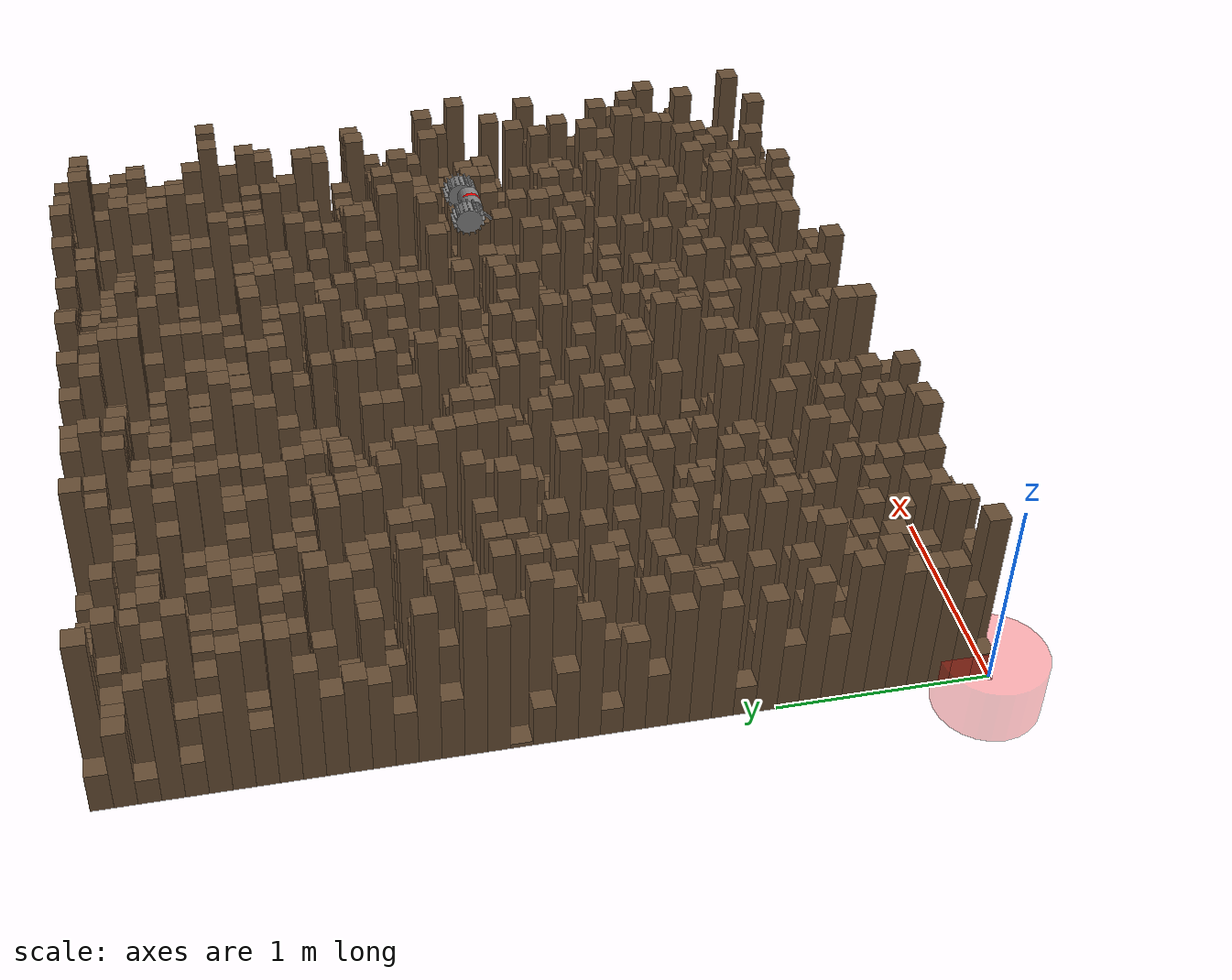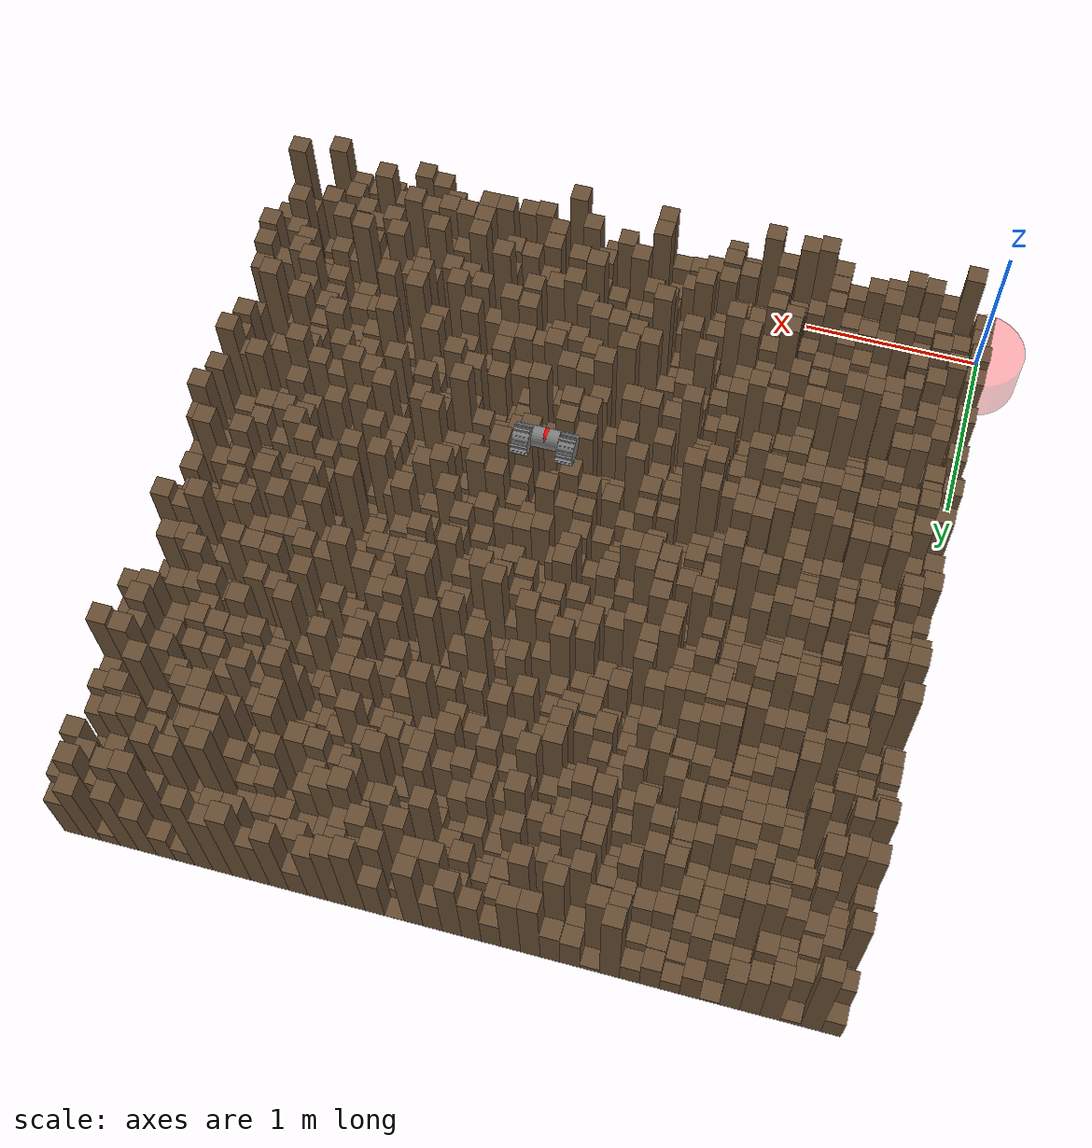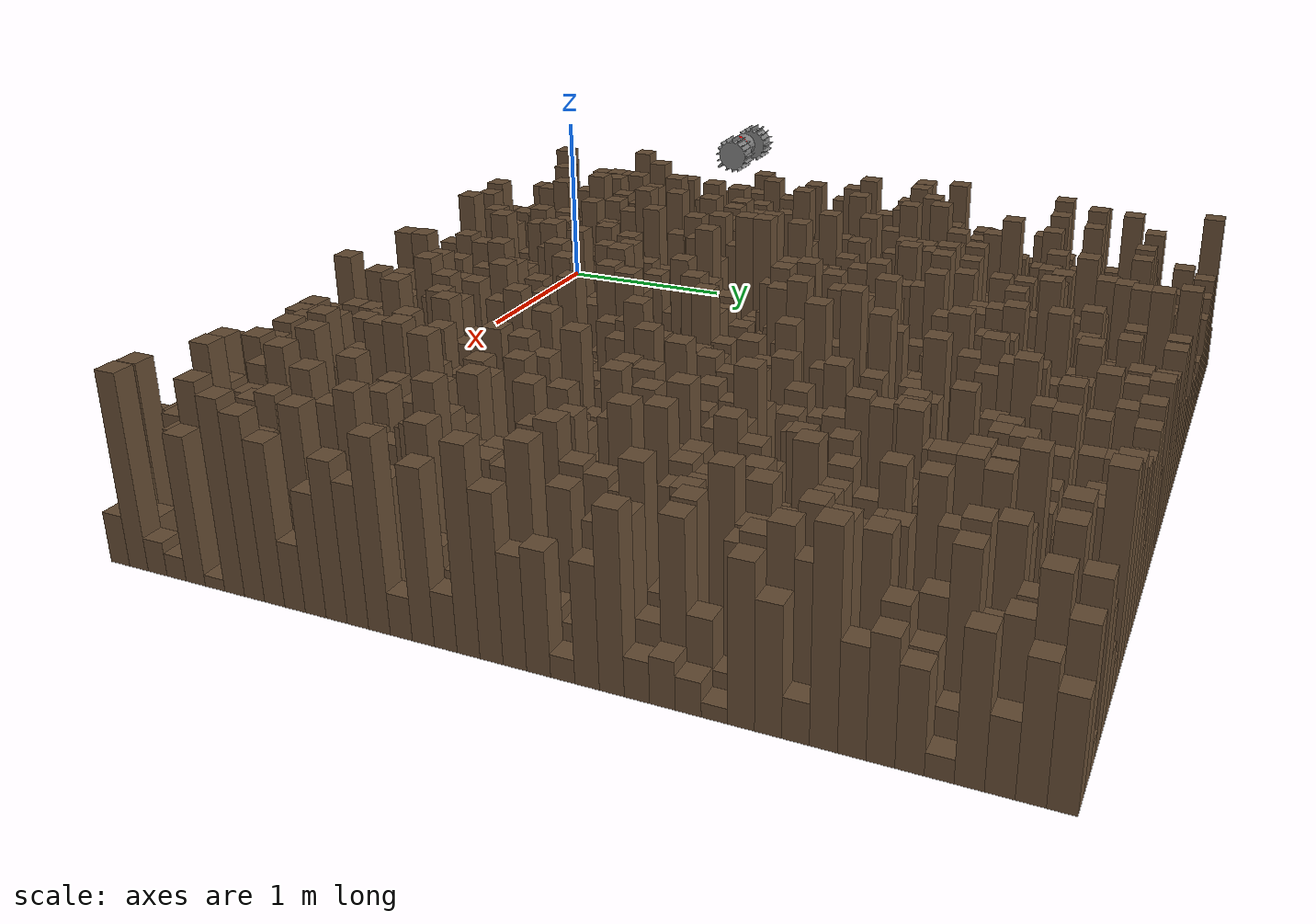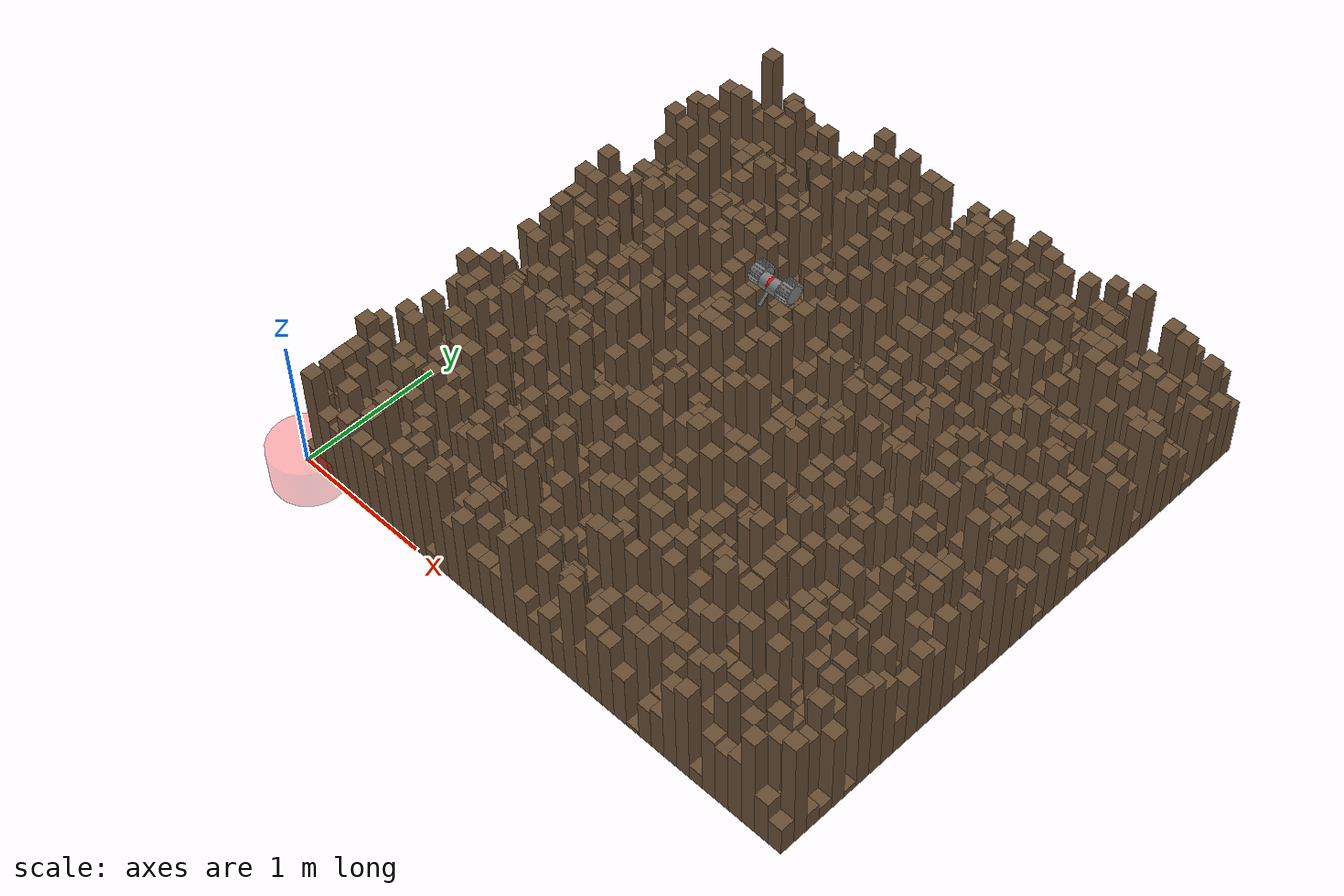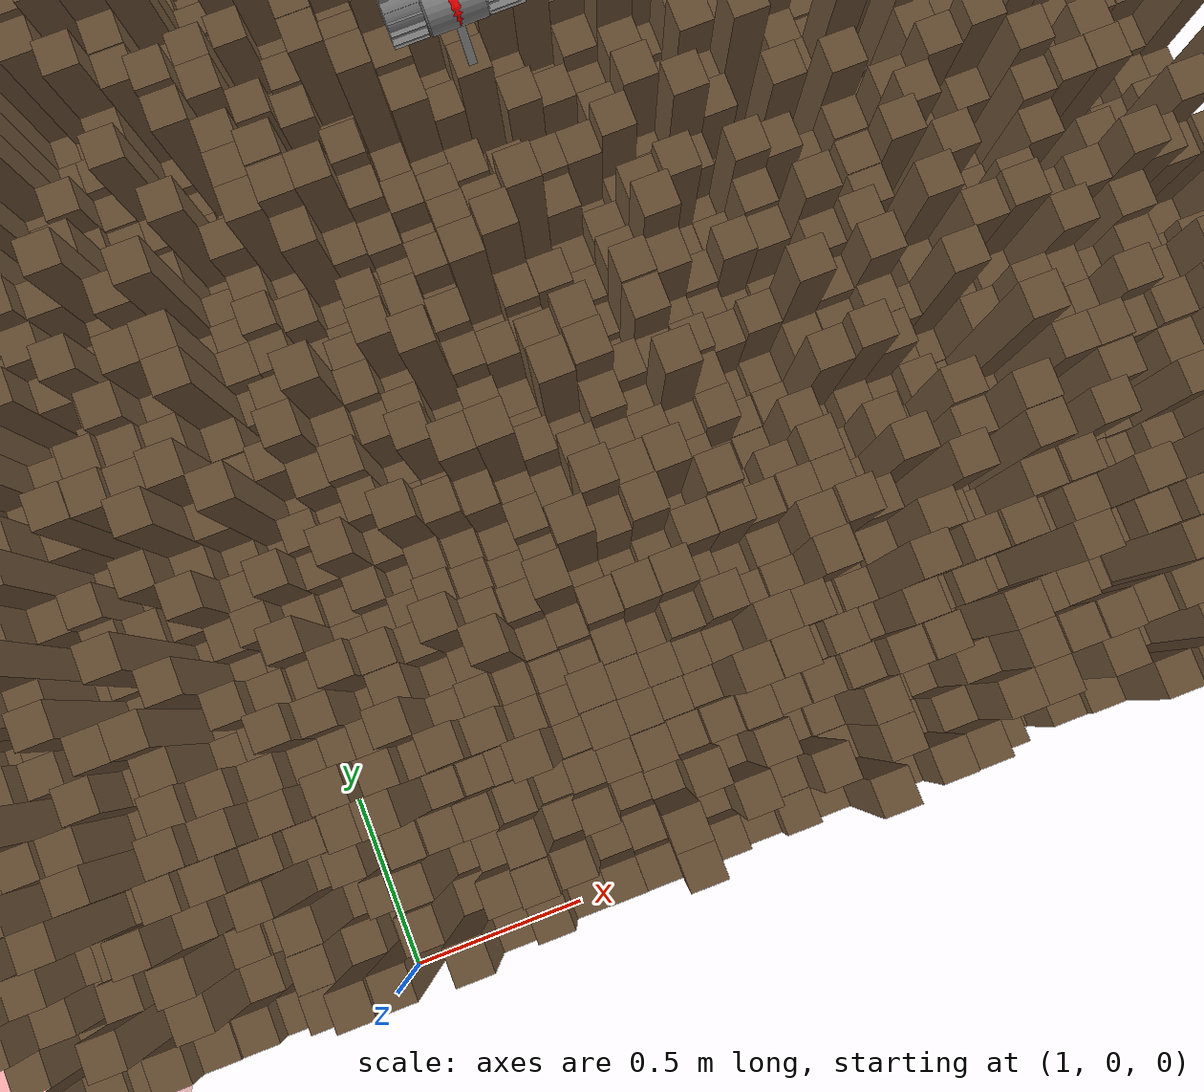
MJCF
<mujoco model="MuJoCo Model">
  <compiler angle="radian"/>

  <visual>
    <global offwidth="1024" offheight="1024"/>
    <quality shadowsize="0" numslices="36"/>
  </visual>

  <default>
    <geom type="box"/>
  </default>

  <asset>
    <texture type="2d" colorspace="auto" name="gray_field" builtin="flat" rgb1="0.5 0.5 0.5" width="100" height="100"/>
    <texture type="skybox" colorspace="auto" name="world_texture" builtin="gradient" rgb1="0 0.5 0.9" rgb2="1 1 1" width="100" height="600"/>
    <material name="field_material" texture="gray_field" reflectance="0.2"/>
    <mesh name="wheel" file="mesh/wheel.stl" inertia="exact" scale="0.001 0.001 0.001"/>
  </asset>

  <worldbody>
    <geom name="floor" size="5 5 0.001" pos="5 5 0" type="plane" group="1" material="field_material" rgba="0 0 0 0"/>
    <camera name="main_cam" pos="2 -0.7 2.2" quat="0.93358 0.358368 0 0"/>
    <light name="main_light" pos="0 0 3" dir="0 0 -1" type="directional" diffuse="1.5 1.5 1.5" specular="0.1 0.1 0.1"/>
    <body name="target_body" gravcomp="1">
      <joint name="slide_x" pos="0 0 0" axis="1 0 0" type="slide"/>
      <joint name="slide_y" pos="0 0 0" axis="0 1 0" type="slide"/>
      <joint name="slide_z" pos="0 0 0" axis="0 0 1" type="slide"/>
      <geom name="target_box" size="0.01 0.01 0.01" contype="0" conaffinity="0"/>
      <site name="target" pos="0 0 0" size="0.25 0.15" type="cylinder" rgba="1 0 0 0.3"/>
    </body>
    <body name="2wheel_rover" pos="2 2 1.5">
      <joint name="body_free_joint" type="free" damping="1"/>
      <geom name="stabilizer" size="0.01 0.07 0.005" pos="0 -0.049497 -0.049497" quat="0.92388 0.382683 0 0" group="2" mass="0.2"/>
      <site name="marker" pos="0 -0.0005 0.001" size="0.05" rgba="1 0 0 1"/>
      <site name="IMU" pos="0 0 0" size="0.01" rgba="1 0 1 1"/>
      <site name="GYRO" pos="0 0 0" size="0.01" rgba="0 1 1 1"/>
      <site name="VELOCITY" pos="0 0 0" size="0.01" rgba="0 1 1 1"/>
      <body name="main_body">
        <geom name="main_body_geom" size="0.05 0.065" quat="0.707107 0 0.707107 0" type="cylinder" group="2" mass="0.5"/>
      </body>
      <body name="r_wheel" pos="0.07 0 0">
        <joint name="r_wheel_joint" pos="0 0 0" axis="-1 0 0" damping="0.3" frictionloss="0.01"/>
        <geom name="r_wheel_geom" pos="0 0.03 0" type="mesh" group="2" friction="1 0.1 0.1" mass="0.25" mesh="wheel"/>
      </body>
      <body name="l_wheel" pos="-0.15 0 0">
        <joint name="l_wheel_joint" pos="0 0 0" axis="-1 0 0" damping="0.3" frictionloss="0.01"/>
        <geom name="l_wheel_geom" pos="0 0.03 0" type="mesh" group="2" friction="1 0.1 0.1" mass="0.25" mesh="wheel"/>
      </body>
    </body>
    <body name="boxy terrain" pos="2 2 0">
      <geom size="0.05 0.05 0.109583" pos="-1.95 1.95 0.109583" group="1" friction="1 0.1 0.1" rgba="0.4 0.3 0.2 1"/>
      <geom size="0.05 0.05 0.225994" pos="-1.95 1.85 0.225994" group="1" friction="1 0.1 0.1" rgba="0.4 0.3 0.2 1"/>
      <geom size="0.05 0.05 0.0728719" pos="-1.95 1.75 0.0728719" group="1" friction="1 0.1 0.1" rgba="0.4 0.3 0.2 1"/>
      <geom size="0.05 0.05 0.36955" pos="-1.95 1.65 0.36955" group="1" friction="1 0.1 0.1" rgba="0.4 0.3 0.2 1"/>
      <geom size="0.05 0.05 0.10413" pos="-1.95 1.55 0.10413" group="1" friction="1 0.1 0.1" rgba="0.4 0.3 0.2 1"/>
      <geom size="0.05 0.05 0.248548" pos="-1.95 1.45 0.248548" group="1" friction="1 0.1 0.1" rgba="0.4 0.3 0.2 1"/>
      <geom size="0.05 0.05 0.416861" pos="-1.95 1.35 0.416861" group="1" friction="1 0.1 0.1" rgba="0.4 0.3 0.2 1"/>
      <geom size="0.05 0.05 0.17882" pos="-1.95 1.25 0.17882" group="1" friction="1 0.1 0.1" rgba="0.4 0.3 0.2 1"/>
      <geom size="0.05 0.05 0.435541" pos="-1.95 1.15 0.435541" group="1" friction="1 0.1 0.1" rgba="0.4 0.3 0.2 1"/>
      <geom size="0.05 0.05 0.329162" pos="-1.95 1.05 0.329162" group="1" friction="1 0.1 0.1" rgba="0.4 0.3 0.2 1"/>
      <geom size="0.05 0.05 0.246652" pos="-1.95 0.95 0.246652" group="1" friction="1 0.1 0.1" rgba="0.4 0.3 0.2 1"/>
      <geom size="0.05 0.05 0.283016" pos="-1.95 0.85 0.283016" group="1" friction="1 0.1 0.1" rgba="0.4 0.3 0.2 1"/>
      <geom size="0.05 0.05 0.263729" pos="-1.95 0.75 0.263729" group="1" friction="1 0.1 0.1" rgba="0.4 0.3 0.2 1"/>
      <geom size="0.05 0.05 0.162099" pos="-1.95 0.65 0.162099" group="1" friction="1 0.1 0.1" rgba="0.4 0.3 0.2 1"/>
      <geom size="0.05 0.05 0.448523" pos="-1.95 0.55 0.448523" group="1" friction="1 0.1 0.1" rgba="0.4 0.3 0.2 1"/>
      <geom size="0.05 0.05 0.181752" pos="-1.95 0.45 0.181752" group="1" friction="1 0.1 0.1" rgba="0.4 0.3 0.2 1"/>
      <geom size="0.05 0.05 0.44273" pos="-1.95 0.35 0.44273" group="1" friction="1 0.1 0.1" rgba="0.4 0.3 0.2 1"/>
      <geom size="0.05 0.05 0.383658" pos="-1.95 0.25 0.383658" group="1" friction="1 0.1 0.1" rgba="0.4 0.3 0.2 1"/>
      <geom size="0.05 0.05 0.0127551" pos="-1.95 0.15 0.0127551" group="1" friction="1 0.1 0.1" rgba="0.4 0.3 0.2 1"/>
      <geom size="0.05 0.05 0.116191" pos="-1.95 0.05 0.116191" group="1" friction="1 0.1 0.1" rgba="0.4 0.3 0.2 1"/>
      <geom size="0.05 0.05 0.214994" pos="-1.95 -0.05 0.214994" group="1" friction="1 0.1 0.1" rgba="0.4 0.3 0.2 1"/>
      <geom size="0.05 0.05 0.366568" pos="-1.95 -0.15 0.366568" group="1" friction="1 0.1 0.1" rgba="0.4 0.3 0.2 1"/>
      <geom size="0.05 0.05 0.0799342" pos="-1.95 -0.25 0.0799342" group="1" friction="1 0.1 0.1" rgba="0.4 0.3 0.2 1"/>
      <geom size="0.05 0.05 0.277128" pos="-1.95 -0.35 0.277128" group="1" friction="1 0.1 0.1" rgba="0.4 0.3 0.2 1"/>
      <geom size="0.05 0.05 0.165244" pos="-1.95 -0.45 0.165244" group="1" friction="1 0.1 0.1" rgba="0.4 0.3 0.2 1"/>
      <geom size="0.05 0.05 0.353556" pos="-1.95 -0.55 0.353556" group="1" friction="1 0.1 0.1" rgba="0.4 0.3 0.2 1"/>
      <geom size="0.05 0.05 0.416891" pos="-1.95 -0.65 0.416891" group="1" friction="1 0.1 0.1" rgba="0.4 0.3 0.2 1"/>
      <geom size="0.05 0.05 0.342953" pos="-1.95 -0.75 0.342953" group="1" friction="1 0.1 0.1" rgba="0.4 0.3 0.2 1"/>
      <geom size="0.05 0.05 0.0869808" pos="-1.95 -0.85 0.0869808" group="1" friction="1 0.1 0.1" rgba="0.4 0.3 0.2 1"/>
      <geom size="0.05 0.05 0.34213" pos="-1.95 -0.95 0.34213" group="1" friction="1 0.1 0.1" rgba="0.4 0.3 0.2 1"/>
      <geom size="0.05 0.05 0.197173" pos="-1.95 -1.05 0.197173" group="1" friction="1 0.1 0.1" rgba="0.4 0.3 0.2 1"/>
      <geom size="0.05 0.05 0.37675" pos="-1.95 -1.15 0.37675" group="1" friction="1 0.1 0.1" rgba="0.4 0.3 0.2 1"/>
      <geom size="0.05 0.05 0.211555" pos="-1.95 -1.25 0.211555" group="1" friction="1 0.1 0.1" rgba="0.4 0.3 0.2 1"/>
      <geom size="0.05 0.05 0.40799" pos="-1.95 -1.35 0.40799" group="1" friction="1 0.1 0.1" rgba="0.4 0.3 0.2 1"/>
      <geom size="0.05 0.05 0.443775" pos="-1.95 -1.45 0.443775" group="1" friction="1 0.1 0.1" rgba="0.4 0.3 0.2 1"/>
      <geom size="0.05 0.05 0.370898" pos="-1.95 -1.55 0.370898" group="1" friction="1 0.1 0.1" rgba="0.4 0.3 0.2 1"/>
      <geom size="0.05 0.05 0.371736" pos="-1.95 -1.65 0.371736" group="1" friction="1 0.1 0.1" rgba="0.4 0.3 0.2 1"/>
      <geom size="0.05 0.05 0.368567" pos="-1.95 -1.75 0.368567" group="1" friction="1 0.1 0.1" rgba="0.4 0.3 0.2 1"/>
      <geom size="0.05 0.05 0.266457" pos="-1.95 -1.85 0.266457" group="1" friction="1 0.1 0.1" rgba="0.4 0.3 0.2 1"/>
      <geom size="0.05 0.05 0.078687" pos="-1.95 -1.95 0.078687" group="1" friction="1 0.1 0.1" rgba="0.4 0.3 0.2 1"/>
      <geom size="0.05 0.05 0.443792" pos="-1.85 1.95 0.443792" group="1" friction="1 0.1 0.1" rgba="0.4 0.3 0.2 1"/>
      <geom size="0.05 0.05 0.208879" pos="-1.85 1.85 0.208879" group="1" friction="1 0.1 0.1" rgba="0.4 0.3 0.2 1"/>
      <geom size="0.05 0.05 0.00728918" pos="-1.85 1.75 0.00728918" group="1" friction="1 0.1 0.1" rgba="0.4 0.3 0.2 1"/>
      <geom size="0.05 0.05 0.195506" pos="-1.85 1.65 0.195506" group="1" friction="1 0.1 0.1" rgba="0.4 0.3 0.2 1"/>
      <geom size="0.05 0.05 0.186739" pos="-1.85 1.55 0.186739" group="1" friction="1 0.1 0.1" rgba="0.4 0.3 0.2 1"/>
      <geom size="0.05 0.05 0.0903911" pos="-1.85 1.45 0.0903911" group="1" friction="1 0.1 0.1" rgba="0.4 0.3 0.2 1"/>
      <geom size="0.05 0.05 0.432163" pos="-1.85 1.35 0.432163" group="1" friction="1 0.1 0.1" rgba="0.4 0.3 0.2 1"/>
      <geom size="0.05 0.05 0.0504111" pos="-1.85 1.25 0.0504111" group="1" friction="1 0.1 0.1" rgba="0.4 0.3 0.2 1"/>
      <geom size="0.05 0.05 0.406865" pos="-1.85 1.15 0.406865" group="1" friction="1 0.1 0.1" rgba="0.4 0.3 0.2 1"/>
      <geom size="0.05 0.05 0.247392" pos="-1.85 1.05 0.247392" group="1" friction="1 0.1 0.1" rgba="0.4 0.3 0.2 1"/>
      <geom size="0.05 0.05 0.0803753" pos="-1.85 0.95 0.0803753" group="1" friction="1 0.1 0.1" rgba="0.4 0.3 0.2 1"/>
      <geom size="0.05 0.05 0.161222" pos="-1.85 0.85 0.161222" group="1" friction="1 0.1 0.1" rgba="0.4 0.3 0.2 1"/>
      <geom size="0.05 0.05 0.202644" pos="-1.85 0.75 0.202644" group="1" friction="1 0.1 0.1" rgba="0.4 0.3 0.2 1"/>
      <geom size="0.05 0.05 0.0529264" pos="-1.85 0.65 0.0529264" group="1" friction="1 0.1 0.1" rgba="0.4 0.3 0.2 1"/>
      <geom size="0.05 0.05 0.343358" pos="-1.85 0.55 0.343358" group="1" friction="1 0.1 0.1" rgba="0.4 0.3 0.2 1"/>
      <geom size="0.05 0.05 0.293218" pos="-1.85 0.45 0.293218" group="1" friction="1 0.1 0.1" rgba="0.4 0.3 0.2 1"/>
      <geom size="0.05 0.05 0.442036" pos="-1.85 0.35 0.442036" group="1" friction="1 0.1 0.1" rgba="0.4 0.3 0.2 1"/>
      <geom size="0.05 0.05 0.373457" pos="-1.85 0.25 0.373457" group="1" friction="1 0.1 0.1" rgba="0.4 0.3 0.2 1"/>
      <geom size="0.05 0.05 0.353686" pos="-1.85 0.15 0.353686" group="1" friction="1 0.1 0.1" rgba="0.4 0.3 0.2 1"/>
      <geom size="0.05 0.05 0.448608" pos="-1.85 0.05 0.448608" group="1" friction="1 0.1 0.1" rgba="0.4 0.3 0.2 1"/>
      <geom size="0.05 0.05 0.419352" pos="-1.85 -0.05 0.419352" group="1" friction="1 0.1 0.1" rgba="0.4 0.3 0.2 1"/>
      <geom size="0.05 0.05 0.289791" pos="-1.85 -0.15 0.289791" group="1" friction="1 0.1 0.1" rgba="0.4 0.3 0.2 1"/>
      <geom size="0.05 0.05 0.242669" pos="-1.85 -0.25 0.242669" group="1" friction="1 0.1 0.1" rgba="0.4 0.3 0.2 1"/>
      <geom size="0.05 0.05 0.23568" pos="-1.85 -0.35 0.23568" group="1" friction="1 0.1 0.1" rgba="0.4 0.3 0.2 1"/>
      <geom size="0.05 0.05 0.366234" pos="-1.85 -0.45 0.366234" group="1" friction="1 0.1 0.1" rgba="0.4 0.3 0.2 1"/>
      <geom size="0.05 0.05 0.416398" pos="-1.85 -0.55 0.416398" group="1" friction="1 0.1 0.1" rgba="0.4 0.3 0.2 1"/>
      <geom size="0.05 0.05 0.373728" pos="-1.85 -0.65 0.373728" group="1" friction="1 0.1 0.1" rgba="0.4 0.3 0.2 1"/>
      <geom size="0.05 0.05 0.377618" pos="-1.85 -0.75 0.377618" group="1" friction="1 0.1 0.1" rgba="0.4 0.3 0.2 1"/>
      <geom size="0.05 0.05 0.0123196" pos="-1.85 -0.85 0.0123196" group="1" friction="1 0.1 0.1" rgba="0.4 0.3 0.2 1"/>
      <geom size="0.05 0.05 0.189283" pos="-1.85 -0.95 0.189283" group="1" friction="1 0.1 0.1" rgba="0.4 0.3 0.2 1"/>
      <geom size="0.05 0.05 0.0392513" pos="-1.85 -1.05 0.0392513" group="1" friction="1 0.1 0.1" rgba="0.4 0.3 0.2 1"/>
      <geom size="0.05 0.05 0.263352" pos="-1.85 -1.15 0.263352" group="1" friction="1 0.1 0.1" rgba="0.4 0.3 0.2 1"/>
      <geom size="0.05 0.05 0.261041" pos="-1.85 -1.25 0.261041" group="1" friction="1 0.1 0.1" rgba="0.4 0.3 0.2 1"/>
      <geom size="0.05 0.05 0.25233" pos="-1.85 -1.35 0.25233" group="1" friction="1 0.1 0.1" rgba="0.4 0.3 0.2 1"/>
      <geom size="0.05 0.05 0.386089" pos="-1.85 -1.45 0.386089" group="1" friction="1 0.1 0.1" rgba="0.4 0.3 0.2 1"/>
      <geom size="0.05 0.05 0.10121" pos="-1.85 -1.55 0.10121" group="1" friction="1 0.1 0.1" rgba="0.4 0.3 0.2 1"/>
      <geom size="0.05 0.05 0.32798" pos="-1.85 -1.65 0.32798" group="1" friction="1 0.1 0.1" rgba="0.4 0.3 0.2 1"/>
      <geom size="0.05 0.05 0.263891" pos="-1.85 -1.75 0.263891" group="1" friction="1 0.1 0.1" rgba="0.4 0.3 0.2 1"/>
      <geom size="0.05 0.05 0.095893" pos="-1.85 -1.85 0.095893" group="1" friction="1 0.1 0.1" rgba="0.4 0.3 0.2 1"/>
      <geom size="0.05 0.05 0.440313" pos="-1.85 -1.95 0.440313" group="1" friction="1 0.1 0.1" rgba="0.4 0.3 0.2 1"/>
      <geom size="0.05 0.05 0.0241026" pos="-1.75 1.95 0.0241026" group="1" friction="1 0.1 0.1" rgba="0.4 0.3 0.2 1"/>
      <geom size="0.05 0.05 0.2092" pos="-1.75 1.85 0.2092" group="1" friction="1 0.1 0.1" rgba="0.4 0.3 0.2 1"/>
      <geom size="0.05 0.05 0.241007" pos="-1.75 1.75 0.241007" group="1" friction="1 0.1 0.1" rgba="0.4 0.3 0.2 1"/>
      <geom size="0.05 0.05 0.267997" pos="-1.75 1.65 0.267997" group="1" friction="1 0.1 0.1" rgba="0.4 0.3 0.2 1"/>
      <geom size="0.05 0.05 0.441915" pos="-1.75 1.55 0.441915" group="1" friction="1 0.1 0.1" rgba="0.4 0.3 0.2 1"/>
      <geom size="0.05 0.05 0.248165" pos="-1.75 1.45 0.248165" group="1" friction="1 0.1 0.1" rgba="0.4 0.3 0.2 1"/>
      <geom size="0.05 0.05 0.398981" pos="-1.75 1.35 0.398981" group="1" friction="1 0.1 0.1" rgba="0.4 0.3 0.2 1"/>
      <geom size="0.05 0.05 0.132512" pos="-1.75 1.25 0.132512" group="1" friction="1 0.1 0.1" rgba="0.4 0.3 0.2 1"/>
      <geom size="0.05 0.05 0.216641" pos="-1.75 1.15 0.216641" group="1" friction="1 0.1 0.1" rgba="0.4 0.3 0.2 1"/>
      <geom size="0.05 0.05 0.0660985" pos="-1.75 1.05 0.0660985" group="1" friction="1 0.1 0.1" rgba="0.4 0.3 0.2 1"/>
      <geom size="0.05 0.05 0.287856" pos="-1.75 0.95 0.287856" group="1" friction="1 0.1 0.1" rgba="0.4 0.3 0.2 1"/>
      <geom size="0.05 0.05 0.19003" pos="-1.75 0.85 0.19003" group="1" friction="1 0.1 0.1" rgba="0.4 0.3 0.2 1"/>
      <geom size="0.05 0.05 0.353184" pos="-1.75 0.75 0.353184" group="1" friction="1 0.1 0.1" rgba="0.4 0.3 0.2 1"/>
      <geom size="0.05 0.05 0.0505983" pos="-1.75 0.65 0.0505983" group="1" friction="1 0.1 0.1" rgba="0.4 0.3 0.2 1"/>
      <geom size="0.05 0.05 0.208938" pos="-1.75 0.55 0.208938" group="1" friction="1 0.1 0.1" rgba="0.4 0.3 0.2 1"/>
      <geom size="0.05 0.05 0.431411" pos="-1.75 0.45 0.431411" group="1" friction="1 0.1 0.1" rgba="0.4 0.3 0.2 1"/>
      <geom size="0.05 0.05 0.00506684" pos="-1.75 0.35 0.00506684" group="1" friction="1 0.1 0.1" rgba="0.4 0.3 0.2 1"/>
      <geom size="0.05 0.05 0.297143" pos="-1.75 0.25 0.297143" group="1" friction="1 0.1 0.1" rgba="0.4 0.3 0.2 1"/>
      <geom size="0.05 0.05 0.30487" pos="-1.75 0.15 0.30487" group="1" friction="1 0.1 0.1" rgba="0.4 0.3 0.2 1"/>
      <geom size="0.05 0.05 0.326642" pos="-1.75 0.05 0.326642" group="1" friction="1 0.1 0.1" rgba="0.4 0.3 0.2 1"/>
      <geom size="0.05 0.05 0.250823" pos="-1.75 -0.05 0.250823" group="1" friction="1 0.1 0.1" rgba="0.4 0.3 0.2 1"/>
      <geom size="0.05 0.05 0.225336" pos="-1.75 -0.15 0.225336" group="1" friction="1 0.1 0.1" rgba="0.4 0.3 0.2 1"/>
      <geom size="0.05 0.05 0.431763" pos="-1.75 -0.25 0.431763" group="1" friction="1 0.1 0.1" rgba="0.4 0.3 0.2 1"/>
      <geom size="0.05 0.05 0.127467" pos="-1.75 -0.35 0.127467" group="1" friction="1 0.1 0.1" rgba="0.4 0.3 0.2 1"/>
      <geom size="0.05 0.05 0.316676" pos="-1.75 -0.45 0.316676" group="1" friction="1 0.1 0.1" rgba="0.4 0.3 0.2 1"/>
      <geom size="0.05 0.05 0.300808" pos="-1.75 -0.55 0.300808" group="1" friction="1 0.1 0.1" rgba="0.4 0.3 0.2 1"/>
      <geom size="0.05 0.05 0.327746" pos="-1.75 -0.65 0.327746" group="1" friction="1 0.1 0.1" rgba="0.4 0.3 0.2 1"/>
      <geom size="0.05 0.05 0.215049" pos="-1.75 -0.75 0.215049" group="1" friction="1 0.1 0.1" rgba="0.4 0.3 0.2 1"/>
      <geom size="0.05 0.05 0.00756318" pos="-1.75 -0.85 0.00756318" group="1" friction="1 0.1 0.1" rgba="0.4 0.3 0.2 1"/>
      <geom size="0.05 0.05 0.34896" pos="-1.75 -0.95 0.34896" group="1" friction="1 0.1 0.1" rgba="0.4 0.3 0.2 1"/>
      <geom size="0.05 0.05 0.125669" pos="-1.75 -1.05 0.125669" group="1" friction="1 0.1 0.1" rgba="0.4 0.3 0.2 1"/>
      <geom size="0.05 0.05 0.35204" pos="-1.75 -1.15 0.35204" group="1" friction="1 0.1 0.1" rgba="0.4 0.3 0.2 1"/>
      <geom size="0.05 0.05 0.444203" pos="-1.75 -1.25 0.444203" group="1" friction="1 0.1 0.1" rgba="0.4 0.3 0.2 1"/>
      <geom size="0.05 0.05 0.349434" pos="-1.75 -1.35 0.349434" group="1" friction="1 0.1 0.1" rgba="0.4 0.3 0.2 1"/>
      <geom size="0.05 0.05 0.181299" pos="-1.75 -1.45 0.181299" group="1" friction="1 0.1 0.1" rgba="0.4 0.3 0.2 1"/>
      <geom size="0.05 0.05 0.385724" pos="-1.75 -1.55 0.385724" group="1" friction="1 0.1 0.1" rgba="0.4 0.3 0.2 1"/>
      <geom size="0.05 0.05 0.173655" pos="-1.75 -1.65 0.173655" group="1" friction="1 0.1 0.1" rgba="0.4 0.3 0.2 1"/>
      <geom size="0.05 0.05 0.143997" pos="-1.75 -1.75 0.143997" group="1" friction="1 0.1 0.1" rgba="0.4 0.3 0.2 1"/>
      <geom size="0.05 0.05 0.256987" pos="-1.75 -1.85 0.256987" group="1" friction="1 0.1 0.1" rgba="0.4 0.3 0.2 1"/>
      <geom size="0.05 0.05 0.294044" pos="-1.75 -1.95 0.294044" group="1" friction="1 0.1 0.1" rgba="0.4 0.3 0.2 1"/>
      <geom size="0.05 0.05 0.308656" pos="-1.65 1.95 0.308656" group="1" friction="1 0.1 0.1" rgba="0.4 0.3 0.2 1"/>
      <geom size="0.05 0.05 0.248682" pos="-1.65 1.85 0.248682" group="1" friction="1 0.1 0.1" rgba="0.4 0.3 0.2 1"/>
      <geom size="0.05 0.05 0.183929" pos="-1.65 1.75 0.183929" group="1" friction="1 0.1 0.1" rgba="0.4 0.3 0.2 1"/>
      <geom size="0.05 0.05 0.334181" pos="-1.65 1.65 0.334181" group="1" friction="1 0.1 0.1" rgba="0.4 0.3 0.2 1"/>
      <geom size="0.05 0.05 0.145996" pos="-1.65 1.55 0.145996" group="1" friction="1 0.1 0.1" rgba="0.4 0.3 0.2 1"/>
      <geom size="0.05 0.05 0.272885" pos="-1.65 1.45 0.272885" group="1" friction="1 0.1 0.1" rgba="0.4 0.3 0.2 1"/>
      <geom size="0.05 0.05 0.00245724" pos="-1.65 1.35 0.00245724" group="1" friction="1 0.1 0.1" rgba="0.4 0.3 0.2 1"/>
      <geom size="0.05 0.05 0.0589155" pos="-1.65 1.25 0.0589155" group="1" friction="1 0.1 0.1" rgba="0.4 0.3 0.2 1"/>
      <geom size="0.05 0.05 0.390357" pos="-1.65 1.15 0.390357" group="1" friction="1 0.1 0.1" rgba="0.4 0.3 0.2 1"/>
      <geom size="0.05 0.05 0.0969811" pos="-1.65 1.05 0.0969811" group="1" friction="1 0.1 0.1" rgba="0.4 0.3 0.2 1"/>
      <geom size="0.05 0.05 0.18572" pos="-1.65 0.95 0.18572" group="1" friction="1 0.1 0.1" rgba="0.4 0.3 0.2 1"/>
      <geom size="0.05 0.05 0.0239907" pos="-1.65 0.85 0.0239907" group="1" friction="1 0.1 0.1" rgba="0.4 0.3 0.2 1"/>
      <geom size="0.05 0.05 0.344284" pos="-1.65 0.75 0.344284" group="1" friction="1 0.1 0.1" rgba="0.4 0.3 0.2 1"/>
      <geom size="0.05 0.05 0.147799" pos="-1.65 0.65 0.147799" group="1" friction="1 0.1 0.1" rgba="0.4 0.3 0.2 1"/>
      <geom size="0.05 0.05 0.0220108" pos="-1.65 0.55 0.0220108" group="1" friction="1 0.1 0.1" rgba="0.4 0.3 0.2 1"/>
      <geom size="0.05 0.05 0.123265" pos="-1.65 0.45 0.123265" group="1" friction="1 0.1 0.1" rgba="0.4 0.3 0.2 1"/>
      <geom size="0.05 0.05 0.418744" pos="-1.65 0.35 0.418744" group="1" friction="1 0.1 0.1" rgba="0.4 0.3 0.2 1"/>
      <geom size="0.05 0.05 0.34003" pos="-1.65 0.25 0.34003" group="1" friction="1 0.1 0.1" rgba="0.4 0.3 0.2 1"/>
      <geom size="0.05 0.05 0.00137631" pos="-1.65 0.15 0.00137631" group="1" friction="1 0.1 0.1" rgba="0.4 0.3 0.2 1"/>
      <geom size="0.05 0.05 0.429117" pos="-1.65 0.05 0.429117" group="1" friction="1 0.1 0.1" rgba="0.4 0.3 0.2 1"/>
      <geom size="0.05 0.05 0.032542" pos="-1.65 -0.05 0.032542" group="1" friction="1 0.1 0.1" rgba="0.4 0.3 0.2 1"/>
      <geom size="0.05 0.05 0.217879" pos="-1.65 -0.15 0.217879" group="1" friction="1 0.1 0.1" rgba="0.4 0.3 0.2 1"/>
      <geom size="0.05 0.05 0.240479" pos="-1.65 -0.25 0.240479" group="1" friction="1 0.1 0.1" rgba="0.4 0.3 0.2 1"/>
      <geom size="0.05 0.05 0.352471" pos="-1.65 -0.35 0.352471" group="1" friction="1 0.1 0.1" rgba="0.4 0.3 0.2 1"/>
      <geom size="0.05 0.05 0.0636486" pos="-1.65 -0.45 0.0636486" group="1" friction="1 0.1 0.1" rgba="0.4 0.3 0.2 1"/>
      <geom size="0.05 0.05 0.371239" pos="-1.65 -0.55 0.371239" group="1" friction="1 0.1 0.1" rgba="0.4 0.3 0.2 1"/>
      <geom size="0.05 0.05 0.123372" pos="-1.65 -0.65 0.123372" group="1" friction="1 0.1 0.1" rgba="0.4 0.3 0.2 1"/>
      <geom size="0.05 0.05 0.33219" pos="-1.65 -0.75 0.33219" group="1" friction="1 0.1 0.1" rgba="0.4 0.3 0.2 1"/>
      <geom size="0.05 0.05 0.4171" pos="-1.65 -0.85 0.4171" group="1" friction="1 0.1 0.1" rgba="0.4 0.3 0.2 1"/>
      <geom size="0.05 0.05 0.265545" pos="-1.65 -0.95 0.265545" group="1" friction="1 0.1 0.1" rgba="0.4 0.3 0.2 1"/>
      <geom size="0.05 0.05 0.000831214" pos="-1.65 -1.05 0.000831214" group="1" friction="1 0.1 0.1" rgba="0.4 0.3 0.2 1"/>
      <geom size="0.05 0.05 0.300189" pos="-1.65 -1.15 0.300189" group="1" friction="1 0.1 0.1" rgba="0.4 0.3 0.2 1"/>
      <geom size="0.05 0.05 0.195871" pos="-1.65 -1.25 0.195871" group="1" friction="1 0.1 0.1" rgba="0.4 0.3 0.2 1"/>
      <geom size="0.05 0.05 0.32871" pos="-1.65 -1.35 0.32871" group="1" friction="1 0.1 0.1" rgba="0.4 0.3 0.2 1"/>
      <geom size="0.05 0.05 0.352984" pos="-1.65 -1.45 0.352984" group="1" friction="1 0.1 0.1" rgba="0.4 0.3 0.2 1"/>
      <geom size="0.05 0.05 0.04832" pos="-1.65 -1.55 0.04832" group="1" friction="1 0.1 0.1" rgba="0.4 0.3 0.2 1"/>
      <geom size="0.05 0.05 0.255519" pos="-1.65 -1.65 0.255519" group="1" friction="1 0.1 0.1" rgba="0.4 0.3 0.2 1"/>
      <geom size="0.05 0.05 0.289562" pos="-1.65 -1.75 0.289562" group="1" friction="1 0.1 0.1" rgba="0.4 0.3 0.2 1"/>
      <geom size="0.05 0.05 0.416949" pos="-1.65 -1.85 0.416949" group="1" friction="1 0.1 0.1" rgba="0.4 0.3 0.2 1"/>
      <geom size="0.05 0.05 0.276208" pos="-1.65 -1.95 0.276208" group="1" friction="1 0.1 0.1" rgba="0.4 0.3 0.2 1"/>
      <geom size="0.05 0.05 0.276697" pos="-1.55 1.95 0.276697" group="1" friction="1 0.1 0.1" rgba="0.4 0.3 0.2 1"/>
      <geom size="0.05 0.05 0.345953" pos="-1.55 1.85 0.345953" group="1" friction="1 0.1 0.1" rgba="0.4 0.3 0.2 1"/>
      <geom size="0.05 0.05 0.0719337" pos="-1.55 1.75 0.0719337" group="1" friction="1 0.1 0.1" rgba="0.4 0.3 0.2 1"/>
      <geom size="0.05 0.05 0.386783" pos="-1.55 1.65 0.386783" group="1" friction="1 0.1 0.1" rgba="0.4 0.3 0.2 1"/>
      <geom size="0.05 0.05 0.261488" pos="-1.55 1.55 0.261488" group="1" friction="1 0.1 0.1" rgba="0.4 0.3 0.2 1"/>
      <geom size="0.05 0.05 0.286263" pos="-1.55 1.45 0.286263" group="1" friction="1 0.1 0.1" rgba="0.4 0.3 0.2 1"/>
      <geom size="0.05 0.05 0.06959" pos="-1.55 1.35 0.06959" group="1" friction="1 0.1 0.1" rgba="0.4 0.3 0.2 1"/>
      <geom size="0.05 0.05 0.235516" pos="-1.55 1.25 0.235516" group="1" friction="1 0.1 0.1" rgba="0.4 0.3 0.2 1"/>
      <geom size="0.05 0.05 0.184215" pos="-1.55 1.15 0.184215" group="1" friction="1 0.1 0.1" rgba="0.4 0.3 0.2 1"/>
      <geom size="0.05 0.05 0.092551" pos="-1.55 1.05 0.092551" group="1" friction="1 0.1 0.1" rgba="0.4 0.3 0.2 1"/>
      <geom size="0.05 0.05 0.423579" pos="-1.55 0.95 0.423579" group="1" friction="1 0.1 0.1" rgba="0.4 0.3 0.2 1"/>
      <geom size="0.05 0.05 0.380795" pos="-1.55 0.85 0.380795" group="1" friction="1 0.1 0.1" rgba="0.4 0.3 0.2 1"/>
      <geom size="0.05 0.05 0.206528" pos="-1.55 0.75 0.206528" group="1" friction="1 0.1 0.1" rgba="0.4 0.3 0.2 1"/>
      <geom size="0.05 0.05 0.0338175" pos="-1.55 0.65 0.0338175" group="1" friction="1 0.1 0.1" rgba="0.4 0.3 0.2 1"/>
      <geom size="0.05 0.05 0.442708" pos="-1.55 0.55 0.442708" group="1" friction="1 0.1 0.1" rgba="0.4 0.3 0.2 1"/>
      <geom size="0.05 0.05 0.0529582" pos="-1.55 0.45 0.0529582" group="1" friction="1 0.1 0.1" rgba="0.4 0.3 0.2 1"/>
      <geom size="0.05 0.05 0.228102" pos="-1.55 0.35 0.228102" group="1" friction="1 0.1 0.1" rgba="0.4 0.3 0.2 1"/>
      <geom size="0.05 0.05 0.254361" pos="-1.55 0.25 0.254361" group="1" friction="1 0.1 0.1" rgba="0.4 0.3 0.2 1"/>
      <geom size="0.05 0.05 0.384959" pos="-1.55 0.15 0.384959" group="1" friction="1 0.1 0.1" rgba="0.4 0.3 0.2 1"/>
      <geom size="0.05 0.05 0.295215" pos="-1.55 0.05 0.295215" group="1" friction="1 0.1 0.1" rgba="0.4 0.3 0.2 1"/>
      <geom size="0.05 0.05 0.27163" pos="-1.55 -0.05 0.27163" group="1" friction="1 0.1 0.1" rgba="0.4 0.3 0.2 1"/>
      <geom size="0.05 0.05 0.230798" pos="-1.55 -0.15 0.230798" group="1" friction="1 0.1 0.1" rgba="0.4 0.3 0.2 1"/>
      <geom size="0.05 0.05 0.440263" pos="-1.55 -0.25 0.440263" group="1" friction="1 0.1 0.1" rgba="0.4 0.3 0.2 1"/>
      <geom size="0.05 0.05 0.368953" pos="-1.55 -0.35 0.368953" group="1" friction="1 0.1 0.1" rgba="0.4 0.3 0.2 1"/>
      <geom size="0.05 0.05 0.160306" pos="-1.55 -0.45 0.160306" group="1" friction="1 0.1 0.1" rgba="0.4 0.3 0.2 1"/>
      <geom size="0.05 0.05 0.357676" pos="-1.55 -0.55 0.357676" group="1" friction="1 0.1 0.1" rgba="0.4 0.3 0.2 1"/>
      <geom size="0.05 0.05 0.426429" pos="-1.55 -0.65 0.426429" group="1" friction="1 0.1 0.1" rgba="0.4 0.3 0.2 1"/>
      <geom size="0.05 0.05 0.218777" pos="-1.55 -0.75 0.218777" group="1" friction="1 0.1 0.1" rgba="0.4 0.3 0.2 1"/>
      <geom size="0.05 0.05 0.0381661" pos="-1.55 -0.85 0.0381661" group="1" friction="1 0.1 0.1" rgba="0.4 0.3 0.2 1"/>
      <geom size="0.05 0.05 0.0301921" pos="-1.55 -0.95 0.0301921" group="1" friction="1 0.1 0.1" rgba="0.4 0.3 0.2 1"/>
      <geom size="0.05 0.05 0.435352" pos="-1.55 -1.05 0.435352" group="1" friction="1 0.1 0.1" rgba="0.4 0.3 0.2 1"/>
      <geom size="0.05 0.05 0.0935444" pos="-1.55 -1.15 0.0935444" group="1" friction="1 0.1 0.1" rgba="0.4 0.3 0.2 1"/>
      <geom size="0.05 0.05 0.361868" pos="-1.55 -1.25 0.361868" group="1" friction="1 0.1 0.1" rgba="0.4 0.3 0.2 1"/>
      <geom size="0.05 0.05 0.086917" pos="-1.55 -1.35 0.086917" group="1" friction="1 0.1 0.1" rgba="0.4 0.3 0.2 1"/>
      <geom size="0.05 0.05 0.100915" pos="-1.55 -1.45 0.100915" group="1" friction="1 0.1 0.1" rgba="0.4 0.3 0.2 1"/>
      <geom size="0.05 0.05 0.0722535" pos="-1.55 -1.55 0.0722535" group="1" friction="1 0.1 0.1" rgba="0.4 0.3 0.2 1"/>
      <geom size="0.05 0.05 0.366928" pos="-1.55 -1.65 0.366928" group="1" friction="1 0.1 0.1" rgba="0.4 0.3 0.2 1"/>
      <geom size="0.05 0.05 0.0412464" pos="-1.55 -1.75 0.0412464" group="1" friction="1 0.1 0.1" rgba="0.4 0.3 0.2 1"/>
      <geom size="0.05 0.05 0.212256" pos="-1.55 -1.85 0.212256" group="1" friction="1 0.1 0.1" rgba="0.4 0.3 0.2 1"/>
      <geom size="0.05 0.05 0.363957" pos="-1.55 -1.95 0.363957" group="1" friction="1 0.1 0.1" rgba="0.4 0.3 0.2 1"/>
      <geom size="0.05 0.05 0.237185" pos="-1.45 1.95 0.237185" group="1" friction="1 0.1 0.1" rgba="0.4 0.3 0.2 1"/>
      <geom size="0.05 0.05 0.00414995" pos="-1.45 1.85 0.00414995" group="1" friction="1 0.1 0.1" rgba="0.4 0.3 0.2 1"/>
      <geom size="0.05 0.05 0.00748136" pos="-1.45 1.75 0.00748136" group="1" friction="1 0.1 0.1" rgba="0.4 0.3 0.2 1"/>
      <geom size="0.05 0.05 0.374064" pos="-1.45 1.65 0.374064" group="1" friction="1 0.1 0.1" rgba="0.4 0.3 0.2 1"/>
      <geom size="0.05 0.05 0.135108" pos="-1.45 1.55 0.135108" group="1" friction="1 0.1 0.1" rgba="0.4 0.3 0.2 1"/>
      <geom size="0.05 0.05 0.0374271" pos="-1.45 1.45 0.0374271" group="1" friction="1 0.1 0.1" rgba="0.4 0.3 0.2 1"/>
      <geom size="0.05 0.05 0.236451" pos="-1.45 1.35 0.236451" group="1" friction="1 0.1 0.1" rgba="0.4 0.3 0.2 1"/>
      <geom size="0.05 0.05 0.352937" pos="-1.45 1.25 0.352937" group="1" friction="1 0.1 0.1" rgba="0.4 0.3 0.2 1"/>
      <geom size="0.05 0.05 0.136385" pos="-1.45 1.15 0.136385" group="1" friction="1 0.1 0.1" rgba="0.4 0.3 0.2 1"/>
      <geom size="0.05 0.05 0.060271" pos="-1.45 1.05 0.060271" group="1" friction="1 0.1 0.1" rgba="0.4 0.3 0.2 1"/>
      <geom size="0.05 0.05 0.0835167" pos="-1.45 0.95 0.0835167" group="1" friction="1 0.1 0.1" rgba="0.4 0.3 0.2 1"/>
      <geom size="0.05 0.05 0.213411" pos="-1.45 0.85 0.213411" group="1" friction="1 0.1 0.1" rgba="0.4 0.3 0.2 1"/>
      <geom size="0.05 0.05 0.350915" pos="-1.45 0.75 0.350915" group="1" friction="1 0.1 0.1" rgba="0.4 0.3 0.2 1"/>
      <geom size="0.05 0.05 0.0373194" pos="-1.45 0.65 0.0373194" group="1" friction="1 0.1 0.1" rgba="0.4 0.3 0.2 1"/>
      <geom size="0.05 0.05 0.342443" pos="-1.45 0.55 0.342443" group="1" friction="1 0.1 0.1" rgba="0.4 0.3 0.2 1"/>
      <geom size="0.05 0.05 0.306818" pos="-1.45 0.45 0.306818" group="1" friction="1 0.1 0.1" rgba="0.4 0.3 0.2 1"/>
      <geom size="0.05 0.05 0.251022" pos="-1.45 0.35 0.251022" group="1" friction="1 0.1 0.1" rgba="0.4 0.3 0.2 1"/>
      <geom size="0.05 0.05 0.172292" pos="-1.45 0.25 0.172292" group="1" friction="1 0.1 0.1" rgba="0.4 0.3 0.2 1"/>
      <geom size="0.05 0.05 0.0143321" pos="-1.45 0.15 0.0143321" group="1" friction="1 0.1 0.1" rgba="0.4 0.3 0.2 1"/>
      <geom size="0.05 0.05 0.226768" pos="-1.45 0.05 0.226768" group="1" friction="1 0.1 0.1" rgba="0.4 0.3 0.2 1"/>
      <geom size="0.05 0.05 0.185211" pos="-1.45 -0.05 0.185211" group="1" friction="1 0.1 0.1" rgba="0.4 0.3 0.2 1"/>
      <geom size="0.05 0.05 0.305596" pos="-1.45 -0.15 0.305596" group="1" friction="1 0.1 0.1" rgba="0.4 0.3 0.2 1"/>
      <geom size="0.05 0.05 0.0280477" pos="-1.45 -0.25 0.0280477" group="1" friction="1 0.1 0.1" rgba="0.4 0.3 0.2 1"/>
      <geom size="0.05 0.05 0.0745303" pos="-1.45 -0.35 0.0745303" group="1" friction="1 0.1 0.1" rgba="0.4 0.3 0.2 1"/>
      <geom size="0.05 0.05 0.0084127" pos="-1.45 -0.45 0.0084127" group="1" friction="1 0.1 0.1" rgba="0.4 0.3 0.2 1"/>
      <geom size="0.05 0.05 0.219007" pos="-1.45 -0.55 0.219007" group="1" friction="1 0.1 0.1" rgba="0.4 0.3 0.2 1"/>
      <geom size="0.05 0.05 0.0267155" pos="-1.45 -0.65 0.0267155" group="1" friction="1 0.1 0.1" rgba="0.4 0.3 0.2 1"/>
      <geom size="0.05 0.05 0.239999" pos="-1.45 -0.75 0.239999" group="1" friction="1 0.1 0.1" rgba="0.4 0.3 0.2 1"/>
      <geom size="0.05 0.05 0.196627" pos="-1.45 -0.85 0.196627" group="1" friction="1 0.1 0.1" rgba="0.4 0.3 0.2 1"/>
      <geom size="0.05 0.05 0.148844" pos="-1.45 -0.95 0.148844" group="1" friction="1 0.1 0.1" rgba="0.4 0.3 0.2 1"/>
      <geom size="0.05 0.05 0.085554" pos="-1.45 -1.05 0.085554" group="1" friction="1 0.1 0.1" rgba="0.4 0.3 0.2 1"/>
      <geom size="0.05 0.05 0.414346" pos="-1.45 -1.15 0.414346" group="1" friction="1 0.1 0.1" rgba="0.4 0.3 0.2 1"/>
      <geom size="0.05 0.05 0.21624" pos="-1.45 -1.25 0.21624" group="1" friction="1 0.1 0.1" rgba="0.4 0.3 0.2 1"/>
      <geom size="0.05 0.05 0.0459745" pos="-1.45 -1.35 0.0459745" group="1" friction="1 0.1 0.1" rgba="0.4 0.3 0.2 1"/>
      <geom size="0.05 0.05 0.260011" pos="-1.45 -1.45 0.260011" group="1" friction="1 0.1 0.1" rgba="0.4 0.3 0.2 1"/>
      <geom size="0.05 0.05 0.34341" pos="-1.45 -1.55 0.34341" group="1" friction="1 0.1 0.1" rgba="0.4 0.3 0.2 1"/>
      <geom size="0.05 0.05 0.219679" pos="-1.45 -1.65 0.219679" group="1" friction="1 0.1 0.1" rgba="0.4 0.3 0.2 1"/>
      <geom size="0.05 0.05 0.401051" pos="-1.45 -1.75 0.401051" group="1" friction="1 0.1 0.1" rgba="0.4 0.3 0.2 1"/>
      <geom size="0.05 0.05 0.377335" pos="-1.45 -1.85 0.377335" group="1" friction="1 0.1 0.1" rgba="0.4 0.3 0.2 1"/>
      <geom size="0.05 0.05 0.30625" pos="-1.45 -1.95 0.30625" group="1" friction="1 0.1 0.1" rgba="0.4 0.3 0.2 1"/>
      <geom size="0.05 0.05 0.0117863" pos="-1.35 1.95 0.0117863" group="1" friction="1 0.1 0.1" rgba="0.4 0.3 0.2 1"/>
      <geom size="0.05 0.05 0.18102" pos="-1.35 1.85 0.18102" group="1" friction="1 0.1 0.1" rgba="0.4 0.3 0.2 1"/>
      <geom size="0.05 0.05 0.229802" pos="-1.35 1.75 0.229802" group="1" friction="1 0.1 0.1" rgba="0.4 0.3 0.2 1"/>
      <geom size="0.05 0.05 0.0761798" pos="-1.35 1.65 0.0761798" group="1" friction="1 0.1 0.1" rgba="0.4 0.3 0.2 1"/>
      <geom size="0.05 0.05 0.224965" pos="-1.35 1.55 0.224965" group="1" friction="1 0.1 0.1" rgba="0.4 0.3 0.2 1"/>
      <geom size="0.05 0.05 0.300628" pos="-1.35 1.45 0.300628" group="1" friction="1 0.1 0.1" rgba="0.4 0.3 0.2 1"/>
      <geom size="0.05 0.05 0.338615" pos="-1.35 1.35 0.338615" group="1" friction="1 0.1 0.1" rgba="0.4 0.3 0.2 1"/>
      <geom size="0.05 0.05 0.341804" pos="-1.35 1.25 0.341804" group="1" friction="1 0.1 0.1" rgba="0.4 0.3 0.2 1"/>
      <geom size="0.05 0.05 0.33637" pos="-1.35 1.15 0.33637" group="1" friction="1 0.1 0.1" rgba="0.4 0.3 0.2 1"/>
      <geom size="0.05 0.05 0.134975" pos="-1.35 1.05 0.134975" group="1" friction="1 0.1 0.1" rgba="0.4 0.3 0.2 1"/>
      <geom size="0.05 0.05 0.275394" pos="-1.35 0.95 0.275394" group="1" friction="1 0.1 0.1" rgba="0.4 0.3 0.2 1"/>
      <geom size="0.05 0.05 0.225437" pos="-1.35 0.85 0.225437" group="1" friction="1 0.1 0.1" rgba="0.4 0.3 0.2 1"/>
      <geom size="0.05 0.05 0.341285" pos="-1.35 0.75 0.341285" group="1" friction="1 0.1 0.1" rgba="0.4 0.3 0.2 1"/>
      <geom size="0.05 0.05 0.0547906" pos="-1.35 0.65 0.0547906" group="1" friction="1 0.1 0.1" rgba="0.4 0.3 0.2 1"/>
      <geom size="0.05 0.05 0.0791995" pos="-1.35 0.55 0.0791995" group="1" friction="1 0.1 0.1" rgba="0.4 0.3 0.2 1"/>
      <geom size="0.05 0.05 0.322611" pos="-1.35 0.45 0.322611" group="1" friction="1 0.1 0.1" rgba="0.4 0.3 0.2 1"/>
      <geom size="0.05 0.05 0.325793" pos="-1.35 0.35 0.325793" group="1" friction="1 0.1 0.1" rgba="0.4 0.3 0.2 1"/>
      <geom size="0.05 0.05 0.103265" pos="-1.35 0.25 0.103265" group="1" friction="1 0.1 0.1" rgba="0.4 0.3 0.2 1"/>
      <geom size="0.05 0.05 0.345725" pos="-1.35 0.15 0.345725" group="1" friction="1 0.1 0.1" rgba="0.4 0.3 0.2 1"/>
      <geom size="0.05 0.05 0.3493" pos="-1.35 0.05 0.3493" group="1" friction="1 0.1 0.1" rgba="0.4 0.3 0.2 1"/>
      <geom size="0.05 0.05 0.290983" pos="-1.35 -0.05 0.290983" group="1" friction="1 0.1 0.1" rgba="0.4 0.3 0.2 1"/>
      <geom size="0.05 0.05 0.207673" pos="-1.35 -0.15 0.207673" group="1" friction="1 0.1 0.1" rgba="0.4 0.3 0.2 1"/>
      <geom size="0.05 0.05 0.0257452" pos="-1.35 -0.25 0.0257452" group="1" friction="1 0.1 0.1" rgba="0.4 0.3 0.2 1"/>
      <geom size="0.05 0.05 0.103617" pos="-1.35 -0.35 0.103617" group="1" friction="1 0.1 0.1" rgba="0.4 0.3 0.2 1"/>
      <geom size="0.05 0.05 0.344507" pos="-1.35 -0.45 0.344507" group="1" friction="1 0.1 0.1" rgba="0.4 0.3 0.2 1"/>
      <geom size="0.05 0.05 0.419321" pos="-1.35 -0.55 0.419321" group="1" friction="1 0.1 0.1" rgba="0.4 0.3 0.2 1"/>
      <geom size="0.05 0.05 0.0741204" pos="-1.35 -0.65 0.0741204" group="1" friction="1 0.1 0.1" rgba="0.4 0.3 0.2 1"/>
      <geom size="0.05 0.05 0.0165441" pos="-1.35 -0.75 0.0165441" group="1" friction="1 0.1 0.1" rgba="0.4 0.3 0.2 1"/>
      <geom size="0.05 0.05 0.157157" pos="-1.35 -0.85 0.157157" group="1" friction="1 0.1 0.1" rgba="0.4 0.3 0.2 1"/>
      <geom size="0.05 0.05 0.42316" pos="-1.35 -0.95 0.42316" group="1" friction="1 0.1 0.1" rgba="0.4 0.3 0.2 1"/>
      <geom size="0.05 0.05 0.0973596" pos="-1.35 -1.05 0.0973596" group="1" friction="1 0.1 0.1" rgba="0.4 0.3 0.2 1"/>
      <geom size="0.05 0.05 0.420274" pos="-1.35 -1.15 0.420274" group="1" friction="1 0.1 0.1" rgba="0.4 0.3 0.2 1"/>
      <geom size="0.05 0.05 0.352829" pos="-1.35 -1.25 0.352829" group="1" friction="1 0.1 0.1" rgba="0.4 0.3 0.2 1"/>
      <geom size="0.05 0.05 0.37809" pos="-1.35 -1.35 0.37809" group="1" friction="1 0.1 0.1" rgba="0.4 0.3 0.2 1"/>
      <geom size="0.05 0.05 0.445901" pos="-1.35 -1.45 0.445901" group="1" friction="1 0.1 0.1" rgba="0.4 0.3 0.2 1"/>
      <geom size="0.05 0.05 0.304105" pos="-1.35 -1.55 0.304105" group="1" friction="1 0.1 0.1" rgba="0.4 0.3 0.2 1"/>
      <geom size="0.05 0.05 0.0889778" pos="-1.35 -1.65 0.0889778" group="1" friction="1 0.1 0.1" rgba="0.4 0.3 0.2 1"/>
      <geom size="0.05 0.05 0.195081" pos="-1.35 -1.75 0.195081" group="1" friction="1 0.1 0.1" rgba="0.4 0.3 0.2 1"/>
      <geom size="0.05 0.05 0.178677" pos="-1.35 -1.85 0.178677" group="1" friction="1 0.1 0.1" rgba="0.4 0.3 0.2 1"/>
      <geom size="0.05 0.05 0.299184" pos="-1.35 -1.95 0.299184" group="1" friction="1 0.1 0.1" rgba="0.4 0.3 0.2 1"/>
      <geom size="0.05 0.05 0.159022" pos="-1.25 1.95 0.159022" group="1" friction="1 0.1 0.1" rgba="0.4 0.3 0.2 1"/>
      <geom size="0.05 0.05 0.329121" pos="-1.25 1.85 0.329121" group="1" friction="1 0.1 0.1" rgba="0.4 0.3 0.2 1"/>
      <geom size="0.05 0.05 0.013476" pos="-1.25 1.75 0.013476" group="1" friction="1 0.1 0.1" rgba="0.4 0.3 0.2 1"/>
      <geom size="0.05 0.05 0.100151" pos="-1.25 1.65 0.100151" group="1" friction="1 0.1 0.1" rgba="0.4 0.3 0.2 1"/>
      <geom size="0.05 0.05 0.0998969" pos="-1.25 1.55 0.0998969" group="1" friction="1 0.1 0.1" rgba="0.4 0.3 0.2 1"/>
      <geom size="0.05 0.05 0.07682" pos="-1.25 1.45 0.07682" group="1" friction="1 0.1 0.1" rgba="0.4 0.3 0.2 1"/>
      <geom size="0.05 0.05 0.337224" pos="-1.25 1.35 0.337224" group="1" friction="1 0.1 0.1" rgba="0.4 0.3 0.2 1"/>
      <geom size="0.05 0.05 0.394189" pos="-1.25 1.25 0.394189" group="1" friction="1 0.1 0.1" rgba="0.4 0.3 0.2 1"/>
      <geom size="0.05 0.05 0.0425779" pos="-1.25 1.15 0.0425779" group="1" friction="1 0.1 0.1" rgba="0.4 0.3 0.2 1"/>
      <geom size="0.05 0.05 0.214588" pos="-1.25 1.05 0.214588" group="1" friction="1 0.1 0.1" rgba="0.4 0.3 0.2 1"/>
      <geom size="0.05 0.05 0.0037297" pos="-1.25 0.95 0.0037297" group="1" friction="1 0.1 0.1" rgba="0.4 0.3 0.2 1"/>
      <geom size="0.05 0.05 0.111431" pos="-1.25 0.85 0.111431" group="1" friction="1 0.1 0.1" rgba="0.4 0.3 0.2 1"/>
      <geom size="0.05 0.05 0.0650613" pos="-1.25 0.75 0.0650613" group="1" friction="1 0.1 0.1" rgba="0.4 0.3 0.2 1"/>
      <geom size="0.05 0.05 0.311571" pos="-1.25 0.65 0.311571" group="1" friction="1 0.1 0.1" rgba="0.4 0.3 0.2 1"/>
      <geom size="0.05 0.05 0.37622" pos="-1.25 0.55 0.37622" group="1" friction="1 0.1 0.1" rgba="0.4 0.3 0.2 1"/>
      <geom size="0.05 0.05 0.379162" pos="-1.25 0.45 0.379162" group="1" friction="1 0.1 0.1" rgba="0.4 0.3 0.2 1"/>
      <geom size="0.05 0.05 0.123646" pos="-1.25 0.35 0.123646" group="1" friction="1 0.1 0.1" rgba="0.4 0.3 0.2 1"/>
      <geom size="0.05 0.05 0.184355" pos="-1.25 0.25 0.184355" group="1" friction="1 0.1 0.1" rgba="0.4 0.3 0.2 1"/>
      <geom size="0.05 0.05 0.103889" pos="-1.25 0.15 0.103889" group="1" friction="1 0.1 0.1" rgba="0.4 0.3 0.2 1"/>
      <geom size="0.05 0.05 0.298602" pos="-1.25 0.05 0.298602" group="1" friction="1 0.1 0.1" rgba="0.4 0.3 0.2 1"/>
      <geom size="0.05 0.05 0.102987" pos="-1.25 -0.05 0.102987" group="1" friction="1 0.1 0.1" rgba="0.4 0.3 0.2 1"/>
      <geom size="0.05 0.05 0.344906" pos="-1.25 -0.15 0.344906" group="1" friction="1 0.1 0.1" rgba="0.4 0.3 0.2 1"/>
      <geom size="0.05 0.05 0.211672" pos="-1.25 -0.25 0.211672" group="1" friction="1 0.1 0.1" rgba="0.4 0.3 0.2 1"/>
      <geom size="0.05 0.05 0.247739" pos="-1.25 -0.35 0.247739" group="1" friction="1 0.1 0.1" rgba="0.4 0.3 0.2 1"/>
      <geom size="0.05 0.05 0.392346" pos="-1.25 -0.45 0.392346" group="1" friction="1 0.1 0.1" rgba="0.4 0.3 0.2 1"/>
      <geom size="0.05 0.05 0.415864" pos="-1.25 -0.55 0.415864" group="1" friction="1 0.1 0.1" rgba="0.4 0.3 0.2 1"/>
      <geom size="0.05 0.05 0.120583" pos="-1.25 -0.65 0.120583" group="1" friction="1 0.1 0.1" rgba="0.4 0.3 0.2 1"/>
      <geom size="0.05 0.05 0.326931" pos="-1.25 -0.75 0.326931" group="1" friction="1 0.1 0.1" rgba="0.4 0.3 0.2 1"/>
      <geom size="0.05 0.05 0.122805" pos="-1.25 -0.85 0.122805" group="1" friction="1 0.1 0.1" rgba="0.4 0.3 0.2 1"/>
      <geom size="0.05 0.05 0.0048656" pos="-1.25 -0.95 0.0048656" group="1" friction="1 0.1 0.1" rgba="0.4 0.3 0.2 1"/>
      <geom size="0.05 0.05 0.382863" pos="-1.25 -1.05 0.382863" group="1" friction="1 0.1 0.1" rgba="0.4 0.3 0.2 1"/>
      <geom size="0.05 0.05 0.085814" pos="-1.25 -1.15 0.085814" group="1" friction="1 0.1 0.1" rgba="0.4 0.3 0.2 1"/>
      <geom size="0.05 0.05 0.1266" pos="-1.25 -1.25 0.1266" group="1" friction="1 0.1 0.1" rgba="0.4 0.3 0.2 1"/>
      <geom size="0.05 0.05 0.323149" pos="-1.25 -1.35 0.323149" group="1" friction="1 0.1 0.1" rgba="0.4 0.3 0.2 1"/>
      <geom size="0.05 0.05 0.38264" pos="-1.25 -1.45 0.38264" group="1" friction="1 0.1 0.1" rgba="0.4 0.3 0.2 1"/>
      <geom size="0.05 0.05 0.174865" pos="-1.25 -1.55 0.174865" group="1" friction="1 0.1 0.1" rgba="0.4 0.3 0.2 1"/>
      <geom size="0.05 0.05 0.322184" pos="-1.25 -1.65 0.322184" group="1" friction="1 0.1 0.1" rgba="0.4 0.3 0.2 1"/>
      <geom size="0.05 0.05 0.178292" pos="-1.25 -1.75 0.178292" group="1" friction="1 0.1 0.1" rgba="0.4 0.3 0.2 1"/>
      <geom size="0.05 0.05 0.00809087" pos="-1.25 -1.85 0.00809087" group="1" friction="1 0.1 0.1" rgba="0.4 0.3 0.2 1"/>
      <geom size="0.05 0.05 0.248983" pos="-1.25 -1.95 0.248983" group="1" friction="1 0.1 0.1" rgba="0.4 0.3 0.2 1"/>
      <geom size="0.05 0.05 0.077699" pos="-1.15 1.95 0.077699" group="1" friction="1 0.1 0.1" rgba="0.4 0.3 0.2 1"/>
      <geom size="0.05 0.05 0.0943812" pos="-1.15 1.85 0.0943812" group="1" friction="1 0.1 0.1" rgba="0.4 0.3 0.2 1"/>
      <geom size="0.05 0.05 0.183581" pos="-1.15 1.75 0.183581" group="1" friction="1 0.1 0.1" rgba="0.4 0.3 0.2 1"/>
      <geom size="0.05 0.05 0.289833" pos="-1.15 1.65 0.289833" group="1" friction="1 0.1 0.1" rgba="0.4 0.3 0.2 1"/>
      <geom size="0.05 0.05 0.0989461" pos="-1.15 1.55 0.0989461" group="1" friction="1 0.1 0.1" rgba="0.4 0.3 0.2 1"/>
      <geom size="0.05 0.05 0.0985345" pos="-1.15 1.45 0.0985345" group="1" friction="1 0.1 0.1" rgba="0.4 0.3 0.2 1"/>
      <geom size="0.05 0.05 0.256704" pos="-1.15 1.35 0.256704" group="1" friction="1 0.1 0.1" rgba="0.4 0.3 0.2 1"/>
      <geom size="0.05 0.05 0.123182" pos="-1.15 1.25 0.123182" group="1" friction="1 0.1 0.1" rgba="0.4 0.3 0.2 1"/>
      <geom size="0.05 0.05 0.252306" pos="-1.15 1.15 0.252306" group="1" friction="1 0.1 0.1" rgba="0.4 0.3 0.2 1"/>
      <geom size="0.05 0.05 0.303246" pos="-1.15 1.05 0.303246" group="1" friction="1 0.1 0.1" rgba="0.4 0.3 0.2 1"/>
      <geom size="0.05 0.05 0.138127" pos="-1.15 0.95 0.138127" group="1" friction="1 0.1 0.1" rgba="0.4 0.3 0.2 1"/>
      <geom size="0.05 0.05 0.404146" pos="-1.15 0.85 0.404146" group="1" friction="1 0.1 0.1" rgba="0.4 0.3 0.2 1"/>
      <geom size="0.05 0.05 0.435248" pos="-1.15 0.75 0.435248" group="1" friction="1 0.1 0.1" rgba="0.4 0.3 0.2 1"/>
      <geom size="0.05 0.05 0.017668" pos="-1.15 0.65 0.017668" group="1" friction="1 0.1 0.1" rgba="0.4 0.3 0.2 1"/>
      <geom size="0.05 0.05 0.029454" pos="-1.15 0.55 0.029454" group="1" friction="1 0.1 0.1" rgba="0.4 0.3 0.2 1"/>
      <geom size="0.05 0.05 0.0491557" pos="-1.15 0.45 0.0491557" group="1" friction="1 0.1 0.1" rgba="0.4 0.3 0.2 1"/>
      <geom size="0.05 0.05 0.221128" pos="-1.15 0.35 0.221128" group="1" friction="1 0.1 0.1" rgba="0.4 0.3 0.2 1"/>
      <geom size="0.05 0.05 0.135429" pos="-1.15 0.25 0.135429" group="1" friction="1 0.1 0.1" rgba="0.4 0.3 0.2 1"/>
      <geom size="0.05 0.05 0.32936" pos="-1.15 0.15 0.32936" group="1" friction="1 0.1 0.1" rgba="0.4 0.3 0.2 1"/>
      <geom size="0.05 0.05 0.443393" pos="-1.15 0.05 0.443393" group="1" friction="1 0.1 0.1" rgba="0.4 0.3 0.2 1"/>
      <geom size="0.05 0.05 0.204018" pos="-1.15 -0.05 0.204018" group="1" friction="1 0.1 0.1" rgba="0.4 0.3 0.2 1"/>
      <geom size="0.05 0.05 0.123272" pos="-1.15 -0.15 0.123272" group="1" friction="1 0.1 0.1" rgba="0.4 0.3 0.2 1"/>
      <geom size="0.05 0.05 0.0993159" pos="-1.15 -0.25 0.0993159" group="1" friction="1 0.1 0.1" rgba="0.4 0.3 0.2 1"/>
      <geom size="0.05 0.05 0.410056" pos="-1.15 -0.35 0.410056" group="1" friction="1 0.1 0.1" rgba="0.4 0.3 0.2 1"/>
      <geom size="0.05 0.05 0.366692" pos="-1.15 -0.45 0.366692" group="1" friction="1 0.1 0.1" rgba="0.4 0.3 0.2 1"/>
      <geom size="0.05 0.05 0.395523" pos="-1.15 -0.55 0.395523" group="1" friction="1 0.1 0.1" rgba="0.4 0.3 0.2 1"/>
      <geom size="0.05 0.05 0.44986" pos="-1.15 -0.65 0.44986" group="1" friction="1 0.1 0.1" rgba="0.4 0.3 0.2 1"/>
      <geom size="0.05 0.05 0.203794" pos="-1.15 -0.75 0.203794" group="1" friction="1 0.1 0.1" rgba="0.4 0.3 0.2 1"/>
      <geom size="0.05 0.05 0.33623" pos="-1.15 -0.85 0.33623" group="1" friction="1 0.1 0.1" rgba="0.4 0.3 0.2 1"/>
      <geom size="0.05 0.05 0.151344" pos="-1.15 -0.95 0.151344" group="1" friction="1 0.1 0.1" rgba="0.4 0.3 0.2 1"/>
      <geom size="0.05 0.05 0.0632823" pos="-1.15 -1.05 0.0632823" group="1" friction="1 0.1 0.1" rgba="0.4 0.3 0.2 1"/>
      <geom size="0.05 0.05 0.311813" pos="-1.15 -1.15 0.311813" group="1" friction="1 0.1 0.1" rgba="0.4 0.3 0.2 1"/>
      <geom size="0.05 0.05 0.166845" pos="-1.15 -1.25 0.166845" group="1" friction="1 0.1 0.1" rgba="0.4 0.3 0.2 1"/>
      <geom size="0.05 0.05 0.242849" pos="-1.15 -1.35 0.242849" group="1" friction="1 0.1 0.1" rgba="0.4 0.3 0.2 1"/>
      <geom size="0.05 0.05 0.255412" pos="-1.15 -1.45 0.255412" group="1" friction="1 0.1 0.1" rgba="0.4 0.3 0.2 1"/>
      <geom size="0.05 0.05 0.10913" pos="-1.15 -1.55 0.10913" group="1" friction="1 0.1 0.1" rgba="0.4 0.3 0.2 1"/>
      <geom size="0.05 0.05 0.00987236" pos="-1.15 -1.65 0.00987236" group="1" friction="1 0.1 0.1" rgba="0.4 0.3 0.2 1"/>
      <geom size="0.05 0.05 0.334867" pos="-1.15 -1.75 0.334867" group="1" friction="1 0.1 0.1" rgba="0.4 0.3 0.2 1"/>
      <geom size="0.05 0.05 0.34247" pos="-1.15 -1.85 0.34247" group="1" friction="1 0.1 0.1" rgba="0.4 0.3 0.2 1"/>
      <geom size="0.05 0.05 0.344154" pos="-1.15 -1.95 0.344154" group="1" friction="1 0.1 0.1" rgba="0.4 0.3 0.2 1"/>
      <geom size="0.05 0.05 0.147236" pos="-1.05 1.95 0.147236" group="1" friction="1 0.1 0.1" rgba="0.4 0.3 0.2 1"/>
      <geom size="0.05 0.05 0.150625" pos="-1.05 1.85 0.150625" group="1" friction="1 0.1 0.1" rgba="0.4 0.3 0.2 1"/>
      <geom size="0.05 0.05 0.28218" pos="-1.05 1.75 0.28218" group="1" friction="1 0.1 0.1" rgba="0.4 0.3 0.2 1"/>
      <geom size="0.05 0.05 0.166795" pos="-1.05 1.65 0.166795" group="1" friction="1 0.1 0.1" rgba="0.4 0.3 0.2 1"/>
      <geom size="0.05 0.05 0.335565" pos="-1.05 1.55 0.335565" group="1" friction="1 0.1 0.1" rgba="0.4 0.3 0.2 1"/>
      <geom size="0.05 0.05 0.233809" pos="-1.05 1.45 0.233809" group="1" friction="1 0.1 0.1" rgba="0.4 0.3 0.2 1"/>
      <geom size="0.05 0.05 0.237778" pos="-1.05 1.35 0.237778" group="1" friction="1 0.1 0.1" rgba="0.4 0.3 0.2 1"/>
      <geom size="0.05 0.05 0.384284" pos="-1.05 1.25 0.384284" group="1" friction="1 0.1 0.1" rgba="0.4 0.3 0.2 1"/>
      <geom size="0.05 0.05 0.0528457" pos="-1.05 1.15 0.0528457" group="1" friction="1 0.1 0.1" rgba="0.4 0.3 0.2 1"/>
      <geom size="0.05 0.05 0.0946388" pos="-1.05 1.05 0.0946388" group="1" friction="1 0.1 0.1" rgba="0.4 0.3 0.2 1"/>
      <geom size="0.05 0.05 0.235406" pos="-1.05 0.95 0.235406" group="1" friction="1 0.1 0.1" rgba="0.4 0.3 0.2 1"/>
      <geom size="0.05 0.05 0.383891" pos="-1.05 0.85 0.383891" group="1" friction="1 0.1 0.1" rgba="0.4 0.3 0.2 1"/>
      <geom size="0.05 0.05 0.413146" pos="-1.05 0.75 0.413146" group="1" friction="1 0.1 0.1" rgba="0.4 0.3 0.2 1"/>
      <geom size="0.05 0.05 0.394609" pos="-1.05 0.65 0.394609" group="1" friction="1 0.1 0.1" rgba="0.4 0.3 0.2 1"/>
      <geom size="0.05 0.05 0.0886716" pos="-1.05 0.55 0.0886716" group="1" friction="1 0.1 0.1" rgba="0.4 0.3 0.2 1"/>
      <geom size="0.05 0.05 0.142354" pos="-1.05 0.45 0.142354" group="1" friction="1 0.1 0.1" rgba="0.4 0.3 0.2 1"/>
      <geom size="0.05 0.05 0.111155" pos="-1.05 0.35 0.111155" group="1" friction="1 0.1 0.1" rgba="0.4 0.3 0.2 1"/>
      <geom size="0.05 0.05 0.102285" pos="-1.05 0.25 0.102285" group="1" friction="1 0.1 0.1" rgba="0.4 0.3 0.2 1"/>
      <geom size="0.05 0.05 0.0802523" pos="-1.05 0.15 0.0802523" group="1" friction="1 0.1 0.1" rgba="0.4 0.3 0.2 1"/>
      <geom size="0.05 0.05 0.0685541" pos="-1.05 0.05 0.0685541" group="1" friction="1 0.1 0.1" rgba="0.4 0.3 0.2 1"/>
      <geom size="0.05 0.05 0.36755" pos="-1.05 -0.05 0.36755" group="1" friction="1 0.1 0.1" rgba="0.4 0.3 0.2 1"/>
      <geom size="0.05 0.05 0.235369" pos="-1.05 -0.15 0.235369" group="1" friction="1 0.1 0.1" rgba="0.4 0.3 0.2 1"/>
      <geom size="0.05 0.05 0.437304" pos="-1.05 -0.25 0.437304" group="1" friction="1 0.1 0.1" rgba="0.4 0.3 0.2 1"/>
      <geom size="0.05 0.05 0.281234" pos="-1.05 -0.35 0.281234" group="1" friction="1 0.1 0.1" rgba="0.4 0.3 0.2 1"/>
      <geom size="0.05 0.05 0.341322" pos="-1.05 -0.45 0.341322" group="1" friction="1 0.1 0.1" rgba="0.4 0.3 0.2 1"/>
      <geom size="0.05 0.05 0.419722" pos="-1.05 -0.55 0.419722" group="1" friction="1 0.1 0.1" rgba="0.4 0.3 0.2 1"/>
      <geom size="0.05 0.05 0.246422" pos="-1.05 -0.65 0.246422" group="1" friction="1 0.1 0.1" rgba="0.4 0.3 0.2 1"/>
      <geom size="0.05 0.05 0.1037" pos="-1.05 -0.75 0.1037" group="1" friction="1 0.1 0.1" rgba="0.4 0.3 0.2 1"/>
      <geom size="0.05 0.05 0.183239" pos="-1.05 -0.85 0.183239" group="1" friction="1 0.1 0.1" rgba="0.4 0.3 0.2 1"/>
      <geom size="0.05 0.05 0.199157" pos="-1.05 -0.95 0.199157" group="1" friction="1 0.1 0.1" rgba="0.4 0.3 0.2 1"/>
      <geom size="0.05 0.05 0.072634" pos="-1.05 -1.05 0.072634" group="1" friction="1 0.1 0.1" rgba="0.4 0.3 0.2 1"/>
      <geom size="0.05 0.05 0.248587" pos="-1.05 -1.15 0.248587" group="1" friction="1 0.1 0.1" rgba="0.4 0.3 0.2 1"/>
      <geom size="0.05 0.05 0.347936" pos="-1.05 -1.25 0.347936" group="1" friction="1 0.1 0.1" rgba="0.4 0.3 0.2 1"/>
      <geom size="0.05 0.05 0.146886" pos="-1.05 -1.35 0.146886" group="1" friction="1 0.1 0.1" rgba="0.4 0.3 0.2 1"/>
      <geom size="0.05 0.05 0.0112722" pos="-1.05 -1.45 0.0112722" group="1" friction="1 0.1 0.1" rgba="0.4 0.3 0.2 1"/>
      <geom size="0.05 0.05 0.0455561" pos="-1.05 -1.55 0.0455561" group="1" friction="1 0.1 0.1" rgba="0.4 0.3 0.2 1"/>
      <geom size="0.05 0.05 0.164143" pos="-1.05 -1.65 0.164143" group="1" friction="1 0.1 0.1" rgba="0.4 0.3 0.2 1"/>
      <geom size="0.05 0.05 0.0893902" pos="-1.05 -1.75 0.0893902" group="1" friction="1 0.1 0.1" rgba="0.4 0.3 0.2 1"/>
      <geom size="0.05 0.05 0.209921" pos="-1.05 -1.85 0.209921" group="1" friction="1 0.1 0.1" rgba="0.4 0.3 0.2 1"/>
      <geom size="0.05 0.05 0.435846" pos="-1.05 -1.95 0.435846" group="1" friction="1 0.1 0.1" rgba="0.4 0.3 0.2 1"/>
      <geom size="0.05 0.05 0.10455" pos="-0.95 1.95 0.10455" group="1" friction="1 0.1 0.1" rgba="0.4 0.3 0.2 1"/>
      <geom size="0.05 0.05 0.158826" pos="-0.95 1.85 0.158826" group="1" friction="1 0.1 0.1" rgba="0.4 0.3 0.2 1"/>
      <geom size="0.05 0.05 0.270833" pos="-0.95 1.75 0.270833" group="1" friction="1 0.1 0.1" rgba="0.4 0.3 0.2 1"/>
      <geom size="0.05 0.05 0.0734753" pos="-0.95 1.65 0.0734753" group="1" friction="1 0.1 0.1" rgba="0.4 0.3 0.2 1"/>
      <geom size="0.05 0.05 0.391732" pos="-0.95 1.55 0.391732" group="1" friction="1 0.1 0.1" rgba="0.4 0.3 0.2 1"/>
      <geom size="0.05 0.05 0.442033" pos="-0.95 1.45 0.442033" group="1" friction="1 0.1 0.1" rgba="0.4 0.3 0.2 1"/>
      <geom size="0.05 0.05 0.00582819" pos="-0.95 1.35 0.00582819" group="1" friction="1 0.1 0.1" rgba="0.4 0.3 0.2 1"/>
      <geom size="0.05 0.05 0.176858" pos="-0.95 1.25 0.176858" group="1" friction="1 0.1 0.1" rgba="0.4 0.3 0.2 1"/>
      <geom size="0.05 0.05 0.363499" pos="-0.95 1.15 0.363499" group="1" friction="1 0.1 0.1" rgba="0.4 0.3 0.2 1"/>
      <geom size="0.05 0.05 0.00852076" pos="-0.95 1.05 0.00852076" group="1" friction="1 0.1 0.1" rgba="0.4 0.3 0.2 1"/>
      <geom size="0.05 0.05 0.25028" pos="-0.95 0.95 0.25028" group="1" friction="1 0.1 0.1" rgba="0.4 0.3 0.2 1"/>
      <geom size="0.05 0.05 0.363784" pos="-0.95 0.85 0.363784" group="1" friction="1 0.1 0.1" rgba="0.4 0.3 0.2 1"/>
      <geom size="0.05 0.05 0.428991" pos="-0.95 0.75 0.428991" group="1" friction="1 0.1 0.1" rgba="0.4 0.3 0.2 1"/>
      <geom size="0.05 0.05 0.086163" pos="-0.95 0.65 0.086163" group="1" friction="1 0.1 0.1" rgba="0.4 0.3 0.2 1"/>
      <geom size="0.05 0.05 0.417074" pos="-0.95 0.55 0.417074" group="1" friction="1 0.1 0.1" rgba="0.4 0.3 0.2 1"/>
      <geom size="0.05 0.05 0.268696" pos="-0.95 0.45 0.268696" group="1" friction="1 0.1 0.1" rgba="0.4 0.3 0.2 1"/>
      <geom size="0.05 0.05 0.332196" pos="-0.95 0.35 0.332196" group="1" friction="1 0.1 0.1" rgba="0.4 0.3 0.2 1"/>
      <geom size="0.05 0.05 0.102519" pos="-0.95 0.25 0.102519" group="1" friction="1 0.1 0.1" rgba="0.4 0.3 0.2 1"/>
      <geom size="0.05 0.05 0.0219799" pos="-0.95 0.15 0.0219799" group="1" friction="1 0.1 0.1" rgba="0.4 0.3 0.2 1"/>
      <geom size="0.05 0.05 0.215812" pos="-0.95 0.05 0.215812" group="1" friction="1 0.1 0.1" rgba="0.4 0.3 0.2 1"/>
      <geom size="0.05 0.05 0.442019" pos="-0.95 -0.05 0.442019" group="1" friction="1 0.1 0.1" rgba="0.4 0.3 0.2 1"/>
      <geom size="0.05 0.05 0.114178" pos="-0.95 -0.15 0.114178" group="1" friction="1 0.1 0.1" rgba="0.4 0.3 0.2 1"/>
      <geom size="0.05 0.05 0.442084" pos="-0.95 -0.25 0.442084" group="1" friction="1 0.1 0.1" rgba="0.4 0.3 0.2 1"/>
      <geom size="0.05 0.05 0.442277" pos="-0.95 -0.35 0.442277" group="1" friction="1 0.1 0.1" rgba="0.4 0.3 0.2 1"/>
      <geom size="0.05 0.05 0.211985" pos="-0.95 -0.45 0.211985" group="1" friction="1 0.1 0.1" rgba="0.4 0.3 0.2 1"/>
      <geom size="0.05 0.05 0.204579" pos="-0.95 -0.55 0.204579" group="1" friction="1 0.1 0.1" rgba="0.4 0.3 0.2 1"/>
      <geom size="0.05 0.05 0.424585" pos="-0.95 -0.65 0.424585" group="1" friction="1 0.1 0.1" rgba="0.4 0.3 0.2 1"/>
      <geom size="0.05 0.05 0.0114344" pos="-0.95 -0.75 0.0114344" group="1" friction="1 0.1 0.1" rgba="0.4 0.3 0.2 1"/>
      <geom size="0.05 0.05 0.260555" pos="-0.95 -0.85 0.260555" group="1" friction="1 0.1 0.1" rgba="0.4 0.3 0.2 1"/>
      <geom size="0.05 0.05 0.0775132" pos="-0.95 -0.95 0.0775132" group="1" friction="1 0.1 0.1" rgba="0.4 0.3 0.2 1"/>
      <geom size="0.05 0.05 0.334692" pos="-0.95 -1.05 0.334692" group="1" friction="1 0.1 0.1" rgba="0.4 0.3 0.2 1"/>
      <geom size="0.05 0.05 0.220912" pos="-0.95 -1.15 0.220912" group="1" friction="1 0.1 0.1" rgba="0.4 0.3 0.2 1"/>
      <geom size="0.05 0.05 0.276941" pos="-0.95 -1.25 0.276941" group="1" friction="1 0.1 0.1" rgba="0.4 0.3 0.2 1"/>
      <geom size="0.05 0.05 0.174909" pos="-0.95 -1.35 0.174909" group="1" friction="1 0.1 0.1" rgba="0.4 0.3 0.2 1"/>
      <geom size="0.05 0.05 0.392774" pos="-0.95 -1.45 0.392774" group="1" friction="1 0.1 0.1" rgba="0.4 0.3 0.2 1"/>
      <geom size="0.05 0.05 0.371578" pos="-0.95 -1.55 0.371578" group="1" friction="1 0.1 0.1" rgba="0.4 0.3 0.2 1"/>
      <geom size="0.05 0.05 0.0113769" pos="-0.95 -1.65 0.0113769" group="1" friction="1 0.1 0.1" rgba="0.4 0.3 0.2 1"/>
      <geom size="0.05 0.05 0.254476" pos="-0.95 -1.75 0.254476" group="1" friction="1 0.1 0.1" rgba="0.4 0.3 0.2 1"/>
      <geom size="0.05 0.05 0.0973156" pos="-0.95 -1.85 0.0973156" group="1" friction="1 0.1 0.1" rgba="0.4 0.3 0.2 1"/>
      <geom size="0.05 0.05 0.419256" pos="-0.95 -1.95 0.419256" group="1" friction="1 0.1 0.1" rgba="0.4 0.3 0.2 1"/>
      <geom size="0.05 0.05 0.410664" pos="-0.85 1.95 0.410664" group="1" friction="1 0.1 0.1" rgba="0.4 0.3 0.2 1"/>
      <geom size="0.05 0.05 0.356172" pos="-0.85 1.85 0.356172" group="1" friction="1 0.1 0.1" rgba="0.4 0.3 0.2 1"/>
      <geom size="0.05 0.05 0.301408" pos="-0.85 1.75 0.301408" group="1" friction="1 0.1 0.1" rgba="0.4 0.3 0.2 1"/>
      <geom size="0.05 0.05 0.404628" pos="-0.85 1.65 0.404628" group="1" friction="1 0.1 0.1" rgba="0.4 0.3 0.2 1"/>
      <geom size="0.05 0.05 0.111522" pos="-0.85 1.55 0.111522" group="1" friction="1 0.1 0.1" rgba="0.4 0.3 0.2 1"/>
      <geom size="0.05 0.05 0.13205" pos="-0.85 1.45 0.13205" group="1" friction="1 0.1 0.1" rgba="0.4 0.3 0.2 1"/>
      <geom size="0.05 0.05 0.40993" pos="-0.85 1.35 0.40993" group="1" friction="1 0.1 0.1" rgba="0.4 0.3 0.2 1"/>
      <geom size="0.05 0.05 0.293351" pos="-0.85 1.25 0.293351" group="1" friction="1 0.1 0.1" rgba="0.4 0.3 0.2 1"/>
      <geom size="0.05 0.05 0.131318" pos="-0.85 1.15 0.131318" group="1" friction="1 0.1 0.1" rgba="0.4 0.3 0.2 1"/>
      <geom size="0.05 0.05 0.380697" pos="-0.85 1.05 0.380697" group="1" friction="1 0.1 0.1" rgba="0.4 0.3 0.2 1"/>
      <geom size="0.05 0.05 0.298665" pos="-0.85 0.95 0.298665" group="1" friction="1 0.1 0.1" rgba="0.4 0.3 0.2 1"/>
      <geom size="0.05 0.05 0.00542404" pos="-0.85 0.85 0.00542404" group="1" friction="1 0.1 0.1" rgba="0.4 0.3 0.2 1"/>
      <geom size="0.05 0.05 0.42193" pos="-0.85 0.75 0.42193" group="1" friction="1 0.1 0.1" rgba="0.4 0.3 0.2 1"/>
      <geom size="0.05 0.05 0.332441" pos="-0.85 0.65 0.332441" group="1" friction="1 0.1 0.1" rgba="0.4 0.3 0.2 1"/>
      <geom size="0.05 0.05 0.329378" pos="-0.85 0.55 0.329378" group="1" friction="1 0.1 0.1" rgba="0.4 0.3 0.2 1"/>
      <geom size="0.05 0.05 0.0377077" pos="-0.85 0.45 0.0377077" group="1" friction="1 0.1 0.1" rgba="0.4 0.3 0.2 1"/>
      <geom size="0.05 0.05 0.00713155" pos="-0.85 0.35 0.00713155" group="1" friction="1 0.1 0.1" rgba="0.4 0.3 0.2 1"/>
      <geom size="0.05 0.05 0.0354765" pos="-0.85 0.25 0.0354765" group="1" friction="1 0.1 0.1" rgba="0.4 0.3 0.2 1"/>
      <geom size="0.05 0.05 0.341742" pos="-0.85 0.15 0.341742" group="1" friction="1 0.1 0.1" rgba="0.4 0.3 0.2 1"/>
      <geom size="0.05 0.05 0.0169538" pos="-0.85 0.05 0.0169538" group="1" friction="1 0.1 0.1" rgba="0.4 0.3 0.2 1"/>
      <geom size="0.05 0.05 0.129386" pos="-0.85 -0.05 0.129386" group="1" friction="1 0.1 0.1" rgba="0.4 0.3 0.2 1"/>
      <geom size="0.05 0.05 0.147148" pos="-0.85 -0.15 0.147148" group="1" friction="1 0.1 0.1" rgba="0.4 0.3 0.2 1"/>
      <geom size="0.05 0.05 0.184486" pos="-0.85 -0.25 0.184486" group="1" friction="1 0.1 0.1" rgba="0.4 0.3 0.2 1"/>
      <geom size="0.05 0.05 0.126324" pos="-0.85 -0.35 0.126324" group="1" friction="1 0.1 0.1" rgba="0.4 0.3 0.2 1"/>
      <geom size="0.05 0.05 0.0438653" pos="-0.85 -0.45 0.0438653" group="1" friction="1 0.1 0.1" rgba="0.4 0.3 0.2 1"/>
      <geom size="0.05 0.05 0.233239" pos="-0.85 -0.55 0.233239" group="1" friction="1 0.1 0.1" rgba="0.4 0.3 0.2 1"/>
      <geom size="0.05 0.05 0.030061" pos="-0.85 -0.65 0.030061" group="1" friction="1 0.1 0.1" rgba="0.4 0.3 0.2 1"/>
      <geom size="0.05 0.05 0.180473" pos="-0.85 -0.75 0.180473" group="1" friction="1 0.1 0.1" rgba="0.4 0.3 0.2 1"/>
      <geom size="0.05 0.05 0.128058" pos="-0.85 -0.85 0.128058" group="1" friction="1 0.1 0.1" rgba="0.4 0.3 0.2 1"/>
      <geom size="0.05 0.05 0.0392141" pos="-0.85 -0.95 0.0392141" group="1" friction="1 0.1 0.1" rgba="0.4 0.3 0.2 1"/>
      <geom size="0.05 0.05 0.0412276" pos="-0.85 -1.05 0.0412276" group="1" friction="1 0.1 0.1" rgba="0.4 0.3 0.2 1"/>
      <geom size="0.05 0.05 0.329247" pos="-0.85 -1.15 0.329247" group="1" friction="1 0.1 0.1" rgba="0.4 0.3 0.2 1"/>
      <geom size="0.05 0.05 0.0337181" pos="-0.85 -1.25 0.0337181" group="1" friction="1 0.1 0.1" rgba="0.4 0.3 0.2 1"/>
      <geom size="0.05 0.05 0.225763" pos="-0.85 -1.35 0.225763" group="1" friction="1 0.1 0.1" rgba="0.4 0.3 0.2 1"/>
      <geom size="0.05 0.05 0.279056" pos="-0.85 -1.45 0.279056" group="1" friction="1 0.1 0.1" rgba="0.4 0.3 0.2 1"/>
      <geom size="0.05 0.05 0.409066" pos="-0.85 -1.55 0.409066" group="1" friction="1 0.1 0.1" rgba="0.4 0.3 0.2 1"/>
      <geom size="0.05 0.05 0.274816" pos="-0.85 -1.65 0.274816" group="1" friction="1 0.1 0.1" rgba="0.4 0.3 0.2 1"/>
      <geom size="0.05 0.05 0.352154" pos="-0.85 -1.75 0.352154" group="1" friction="1 0.1 0.1" rgba="0.4 0.3 0.2 1"/>
      <geom size="0.05 0.05 0.391722" pos="-0.85 -1.85 0.391722" group="1" friction="1 0.1 0.1" rgba="0.4 0.3 0.2 1"/>
      <geom size="0.05 0.05 0.0517623" pos="-0.85 -1.95 0.0517623" group="1" friction="1 0.1 0.1" rgba="0.4 0.3 0.2 1"/>
      <geom size="0.05 0.05 0.0233854" pos="-0.75 1.95 0.0233854" group="1" friction="1 0.1 0.1" rgba="0.4 0.3 0.2 1"/>
      <geom size="0.05 0.05 0.365064" pos="-0.75 1.85 0.365064" group="1" friction="1 0.1 0.1" rgba="0.4 0.3 0.2 1"/>
      <geom size="0.05 0.05 0.121681" pos="-0.75 1.75 0.121681" group="1" friction="1 0.1 0.1" rgba="0.4 0.3 0.2 1"/>
      <geom size="0.05 0.05 0.213206" pos="-0.75 1.65 0.213206" group="1" friction="1 0.1 0.1" rgba="0.4 0.3 0.2 1"/>
      <geom size="0.05 0.05 0.144199" pos="-0.75 1.55 0.144199" group="1" friction="1 0.1 0.1" rgba="0.4 0.3 0.2 1"/>
      <geom size="0.05 0.05 0.0709901" pos="-0.75 1.45 0.0709901" group="1" friction="1 0.1 0.1" rgba="0.4 0.3 0.2 1"/>
      <geom size="0.05 0.05 0.176765" pos="-0.75 1.35 0.176765" group="1" friction="1 0.1 0.1" rgba="0.4 0.3 0.2 1"/>
      <geom size="0.05 0.05 0.211284" pos="-0.75 1.25 0.211284" group="1" friction="1 0.1 0.1" rgba="0.4 0.3 0.2 1"/>
      <geom size="0.05 0.05 0.370902" pos="-0.75 1.15 0.370902" group="1" friction="1 0.1 0.1" rgba="0.4 0.3 0.2 1"/>
      <geom size="0.05 0.05 0.100564" pos="-0.75 1.05 0.100564" group="1" friction="1 0.1 0.1" rgba="0.4 0.3 0.2 1"/>
      <geom size="0.05 0.05 0.0456446" pos="-0.75 0.95 0.0456446" group="1" friction="1 0.1 0.1" rgba="0.4 0.3 0.2 1"/>
      <geom size="0.05 0.05 0.271981" pos="-0.75 0.85 0.271981" group="1" friction="1 0.1 0.1" rgba="0.4 0.3 0.2 1"/>
      <geom size="0.05 0.05 0.388531" pos="-0.75 0.75 0.388531" group="1" friction="1 0.1 0.1" rgba="0.4 0.3 0.2 1"/>
      <geom size="0.05 0.05 0.187726" pos="-0.75 0.65 0.187726" group="1" friction="1 0.1 0.1" rgba="0.4 0.3 0.2 1"/>
      <geom size="0.05 0.05 0.131096" pos="-0.75 0.55 0.131096" group="1" friction="1 0.1 0.1" rgba="0.4 0.3 0.2 1"/>
      <geom size="0.05 0.05 0.395916" pos="-0.75 0.45 0.395916" group="1" friction="1 0.1 0.1" rgba="0.4 0.3 0.2 1"/>
      <geom size="0.05 0.05 0.375645" pos="-0.75 0.35 0.375645" group="1" friction="1 0.1 0.1" rgba="0.4 0.3 0.2 1"/>
      <geom size="0.05 0.05 0.0142523" pos="-0.75 0.25 0.0142523" group="1" friction="1 0.1 0.1" rgba="0.4 0.3 0.2 1"/>
      <geom size="0.05 0.05 0.0503794" pos="-0.75 0.15 0.0503794" group="1" friction="1 0.1 0.1" rgba="0.4 0.3 0.2 1"/>
      <geom size="0.05 0.05 0.265604" pos="-0.75 0.05 0.265604" group="1" friction="1 0.1 0.1" rgba="0.4 0.3 0.2 1"/>
      <geom size="0.05 0.05 0.180067" pos="-0.75 -0.05 0.180067" group="1" friction="1 0.1 0.1" rgba="0.4 0.3 0.2 1"/>
      <geom size="0.05 0.05 0.220812" pos="-0.75 -0.15 0.220812" group="1" friction="1 0.1 0.1" rgba="0.4 0.3 0.2 1"/>
      <geom size="0.05 0.05 0.185091" pos="-0.75 -0.25 0.185091" group="1" friction="1 0.1 0.1" rgba="0.4 0.3 0.2 1"/>
      <geom size="0.05 0.05 0.0523711" pos="-0.75 -0.35 0.0523711" group="1" friction="1 0.1 0.1" rgba="0.4 0.3 0.2 1"/>
      <geom size="0.05 0.05 0.343776" pos="-0.75 -0.45 0.343776" group="1" friction="1 0.1 0.1" rgba="0.4 0.3 0.2 1"/>
      <geom size="0.05 0.05 0.399851" pos="-0.75 -0.55 0.399851" group="1" friction="1 0.1 0.1" rgba="0.4 0.3 0.2 1"/>
      <geom size="0.05 0.05 0.274112" pos="-0.75 -0.65 0.274112" group="1" friction="1 0.1 0.1" rgba="0.4 0.3 0.2 1"/>
      <geom size="0.05 0.05 0.137252" pos="-0.75 -0.75 0.137252" group="1" friction="1 0.1 0.1" rgba="0.4 0.3 0.2 1"/>
      <geom size="0.05 0.05 0.314289" pos="-0.75 -0.85 0.314289" group="1" friction="1 0.1 0.1" rgba="0.4 0.3 0.2 1"/>
      <geom size="0.05 0.05 0.129316" pos="-0.75 -0.95 0.129316" group="1" friction="1 0.1 0.1" rgba="0.4 0.3 0.2 1"/>
      <geom size="0.05 0.05 0.0494248" pos="-0.75 -1.05 0.0494248" group="1" friction="1 0.1 0.1" rgba="0.4 0.3 0.2 1"/>
      <geom size="0.05 0.05 0.270187" pos="-0.75 -1.15 0.270187" group="1" friction="1 0.1 0.1" rgba="0.4 0.3 0.2 1"/>
      <geom size="0.05 0.05 0.25877" pos="-0.75 -1.25 0.25877" group="1" friction="1 0.1 0.1" rgba="0.4 0.3 0.2 1"/>
      <geom size="0.05 0.05 0.401839" pos="-0.75 -1.35 0.401839" group="1" friction="1 0.1 0.1" rgba="0.4 0.3 0.2 1"/>
      <geom size="0.05 0.05 0.186982" pos="-0.75 -1.45 0.186982" group="1" friction="1 0.1 0.1" rgba="0.4 0.3 0.2 1"/>
      <geom size="0.05 0.05 0.0574422" pos="-0.75 -1.55 0.0574422" group="1" friction="1 0.1 0.1" rgba="0.4 0.3 0.2 1"/>
      <geom size="0.05 0.05 0.255887" pos="-0.75 -1.65 0.255887" group="1" friction="1 0.1 0.1" rgba="0.4 0.3 0.2 1"/>
      <geom size="0.05 0.05 0.0249042" pos="-0.75 -1.75 0.0249042" group="1" friction="1 0.1 0.1" rgba="0.4 0.3 0.2 1"/>
      <geom size="0.05 0.05 0.123618" pos="-0.75 -1.85 0.123618" group="1" friction="1 0.1 0.1" rgba="0.4 0.3 0.2 1"/>
      <geom size="0.05 0.05 0.438352" pos="-0.75 -1.95 0.438352" group="1" friction="1 0.1 0.1" rgba="0.4 0.3 0.2 1"/>
      <geom size="0.05 0.05 0.168097" pos="-0.65 1.95 0.168097" group="1" friction="1 0.1 0.1" rgba="0.4 0.3 0.2 1"/>
      <geom size="0.05 0.05 0.16213" pos="-0.65 1.85 0.16213" group="1" friction="1 0.1 0.1" rgba="0.4 0.3 0.2 1"/>
      <geom size="0.05 0.05 0.432325" pos="-0.65 1.75 0.432325" group="1" friction="1 0.1 0.1" rgba="0.4 0.3 0.2 1"/>
      <geom size="0.05 0.05 0.040441" pos="-0.65 1.65 0.040441" group="1" friction="1 0.1 0.1" rgba="0.4 0.3 0.2 1"/>
      <geom size="0.05 0.05 0.345455" pos="-0.65 1.55 0.345455" group="1" friction="1 0.1 0.1" rgba="0.4 0.3 0.2 1"/>
      <geom size="0.05 0.05 0.328989" pos="-0.65 1.45 0.328989" group="1" friction="1 0.1 0.1" rgba="0.4 0.3 0.2 1"/>
      <geom size="0.05 0.05 0.412015" pos="-0.65 1.35 0.412015" group="1" friction="1 0.1 0.1" rgba="0.4 0.3 0.2 1"/>
      <geom size="0.05 0.05 0.0584015" pos="-0.65 1.25 0.0584015" group="1" friction="1 0.1 0.1" rgba="0.4 0.3 0.2 1"/>
      <geom size="0.05 0.05 0.202724" pos="-0.65 1.15 0.202724" group="1" friction="1 0.1 0.1" rgba="0.4 0.3 0.2 1"/>
      <geom size="0.05 0.05 0.168702" pos="-0.65 1.05 0.168702" group="1" friction="1 0.1 0.1" rgba="0.4 0.3 0.2 1"/>
      <geom size="0.05 0.05 0.00560195" pos="-0.65 0.95 0.00560195" group="1" friction="1 0.1 0.1" rgba="0.4 0.3 0.2 1"/>
      <geom size="0.05 0.05 0.0749859" pos="-0.65 0.85 0.0749859" group="1" friction="1 0.1 0.1" rgba="0.4 0.3 0.2 1"/>
      <geom size="0.05 0.05 0.0629988" pos="-0.65 0.75 0.0629988" group="1" friction="1 0.1 0.1" rgba="0.4 0.3 0.2 1"/>
      <geom size="0.05 0.05 0.031797" pos="-0.65 0.65 0.031797" group="1" friction="1 0.1 0.1" rgba="0.4 0.3 0.2 1"/>
      <geom size="0.05 0.05 0.315947" pos="-0.65 0.55 0.315947" group="1" friction="1 0.1 0.1" rgba="0.4 0.3 0.2 1"/>
      <geom size="0.05 0.05 0.319273" pos="-0.65 0.45 0.319273" group="1" friction="1 0.1 0.1" rgba="0.4 0.3 0.2 1"/>
      <geom size="0.05 0.05 0.175091" pos="-0.65 0.35 0.175091" group="1" friction="1 0.1 0.1" rgba="0.4 0.3 0.2 1"/>
      <geom size="0.05 0.05 0.368986" pos="-0.65 0.25 0.368986" group="1" friction="1 0.1 0.1" rgba="0.4 0.3 0.2 1"/>
      <geom size="0.05 0.05 0.374555" pos="-0.65 0.15 0.374555" group="1" friction="1 0.1 0.1" rgba="0.4 0.3 0.2 1"/>
      <geom size="0.05 0.05 0.37722" pos="-0.65 0.05 0.37722" group="1" friction="1 0.1 0.1" rgba="0.4 0.3 0.2 1"/>
      <geom size="0.05 0.05 0.0922952" pos="-0.65 -0.05 0.0922952" group="1" friction="1 0.1 0.1" rgba="0.4 0.3 0.2 1"/>
      <geom size="0.05 0.05 0.16124" pos="-0.65 -0.15 0.16124" group="1" friction="1 0.1 0.1" rgba="0.4 0.3 0.2 1"/>
      <geom size="0.05 0.05 0.0679829" pos="-0.65 -0.25 0.0679829" group="1" friction="1 0.1 0.1" rgba="0.4 0.3 0.2 1"/>
      <geom size="0.05 0.05 0.019539" pos="-0.65 -0.35 0.019539" group="1" friction="1 0.1 0.1" rgba="0.4 0.3 0.2 1"/>
      <geom size="0.05 0.05 0.444467" pos="-0.65 -0.45 0.444467" group="1" friction="1 0.1 0.1" rgba="0.4 0.3 0.2 1"/>
      <geom size="0.05 0.05 0.253686" pos="-0.65 -0.55 0.253686" group="1" friction="1 0.1 0.1" rgba="0.4 0.3 0.2 1"/>
      <geom size="0.05 0.05 0.299331" pos="-0.65 -0.65 0.299331" group="1" friction="1 0.1 0.1" rgba="0.4 0.3 0.2 1"/>
      <geom size="0.05 0.05 0.24587" pos="-0.65 -0.75 0.24587" group="1" friction="1 0.1 0.1" rgba="0.4 0.3 0.2 1"/>
      <geom size="0.05 0.05 0.124418" pos="-0.65 -0.85 0.124418" group="1" friction="1 0.1 0.1" rgba="0.4 0.3 0.2 1"/>
      <geom size="0.05 0.05 0.00696543" pos="-0.65 -0.95 0.00696543" group="1" friction="1 0.1 0.1" rgba="0.4 0.3 0.2 1"/>
      <geom size="0.05 0.05 0.132551" pos="-0.65 -1.05 0.132551" group="1" friction="1 0.1 0.1" rgba="0.4 0.3 0.2 1"/>
      <geom size="0.05 0.05 0.188179" pos="-0.65 -1.15 0.188179" group="1" friction="1 0.1 0.1" rgba="0.4 0.3 0.2 1"/>
      <geom size="0.05 0.05 0.026391" pos="-0.65 -1.25 0.026391" group="1" friction="1 0.1 0.1" rgba="0.4 0.3 0.2 1"/>
      <geom size="0.05 0.05 0.115257" pos="-0.65 -1.35 0.115257" group="1" friction="1 0.1 0.1" rgba="0.4 0.3 0.2 1"/>
      <geom size="0.05 0.05 0.401786" pos="-0.65 -1.45 0.401786" group="1" friction="1 0.1 0.1" rgba="0.4 0.3 0.2 1"/>
      <geom size="0.05 0.05 0.0306463" pos="-0.65 -1.55 0.0306463" group="1" friction="1 0.1 0.1" rgba="0.4 0.3 0.2 1"/>
      <geom size="0.05 0.05 0.26923" pos="-0.65 -1.65 0.26923" group="1" friction="1 0.1 0.1" rgba="0.4 0.3 0.2 1"/>
      <geom size="0.05 0.05 0.188528" pos="-0.65 -1.75 0.188528" group="1" friction="1 0.1 0.1" rgba="0.4 0.3 0.2 1"/>
      <geom size="0.05 0.05 0.318779" pos="-0.65 -1.85 0.318779" group="1" friction="1 0.1 0.1" rgba="0.4 0.3 0.2 1"/>
      <geom size="0.05 0.05 0.268845" pos="-0.65 -1.95 0.268845" group="1" friction="1 0.1 0.1" rgba="0.4 0.3 0.2 1"/>
      <geom size="0.05 0.05 0.182599" pos="-0.55 1.95 0.182599" group="1" friction="1 0.1 0.1" rgba="0.4 0.3 0.2 1"/>
      <geom size="0.05 0.05 0.449469" pos="-0.55 1.85 0.449469" group="1" friction="1 0.1 0.1" rgba="0.4 0.3 0.2 1"/>
      <geom size="0.05 0.05 0.350678" pos="-0.55 1.75 0.350678" group="1" friction="1 0.1 0.1" rgba="0.4 0.3 0.2 1"/>
      <geom size="0.05 0.05 0.194565" pos="-0.55 1.65 0.194565" group="1" friction="1 0.1 0.1" rgba="0.4 0.3 0.2 1"/>
      <geom size="0.05 0.05 0.38218" pos="-0.55 1.55 0.38218" group="1" friction="1 0.1 0.1" rgba="0.4 0.3 0.2 1"/>
      <geom size="0.05 0.05 0.349722" pos="-0.55 1.45 0.349722" group="1" friction="1 0.1 0.1" rgba="0.4 0.3 0.2 1"/>
      <geom size="0.05 0.05 0.442635" pos="-0.55 1.35 0.442635" group="1" friction="1 0.1 0.1" rgba="0.4 0.3 0.2 1"/>
      <geom size="0.05 0.05 0.195314" pos="-0.55 1.25 0.195314" group="1" friction="1 0.1 0.1" rgba="0.4 0.3 0.2 1"/>
      <geom size="0.05 0.05 0.0911085" pos="-0.55 1.15 0.0911085" group="1" friction="1 0.1 0.1" rgba="0.4 0.3 0.2 1"/>
      <geom size="0.05 0.05 0.224025" pos="-0.55 1.05 0.224025" group="1" friction="1 0.1 0.1" rgba="0.4 0.3 0.2 1"/>
      <geom size="0.05 0.05 0.294197" pos="-0.55 0.95 0.294197" group="1" friction="1 0.1 0.1" rgba="0.4 0.3 0.2 1"/>
      <geom size="0.05 0.05 0.200138" pos="-0.55 0.85 0.200138" group="1" friction="1 0.1 0.1" rgba="0.4 0.3 0.2 1"/>
      <geom size="0.05 0.05 0.0446402" pos="-0.55 0.75 0.0446402" group="1" friction="1 0.1 0.1" rgba="0.4 0.3 0.2 1"/>
      <geom size="0.05 0.05 0.224953" pos="-0.55 0.65 0.224953" group="1" friction="1 0.1 0.1" rgba="0.4 0.3 0.2 1"/>
      <geom size="0.05 0.05 0.0223547" pos="-0.55 0.55 0.0223547" group="1" friction="1 0.1 0.1" rgba="0.4 0.3 0.2 1"/>
      <geom size="0.05 0.05 0.0230559" pos="-0.55 0.45 0.0230559" group="1" friction="1 0.1 0.1" rgba="0.4 0.3 0.2 1"/>
      <geom size="0.05 0.05 0.308167" pos="-0.55 0.35 0.308167" group="1" friction="1 0.1 0.1" rgba="0.4 0.3 0.2 1"/>
      <geom size="0.05 0.05 0.11279" pos="-0.55 0.25 0.11279" group="1" friction="1 0.1 0.1" rgba="0.4 0.3 0.2 1"/>
      <geom size="0.05 0.05 0.408966" pos="-0.55 0.15 0.408966" group="1" friction="1 0.1 0.1" rgba="0.4 0.3 0.2 1"/>
      <geom size="0.05 0.05 0.403763" pos="-0.55 0.05 0.403763" group="1" friction="1 0.1 0.1" rgba="0.4 0.3 0.2 1"/>
      <geom size="0.05 0.05 0.339787" pos="-0.55 -0.05 0.339787" group="1" friction="1 0.1 0.1" rgba="0.4 0.3 0.2 1"/>
      <geom size="0.05 0.05 0.052832" pos="-0.55 -0.15 0.052832" group="1" friction="1 0.1 0.1" rgba="0.4 0.3 0.2 1"/>
      <geom size="0.05 0.05 0.102507" pos="-0.55 -0.25 0.102507" group="1" friction="1 0.1 0.1" rgba="0.4 0.3 0.2 1"/>
      <geom size="0.05 0.05 0.224667" pos="-0.55 -0.35 0.224667" group="1" friction="1 0.1 0.1" rgba="0.4 0.3 0.2 1"/>
      <geom size="0.05 0.05 0.254507" pos="-0.55 -0.45 0.254507" group="1" friction="1 0.1 0.1" rgba="0.4 0.3 0.2 1"/>
      <geom size="0.05 0.05 0.207624" pos="-0.55 -0.55 0.207624" group="1" friction="1 0.1 0.1" rgba="0.4 0.3 0.2 1"/>
      <geom size="0.05 0.05 0.000547332" pos="-0.55 -0.65 0.000547332" group="1" friction="1 0.1 0.1" rgba="0.4 0.3 0.2 1"/>
      <geom size="0.05 0.05 0.077969" pos="-0.55 -0.75 0.077969" group="1" friction="1 0.1 0.1" rgba="0.4 0.3 0.2 1"/>
      <geom size="0.05 0.05 0.416523" pos="-0.55 -0.85 0.416523" group="1" friction="1 0.1 0.1" rgba="0.4 0.3 0.2 1"/>
      <geom size="0.05 0.05 0.184674" pos="-0.55 -0.95 0.184674" group="1" friction="1 0.1 0.1" rgba="0.4 0.3 0.2 1"/>
      <geom size="0.05 0.05 0.230504" pos="-0.55 -1.05 0.230504" group="1" friction="1 0.1 0.1" rgba="0.4 0.3 0.2 1"/>
      <geom size="0.05 0.05 0.413825" pos="-0.55 -1.15 0.413825" group="1" friction="1 0.1 0.1" rgba="0.4 0.3 0.2 1"/>
      <geom size="0.05 0.05 0.104428" pos="-0.55 -1.25 0.104428" group="1" friction="1 0.1 0.1" rgba="0.4 0.3 0.2 1"/>
      <geom size="0.05 0.05 0.183883" pos="-0.55 -1.35 0.183883" group="1" friction="1 0.1 0.1" rgba="0.4 0.3 0.2 1"/>
      <geom size="0.05 0.05 0.293831" pos="-0.55 -1.45 0.293831" group="1" friction="1 0.1 0.1" rgba="0.4 0.3 0.2 1"/>
      <geom size="0.05 0.05 0.114744" pos="-0.55 -1.55 0.114744" group="1" friction="1 0.1 0.1" rgba="0.4 0.3 0.2 1"/>
      <geom size="0.05 0.05 0.18975" pos="-0.55 -1.65 0.18975" group="1" friction="1 0.1 0.1" rgba="0.4 0.3 0.2 1"/>
      <geom size="0.05 0.05 0.343817" pos="-0.55 -1.75 0.343817" group="1" friction="1 0.1 0.1" rgba="0.4 0.3 0.2 1"/>
      <geom size="0.05 0.05 0.359375" pos="-0.55 -1.85 0.359375" group="1" friction="1 0.1 0.1" rgba="0.4 0.3 0.2 1"/>
      <geom size="0.05 0.05 0.33175" pos="-0.55 -1.95 0.33175" group="1" friction="1 0.1 0.1" rgba="0.4 0.3 0.2 1"/>
      <geom size="0.05 0.05 0.3582" pos="-0.45 1.95 0.3582" group="1" friction="1 0.1 0.1" rgba="0.4 0.3 0.2 1"/>
      <geom size="0.05 0.05 0.00571103" pos="-0.45 1.85 0.00571103" group="1" friction="1 0.1 0.1" rgba="0.4 0.3 0.2 1"/>
      <geom size="0.05 0.05 0.0337544" pos="-0.45 1.75 0.0337544" group="1" friction="1 0.1 0.1" rgba="0.4 0.3 0.2 1"/>
      <geom size="0.05 0.05 0.267327" pos="-0.45 1.65 0.267327" group="1" friction="1 0.1 0.1" rgba="0.4 0.3 0.2 1"/>
      <geom size="0.05 0.05 0.331427" pos="-0.45 1.55 0.331427" group="1" friction="1 0.1 0.1" rgba="0.4 0.3 0.2 1"/>
      <geom size="0.05 0.05 0.0236668" pos="-0.45 1.45 0.0236668" group="1" friction="1 0.1 0.1" rgba="0.4 0.3 0.2 1"/>
      <geom size="0.05 0.05 0.184585" pos="-0.45 1.35 0.184585" group="1" friction="1 0.1 0.1" rgba="0.4 0.3 0.2 1"/>
      <geom size="0.05 0.05 0.251465" pos="-0.45 1.25 0.251465" group="1" friction="1 0.1 0.1" rgba="0.4 0.3 0.2 1"/>
      <geom size="0.05 0.05 0.157535" pos="-0.45 1.15 0.157535" group="1" friction="1 0.1 0.1" rgba="0.4 0.3 0.2 1"/>
      <geom size="0.05 0.05 0.00949356" pos="-0.45 1.05 0.00949356" group="1" friction="1 0.1 0.1" rgba="0.4 0.3 0.2 1"/>
      <geom size="0.05 0.05 0.245569" pos="-0.45 0.95 0.245569" group="1" friction="1 0.1 0.1" rgba="0.4 0.3 0.2 1"/>
      <geom size="0.05 0.05 0.259239" pos="-0.45 0.85 0.259239" group="1" friction="1 0.1 0.1" rgba="0.4 0.3 0.2 1"/>
      <geom size="0.05 0.05 0.2542" pos="-0.45 0.75 0.2542" group="1" friction="1 0.1 0.1" rgba="0.4 0.3 0.2 1"/>
      <geom size="0.05 0.05 0.0793941" pos="-0.45 0.65 0.0793941" group="1" friction="1 0.1 0.1" rgba="0.4 0.3 0.2 1"/>
      <geom size="0.05 0.05 0.140839" pos="-0.45 0.55 0.140839" group="1" friction="1 0.1 0.1" rgba="0.4 0.3 0.2 1"/>
      <geom size="0.05 0.05 0.015009" pos="-0.45 0.45 0.015009" group="1" friction="1 0.1 0.1" rgba="0.4 0.3 0.2 1"/>
      <geom size="0.05 0.05 0.240586" pos="-0.45 0.35 0.240586" group="1" friction="1 0.1 0.1" rgba="0.4 0.3 0.2 1"/>
      <geom size="0.05 0.05 0.0958483" pos="-0.45 0.25 0.0958483" group="1" friction="1 0.1 0.1" rgba="0.4 0.3 0.2 1"/>
      <geom size="0.05 0.05 0.22385" pos="-0.45 0.15 0.22385" group="1" friction="1 0.1 0.1" rgba="0.4 0.3 0.2 1"/>
      <geom size="0.05 0.05 0.404813" pos="-0.45 0.05 0.404813" group="1" friction="1 0.1 0.1" rgba="0.4 0.3 0.2 1"/>
      <geom size="0.05 0.05 0.211588" pos="-0.45 -0.05 0.211588" group="1" friction="1 0.1 0.1" rgba="0.4 0.3 0.2 1"/>
      <geom size="0.05 0.05 0.120317" pos="-0.45 -0.15 0.120317" group="1" friction="1 0.1 0.1" rgba="0.4 0.3 0.2 1"/>
      <geom size="0.05 0.05 0.309831" pos="-0.45 -0.25 0.309831" group="1" friction="1 0.1 0.1" rgba="0.4 0.3 0.2 1"/>
      <geom size="0.05 0.05 0.339587" pos="-0.45 -0.35 0.339587" group="1" friction="1 0.1 0.1" rgba="0.4 0.3 0.2 1"/>
      <geom size="0.05 0.05 0.119494" pos="-0.45 -0.45 0.119494" group="1" friction="1 0.1 0.1" rgba="0.4 0.3 0.2 1"/>
      <geom size="0.05 0.05 0.243046" pos="-0.45 -0.55 0.243046" group="1" friction="1 0.1 0.1" rgba="0.4 0.3 0.2 1"/>
      <geom size="0.05 0.05 0.341425" pos="-0.45 -0.65 0.341425" group="1" friction="1 0.1 0.1" rgba="0.4 0.3 0.2 1"/>
      <geom size="0.05 0.05 0.0723765" pos="-0.45 -0.75 0.0723765" group="1" friction="1 0.1 0.1" rgba="0.4 0.3 0.2 1"/>
      <geom size="0.05 0.05 0.319924" pos="-0.45 -0.85 0.319924" group="1" friction="1 0.1 0.1" rgba="0.4 0.3 0.2 1"/>
      <geom size="0.05 0.05 0.133911" pos="-0.45 -0.95 0.133911" group="1" friction="1 0.1 0.1" rgba="0.4 0.3 0.2 1"/>
      <geom size="0.05 0.05 0.1843" pos="-0.45 -1.05 0.1843" group="1" friction="1 0.1 0.1" rgba="0.4 0.3 0.2 1"/>
      <geom size="0.05 0.05 0.255681" pos="-0.45 -1.15 0.255681" group="1" friction="1 0.1 0.1" rgba="0.4 0.3 0.2 1"/>
      <geom size="0.05 0.05 0.441696" pos="-0.45 -1.25 0.441696" group="1" friction="1 0.1 0.1" rgba="0.4 0.3 0.2 1"/>
      <geom size="0.05 0.05 0.107083" pos="-0.45 -1.35 0.107083" group="1" friction="1 0.1 0.1" rgba="0.4 0.3 0.2 1"/>
      <geom size="0.05 0.05 0.124219" pos="-0.45 -1.45 0.124219" group="1" friction="1 0.1 0.1" rgba="0.4 0.3 0.2 1"/>
      <geom size="0.05 0.05 0.448115" pos="-0.45 -1.55 0.448115" group="1" friction="1 0.1 0.1" rgba="0.4 0.3 0.2 1"/>
      <geom size="0.05 0.05 0.0383812" pos="-0.45 -1.65 0.0383812" group="1" friction="1 0.1 0.1" rgba="0.4 0.3 0.2 1"/>
      <geom size="0.05 0.05 0.106945" pos="-0.45 -1.75 0.106945" group="1" friction="1 0.1 0.1" rgba="0.4 0.3 0.2 1"/>
      <geom size="0.05 0.05 0.307275" pos="-0.45 -1.85 0.307275" group="1" friction="1 0.1 0.1" rgba="0.4 0.3 0.2 1"/>
      <geom size="0.05 0.05 0.215649" pos="-0.45 -1.95 0.215649" group="1" friction="1 0.1 0.1" rgba="0.4 0.3 0.2 1"/>
      <geom size="0.05 0.05 0.355478" pos="-0.35 1.95 0.355478" group="1" friction="1 0.1 0.1" rgba="0.4 0.3 0.2 1"/>
      <geom size="0.05 0.05 0.0831359" pos="-0.35 1.85 0.0831359" group="1" friction="1 0.1 0.1" rgba="0.4 0.3 0.2 1"/>
      <geom size="0.05 0.05 0.362923" pos="-0.35 1.75 0.362923" group="1" friction="1 0.1 0.1" rgba="0.4 0.3 0.2 1"/>
      <geom size="0.05 0.05 0.131655" pos="-0.35 1.65 0.131655" group="1" friction="1 0.1 0.1" rgba="0.4 0.3 0.2 1"/>
      <geom size="0.05 0.05 0.0698948" pos="-0.35 1.55 0.0698948" group="1" friction="1 0.1 0.1" rgba="0.4 0.3 0.2 1"/>
      <geom size="0.05 0.05 0.252841" pos="-0.35 1.45 0.252841" group="1" friction="1 0.1 0.1" rgba="0.4 0.3 0.2 1"/>
      <geom size="0.05 0.05 0.114169" pos="-0.35 1.35 0.114169" group="1" friction="1 0.1 0.1" rgba="0.4 0.3 0.2 1"/>
      <geom size="0.05 0.05 0.171178" pos="-0.35 1.25 0.171178" group="1" friction="1 0.1 0.1" rgba="0.4 0.3 0.2 1"/>
      <geom size="0.05 0.05 0.394624" pos="-0.35 1.15 0.394624" group="1" friction="1 0.1 0.1" rgba="0.4 0.3 0.2 1"/>
      <geom size="0.05 0.05 0.376985" pos="-0.35 1.05 0.376985" group="1" friction="1 0.1 0.1" rgba="0.4 0.3 0.2 1"/>
      <geom size="0.05 0.05 0.306491" pos="-0.35 0.95 0.306491" group="1" friction="1 0.1 0.1" rgba="0.4 0.3 0.2 1"/>
      <geom size="0.05 0.05 0.252965" pos="-0.35 0.85 0.252965" group="1" friction="1 0.1 0.1" rgba="0.4 0.3 0.2 1"/>
      <geom size="0.05 0.05 0.00711002" pos="-0.35 0.75 0.00711002" group="1" friction="1 0.1 0.1" rgba="0.4 0.3 0.2 1"/>
      <geom size="0.05 0.05 0.155592" pos="-0.35 0.65 0.155592" group="1" friction="1 0.1 0.1" rgba="0.4 0.3 0.2 1"/>
      <geom size="0.05 0.05 0.347451" pos="-0.35 0.55 0.347451" group="1" friction="1 0.1 0.1" rgba="0.4 0.3 0.2 1"/>
      <geom size="0.05 0.05 0.346162" pos="-0.35 0.45 0.346162" group="1" friction="1 0.1 0.1" rgba="0.4 0.3 0.2 1"/>
      <geom size="0.05 0.05 0.00284102" pos="-0.35 0.35 0.00284102" group="1" friction="1 0.1 0.1" rgba="0.4 0.3 0.2 1"/>
      <geom size="0.05 0.05 0.199515" pos="-0.35 0.25 0.199515" group="1" friction="1 0.1 0.1" rgba="0.4 0.3 0.2 1"/>
      <geom size="0.05 0.05 0.310879" pos="-0.35 0.15 0.310879" group="1" friction="1 0.1 0.1" rgba="0.4 0.3 0.2 1"/>
      <geom size="0.05 0.05 0.264456" pos="-0.35 0.05 0.264456" group="1" friction="1 0.1 0.1" rgba="0.4 0.3 0.2 1"/>
      <geom size="0.05 0.05 0.199571" pos="-0.35 -0.05 0.199571" group="1" friction="1 0.1 0.1" rgba="0.4 0.3 0.2 1"/>
      <geom size="0.05 0.05 0.134233" pos="-0.35 -0.15 0.134233" group="1" friction="1 0.1 0.1" rgba="0.4 0.3 0.2 1"/>
      <geom size="0.05 0.05 0.218286" pos="-0.35 -0.25 0.218286" group="1" friction="1 0.1 0.1" rgba="0.4 0.3 0.2 1"/>
      <geom size="0.05 0.05 0.0141764" pos="-0.35 -0.35 0.0141764" group="1" friction="1 0.1 0.1" rgba="0.4 0.3 0.2 1"/>
      <geom size="0.05 0.05 0.409181" pos="-0.35 -0.45 0.409181" group="1" friction="1 0.1 0.1" rgba="0.4 0.3 0.2 1"/>
      <geom size="0.05 0.05 0.0236034" pos="-0.35 -0.55 0.0236034" group="1" friction="1 0.1 0.1" rgba="0.4 0.3 0.2 1"/>
      <geom size="0.05 0.05 0.0846201" pos="-0.35 -0.65 0.0846201" group="1" friction="1 0.1 0.1" rgba="0.4 0.3 0.2 1"/>
      <geom size="0.05 0.05 0.429238" pos="-0.35 -0.75 0.429238" group="1" friction="1 0.1 0.1" rgba="0.4 0.3 0.2 1"/>
      <geom size="0.05 0.05 0.257655" pos="-0.35 -0.85 0.257655" group="1" friction="1 0.1 0.1" rgba="0.4 0.3 0.2 1"/>
      <geom size="0.05 0.05 0.0592621" pos="-0.35 -0.95 0.0592621" group="1" friction="1 0.1 0.1" rgba="0.4 0.3 0.2 1"/>
      <geom size="0.05 0.05 0.108604" pos="-0.35 -1.05 0.108604" group="1" friction="1 0.1 0.1" rgba="0.4 0.3 0.2 1"/>
      <geom size="0.05 0.05 0.201703" pos="-0.35 -1.15 0.201703" group="1" friction="1 0.1 0.1" rgba="0.4 0.3 0.2 1"/>
      <geom size="0.05 0.05 0.0480157" pos="-0.35 -1.25 0.0480157" group="1" friction="1 0.1 0.1" rgba="0.4 0.3 0.2 1"/>
      <geom size="0.05 0.05 0.00302489" pos="-0.35 -1.35 0.00302489" group="1" friction="1 0.1 0.1" rgba="0.4 0.3 0.2 1"/>
      <geom size="0.05 0.05 0.022129" pos="-0.35 -1.45 0.022129" group="1" friction="1 0.1 0.1" rgba="0.4 0.3 0.2 1"/>
      <geom size="0.05 0.05 0.027475" pos="-0.35 -1.55 0.027475" group="1" friction="1 0.1 0.1" rgba="0.4 0.3 0.2 1"/>
      <geom size="0.05 0.05 0.116113" pos="-0.35 -1.65 0.116113" group="1" friction="1 0.1 0.1" rgba="0.4 0.3 0.2 1"/>
      <geom size="0.05 0.05 0.271373" pos="-0.35 -1.75 0.271373" group="1" friction="1 0.1 0.1" rgba="0.4 0.3 0.2 1"/>
      <geom size="0.05 0.05 0.0832578" pos="-0.35 -1.85 0.0832578" group="1" friction="1 0.1 0.1" rgba="0.4 0.3 0.2 1"/>
      <geom size="0.05 0.05 0.220428" pos="-0.35 -1.95 0.220428" group="1" friction="1 0.1 0.1" rgba="0.4 0.3 0.2 1"/>
      <geom size="0.05 0.05 0.156594" pos="-0.25 1.95 0.156594" group="1" friction="1 0.1 0.1" rgba="0.4 0.3 0.2 1"/>
      <geom size="0.05 0.05 0.211405" pos="-0.25 1.85 0.211405" group="1" friction="1 0.1 0.1" rgba="0.4 0.3 0.2 1"/>
      <geom size="0.05 0.05 0.219722" pos="-0.25 1.75 0.219722" group="1" friction="1 0.1 0.1" rgba="0.4 0.3 0.2 1"/>
      <geom size="0.05 0.05 0.126083" pos="-0.25 1.65 0.126083" group="1" friction="1 0.1 0.1" rgba="0.4 0.3 0.2 1"/>
      <geom size="0.05 0.05 0.281881" pos="-0.25 1.55 0.281881" group="1" friction="1 0.1 0.1" rgba="0.4 0.3 0.2 1"/>
      <geom size="0.05 0.05 0.421435" pos="-0.25 1.45 0.421435" group="1" friction="1 0.1 0.1" rgba="0.4 0.3 0.2 1"/>
      <geom size="0.05 0.05 0.276673" pos="-0.25 1.35 0.276673" group="1" friction="1 0.1 0.1" rgba="0.4 0.3 0.2 1"/>
      <geom size="0.05 0.05 0.42325" pos="-0.25 1.25 0.42325" group="1" friction="1 0.1 0.1" rgba="0.4 0.3 0.2 1"/>
      <geom size="0.05 0.05 0.226763" pos="-0.25 1.15 0.226763" group="1" friction="1 0.1 0.1" rgba="0.4 0.3 0.2 1"/>
      <geom size="0.05 0.05 0.241237" pos="-0.25 1.05 0.241237" group="1" friction="1 0.1 0.1" rgba="0.4 0.3 0.2 1"/>
      <geom size="0.05 0.05 0.170463" pos="-0.25 0.95 0.170463" group="1" friction="1 0.1 0.1" rgba="0.4 0.3 0.2 1"/>
      <geom size="0.05 0.05 0.195092" pos="-0.25 0.85 0.195092" group="1" friction="1 0.1 0.1" rgba="0.4 0.3 0.2 1"/>
      <geom size="0.05 0.05 0.211626" pos="-0.25 0.75 0.211626" group="1" friction="1 0.1 0.1" rgba="0.4 0.3 0.2 1"/>
      <geom size="0.05 0.05 0.446524" pos="-0.25 0.65 0.446524" group="1" friction="1 0.1 0.1" rgba="0.4 0.3 0.2 1"/>
      <geom size="0.05 0.05 0.218828" pos="-0.25 0.55 0.218828" group="1" friction="1 0.1 0.1" rgba="0.4 0.3 0.2 1"/>
      <geom size="0.05 0.05 0.298144" pos="-0.25 0.45 0.298144" group="1" friction="1 0.1 0.1" rgba="0.4 0.3 0.2 1"/>
      <geom size="0.05 0.05 0.345026" pos="-0.25 0.35 0.345026" group="1" friction="1 0.1 0.1" rgba="0.4 0.3 0.2 1"/>
      <geom size="0.05 0.05 0.0413044" pos="-0.25 0.25 0.0413044" group="1" friction="1 0.1 0.1" rgba="0.4 0.3 0.2 1"/>
      <geom size="0.05 0.05 0.0135069" pos="-0.25 0.15 0.0135069" group="1" friction="1 0.1 0.1" rgba="0.4 0.3 0.2 1"/>
      <geom size="0.05 0.05 0.185241" pos="-0.25 0.05 0.185241" group="1" friction="1 0.1 0.1" rgba="0.4 0.3 0.2 1"/>
      <geom size="0.05 0.05 0.0912781" pos="-0.25 -0.05 0.0912781" group="1" friction="1 0.1 0.1" rgba="0.4 0.3 0.2 1"/>
      <geom size="0.05 0.05 0.198224" pos="-0.25 -0.15 0.198224" group="1" friction="1 0.1 0.1" rgba="0.4 0.3 0.2 1"/>
      <geom size="0.05 0.05 0.09814" pos="-0.25 -0.25 0.09814" group="1" friction="1 0.1 0.1" rgba="0.4 0.3 0.2 1"/>
      <geom size="0.05 0.05 0.24953" pos="-0.25 -0.35 0.24953" group="1" friction="1 0.1 0.1" rgba="0.4 0.3 0.2 1"/>
      <geom size="0.05 0.05 0.194019" pos="-0.25 -0.45 0.194019" group="1" friction="1 0.1 0.1" rgba="0.4 0.3 0.2 1"/>
      <geom size="0.05 0.05 0.0982806" pos="-0.25 -0.55 0.0982806" group="1" friction="1 0.1 0.1" rgba="0.4 0.3 0.2 1"/>
      <geom size="0.05 0.05 0.334391" pos="-0.25 -0.65 0.334391" group="1" friction="1 0.1 0.1" rgba="0.4 0.3 0.2 1"/>
      <geom size="0.05 0.05 0.434479" pos="-0.25 -0.75 0.434479" group="1" friction="1 0.1 0.1" rgba="0.4 0.3 0.2 1"/>
      <geom size="0.05 0.05 0.126518" pos="-0.25 -0.85 0.126518" group="1" friction="1 0.1 0.1" rgba="0.4 0.3 0.2 1"/>
      <geom size="0.05 0.05 0.237367" pos="-0.25 -0.95 0.237367" group="1" friction="1 0.1 0.1" rgba="0.4 0.3 0.2 1"/>
      <geom size="0.05 0.05 0.1598" pos="-0.25 -1.05 0.1598" group="1" friction="1 0.1 0.1" rgba="0.4 0.3 0.2 1"/>
      <geom size="0.05 0.05 0.412006" pos="-0.25 -1.15 0.412006" group="1" friction="1 0.1 0.1" rgba="0.4 0.3 0.2 1"/>
      <geom size="0.05 0.05 0.104072" pos="-0.25 -1.25 0.104072" group="1" friction="1 0.1 0.1" rgba="0.4 0.3 0.2 1"/>
      <geom size="0.05 0.05 0.00784357" pos="-0.25 -1.35 0.00784357" group="1" friction="1 0.1 0.1" rgba="0.4 0.3 0.2 1"/>
      <geom size="0.05 0.05 0.406471" pos="-0.25 -1.45 0.406471" group="1" friction="1 0.1 0.1" rgba="0.4 0.3 0.2 1"/>
      <geom size="0.05 0.05 0.332386" pos="-0.25 -1.55 0.332386" group="1" friction="1 0.1 0.1" rgba="0.4 0.3 0.2 1"/>
      <geom size="0.05 0.05 0.212694" pos="-0.25 -1.65 0.212694" group="1" friction="1 0.1 0.1" rgba="0.4 0.3 0.2 1"/>
      <geom size="0.05 0.05 0.0196214" pos="-0.25 -1.75 0.0196214" group="1" friction="1 0.1 0.1" rgba="0.4 0.3 0.2 1"/>
      <geom size="0.05 0.05 0.147112" pos="-0.25 -1.85 0.147112" group="1" friction="1 0.1 0.1" rgba="0.4 0.3 0.2 1"/>
      <geom size="0.05 0.05 0.215333" pos="-0.25 -1.95 0.215333" group="1" friction="1 0.1 0.1" rgba="0.4 0.3 0.2 1"/>
      <geom size="0.05 0.05 0.254914" pos="-0.15 1.95 0.254914" group="1" friction="1 0.1 0.1" rgba="0.4 0.3 0.2 1"/>
      <geom size="0.05 0.05 0.0922118" pos="-0.15 1.85 0.0922118" group="1" friction="1 0.1 0.1" rgba="0.4 0.3 0.2 1"/>
      <geom size="0.05 0.05 0.151646" pos="-0.15 1.75 0.151646" group="1" friction="1 0.1 0.1" rgba="0.4 0.3 0.2 1"/>
      <geom size="0.05 0.05 0.0608358" pos="-0.15 1.65 0.0608358" group="1" friction="1 0.1 0.1" rgba="0.4 0.3 0.2 1"/>
      <geom size="0.05 0.05 0.084116" pos="-0.15 1.55 0.084116" group="1" friction="1 0.1 0.1" rgba="0.4 0.3 0.2 1"/>
      <geom size="0.05 0.05 0.0823674" pos="-0.15 1.45 0.0823674" group="1" friction="1 0.1 0.1" rgba="0.4 0.3 0.2 1"/>
      <geom size="0.05 0.05 0.184453" pos="-0.15 1.35 0.184453" group="1" friction="1 0.1 0.1" rgba="0.4 0.3 0.2 1"/>
      <geom size="0.05 0.05 0.254005" pos="-0.15 1.25 0.254005" group="1" friction="1 0.1 0.1" rgba="0.4 0.3 0.2 1"/>
      <geom size="0.05 0.05 0.364343" pos="-0.15 1.15 0.364343" group="1" friction="1 0.1 0.1" rgba="0.4 0.3 0.2 1"/>
      <geom size="0.05 0.05 0.0674924" pos="-0.15 1.05 0.0674924" group="1" friction="1 0.1 0.1" rgba="0.4 0.3 0.2 1"/>
      <geom size="0.05 0.05 0.395962" pos="-0.15 0.95 0.395962" group="1" friction="1 0.1 0.1" rgba="0.4 0.3 0.2 1"/>
      <geom size="0.05 0.05 0.108855" pos="-0.15 0.85 0.108855" group="1" friction="1 0.1 0.1" rgba="0.4 0.3 0.2 1"/>
      <geom size="0.05 0.05 0.0151926" pos="-0.15 0.75 0.0151926" group="1" friction="1 0.1 0.1" rgba="0.4 0.3 0.2 1"/>
      <geom size="0.05 0.05 0.281913" pos="-0.15 0.65 0.281913" group="1" friction="1 0.1 0.1" rgba="0.4 0.3 0.2 1"/>
      <geom size="0.05 0.05 0.404762" pos="-0.15 0.55 0.404762" group="1" friction="1 0.1 0.1" rgba="0.4 0.3 0.2 1"/>
      <geom size="0.05 0.05 0.424429" pos="-0.15 0.45 0.424429" group="1" friction="1 0.1 0.1" rgba="0.4 0.3 0.2 1"/>
      <geom size="0.05 0.05 0.222264" pos="-0.15 0.35 0.222264" group="1" friction="1 0.1 0.1" rgba="0.4 0.3 0.2 1"/>
      <geom size="0.05 0.05 0.432814" pos="-0.15 0.25 0.432814" group="1" friction="1 0.1 0.1" rgba="0.4 0.3 0.2 1"/>
      <geom size="0.05 0.05 0.408431" pos="-0.15 0.15 0.408431" group="1" friction="1 0.1 0.1" rgba="0.4 0.3 0.2 1"/>
      <geom size="0.05 0.05 0.213336" pos="-0.15 0.05 0.213336" group="1" friction="1 0.1 0.1" rgba="0.4 0.3 0.2 1"/>
      <geom size="0.05 0.05 0.297088" pos="-0.15 -0.05 0.297088" group="1" friction="1 0.1 0.1" rgba="0.4 0.3 0.2 1"/>
      <geom size="0.05 0.05 0.332342" pos="-0.15 -0.15 0.332342" group="1" friction="1 0.1 0.1" rgba="0.4 0.3 0.2 1"/>
      <geom size="0.05 0.05 0.364985" pos="-0.15 -0.25 0.364985" group="1" friction="1 0.1 0.1" rgba="0.4 0.3 0.2 1"/>
      <geom size="0.05 0.05 0.0284407" pos="-0.15 -0.35 0.0284407" group="1" friction="1 0.1 0.1" rgba="0.4 0.3 0.2 1"/>
      <geom size="0.05 0.05 0.180293" pos="-0.15 -0.45 0.180293" group="1" friction="1 0.1 0.1" rgba="0.4 0.3 0.2 1"/>
      <geom size="0.05 0.05 0.00835157" pos="-0.15 -0.55 0.00835157" group="1" friction="1 0.1 0.1" rgba="0.4 0.3 0.2 1"/>
      <geom size="0.05 0.05 0.019608" pos="-0.15 -0.65 0.019608" group="1" friction="1 0.1 0.1" rgba="0.4 0.3 0.2 1"/>
      <geom size="0.05 0.05 0.203223" pos="-0.15 -0.75 0.203223" group="1" friction="1 0.1 0.1" rgba="0.4 0.3 0.2 1"/>
      <geom size="0.05 0.05 0.0571592" pos="-0.15 -0.85 0.0571592" group="1" friction="1 0.1 0.1" rgba="0.4 0.3 0.2 1"/>
      <geom size="0.05 0.05 0.015216" pos="-0.15 -0.95 0.015216" group="1" friction="1 0.1 0.1" rgba="0.4 0.3 0.2 1"/>
      <geom size="0.05 0.05 0.44455" pos="-0.15 -1.05 0.44455" group="1" friction="1 0.1 0.1" rgba="0.4 0.3 0.2 1"/>
      <geom size="0.05 0.05 0.0480706" pos="-0.15 -1.15 0.0480706" group="1" friction="1 0.1 0.1" rgba="0.4 0.3 0.2 1"/>
      <geom size="0.05 0.05 0.365362" pos="-0.15 -1.25 0.365362" group="1" friction="1 0.1 0.1" rgba="0.4 0.3 0.2 1"/>
      <geom size="0.05 0.05 0.210084" pos="-0.15 -1.35 0.210084" group="1" friction="1 0.1 0.1" rgba="0.4 0.3 0.2 1"/>
      <geom size="0.05 0.05 0.195137" pos="-0.15 -1.45 0.195137" group="1" friction="1 0.1 0.1" rgba="0.4 0.3 0.2 1"/>
      <geom size="0.05 0.05 0.239504" pos="-0.15 -1.55 0.239504" group="1" friction="1 0.1 0.1" rgba="0.4 0.3 0.2 1"/>
      <geom size="0.05 0.05 0.286553" pos="-0.15 -1.65 0.286553" group="1" friction="1 0.1 0.1" rgba="0.4 0.3 0.2 1"/>
      <geom size="0.05 0.05 0.0624327" pos="-0.15 -1.75 0.0624327" group="1" friction="1 0.1 0.1" rgba="0.4 0.3 0.2 1"/>
      <geom size="0.05 0.05 0.419903" pos="-0.15 -1.85 0.419903" group="1" friction="1 0.1 0.1" rgba="0.4 0.3 0.2 1"/>
      <geom size="0.05 0.05 0.417842" pos="-0.15 -1.95 0.417842" group="1" friction="1 0.1 0.1" rgba="0.4 0.3 0.2 1"/>
      <geom size="0.05 0.05 0.348915" pos="-0.05 1.95 0.348915" group="1" friction="1 0.1 0.1" rgba="0.4 0.3 0.2 1"/>
      <geom size="0.05 0.05 0.197263" pos="-0.05 1.85 0.197263" group="1" friction="1 0.1 0.1" rgba="0.4 0.3 0.2 1"/>
      <geom size="0.05 0.05 0.273608" pos="-0.05 1.75 0.273608" group="1" friction="1 0.1 0.1" rgba="0.4 0.3 0.2 1"/>
      <geom size="0.05 0.05 0.0187216" pos="-0.05 1.65 0.0187216" group="1" friction="1 0.1 0.1" rgba="0.4 0.3 0.2 1"/>
      <geom size="0.05 0.05 0.17422" pos="-0.05 1.55 0.17422" group="1" friction="1 0.1 0.1" rgba="0.4 0.3 0.2 1"/>
      <geom size="0.05 0.05 0.294367" pos="-0.05 1.45 0.294367" group="1" friction="1 0.1 0.1" rgba="0.4 0.3 0.2 1"/>
      <geom size="0.05 0.05 0.282483" pos="-0.05 1.35 0.282483" group="1" friction="1 0.1 0.1" rgba="0.4 0.3 0.2 1"/>
      <geom size="0.05 0.05 0.383218" pos="-0.05 1.25 0.383218" group="1" friction="1 0.1 0.1" rgba="0.4 0.3 0.2 1"/>
      <geom size="0.05 0.05 0.0888606" pos="-0.05 1.15 0.0888606" group="1" friction="1 0.1 0.1" rgba="0.4 0.3 0.2 1"/>
      <geom size="0.05 0.05 0.427469" pos="-0.05 1.05 0.427469" group="1" friction="1 0.1 0.1" rgba="0.4 0.3 0.2 1"/>
      <geom size="0.05 0.05 0.0207585" pos="-0.05 0.95 0.0207585" group="1" friction="1 0.1 0.1" rgba="0.4 0.3 0.2 1"/>
      <geom size="0.05 0.05 0.0579483" pos="-0.05 0.85 0.0579483" group="1" friction="1 0.1 0.1" rgba="0.4 0.3 0.2 1"/>
      <geom size="0.05 0.05 0.364848" pos="-0.05 0.75 0.364848" group="1" friction="1 0.1 0.1" rgba="0.4 0.3 0.2 1"/>
      <geom size="0.05 0.05 0.00679757" pos="-0.05 0.65 0.00679757" group="1" friction="1 0.1 0.1" rgba="0.4 0.3 0.2 1"/>
      <geom size="0.05 0.05 0.44628" pos="-0.05 0.55 0.44628" group="1" friction="1 0.1 0.1" rgba="0.4 0.3 0.2 1"/>
      <geom size="0.05 0.05 0.305917" pos="-0.05 0.45 0.305917" group="1" friction="1 0.1 0.1" rgba="0.4 0.3 0.2 1"/>
      <geom size="0.05 0.05 0.120958" pos="-0.05 0.35 0.120958" group="1" friction="1 0.1 0.1" rgba="0.4 0.3 0.2 1"/>
      <geom size="0.05 0.05 0.195201" pos="-0.05 0.25 0.195201" group="1" friction="1 0.1 0.1" rgba="0.4 0.3 0.2 1"/>
      <geom size="0.05 0.05 0.043554" pos="-0.05 0.15 0.043554" group="1" friction="1 0.1 0.1" rgba="0.4 0.3 0.2 1"/>
      <geom size="0.05 0.05 0.214729" pos="-0.05 0.05 0.214729" group="1" friction="1 0.1 0.1" rgba="0.4 0.3 0.2 1"/>
      <geom size="0.05 0.05 0.0648534" pos="-0.05 -0.05 0.0648534" group="1" friction="1 0.1 0.1" rgba="0.4 0.3 0.2 1"/>
      <geom size="0.05 0.05 0.340021" pos="-0.05 -0.15 0.340021" group="1" friction="1 0.1 0.1" rgba="0.4 0.3 0.2 1"/>
      <geom size="0.05 0.05 0.426582" pos="-0.05 -0.25 0.426582" group="1" friction="1 0.1 0.1" rgba="0.4 0.3 0.2 1"/>
      <geom size="0.05 0.05 0.244616" pos="-0.05 -0.35 0.244616" group="1" friction="1 0.1 0.1" rgba="0.4 0.3 0.2 1"/>
      <geom size="0.05 0.05 0.189058" pos="-0.05 -0.45 0.189058" group="1" friction="1 0.1 0.1" rgba="0.4 0.3 0.2 1"/>
      <geom size="0.05 0.05 0.36489" pos="-0.05 -0.55 0.36489" group="1" friction="1 0.1 0.1" rgba="0.4 0.3 0.2 1"/>
      <geom size="0.05 0.05 0.413918" pos="-0.05 -0.65 0.413918" group="1" friction="1 0.1 0.1" rgba="0.4 0.3 0.2 1"/>
      <geom size="0.05 0.05 0.136366" pos="-0.05 -0.75 0.136366" group="1" friction="1 0.1 0.1" rgba="0.4 0.3 0.2 1"/>
      <geom size="0.05 0.05 0.316179" pos="-0.05 -0.85 0.316179" group="1" friction="1 0.1 0.1" rgba="0.4 0.3 0.2 1"/>
      <geom size="0.05 0.05 0.429882" pos="-0.05 -0.95 0.429882" group="1" friction="1 0.1 0.1" rgba="0.4 0.3 0.2 1"/>
      <geom size="0.05 0.05 0.295019" pos="-0.05 -1.05 0.295019" group="1" friction="1 0.1 0.1" rgba="0.4 0.3 0.2 1"/>
      <geom size="0.05 0.05 0.0525084" pos="-0.05 -1.15 0.0525084" group="1" friction="1 0.1 0.1" rgba="0.4 0.3 0.2 1"/>
      <geom size="0.05 0.05 0.393522" pos="-0.05 -1.25 0.393522" group="1" friction="1 0.1 0.1" rgba="0.4 0.3 0.2 1"/>
      <geom size="0.05 0.05 0.0661711" pos="-0.05 -1.35 0.0661711" group="1" friction="1 0.1 0.1" rgba="0.4 0.3 0.2 1"/>
      <geom size="0.05 0.05 0.164518" pos="-0.05 -1.45 0.164518" group="1" friction="1 0.1 0.1" rgba="0.4 0.3 0.2 1"/>
      <geom size="0.05 0.05 0.117849" pos="-0.05 -1.55 0.117849" group="1" friction="1 0.1 0.1" rgba="0.4 0.3 0.2 1"/>
      <geom size="0.05 0.05 0.168525" pos="-0.05 -1.65 0.168525" group="1" friction="1 0.1 0.1" rgba="0.4 0.3 0.2 1"/>
      <geom size="0.05 0.05 0.357856" pos="-0.05 -1.75 0.357856" group="1" friction="1 0.1 0.1" rgba="0.4 0.3 0.2 1"/>
      <geom size="0.05 0.05 0.0745514" pos="-0.05 -1.85 0.0745514" group="1" friction="1 0.1 0.1" rgba="0.4 0.3 0.2 1"/>
      <geom size="0.05 0.05 0.197282" pos="-0.05 -1.95 0.197282" group="1" friction="1 0.1 0.1" rgba="0.4 0.3 0.2 1"/>
      <geom size="0.05 0.05 0.190047" pos="0.05 1.95 0.190047" group="1" friction="1 0.1 0.1" rgba="0.4 0.3 0.2 1"/>
      <geom size="0.05 0.05 0.374038" pos="0.05 1.85 0.374038" group="1" friction="1 0.1 0.1" rgba="0.4 0.3 0.2 1"/>
      <geom size="0.05 0.05 0.194973" pos="0.05 1.75 0.194973" group="1" friction="1 0.1 0.1" rgba="0.4 0.3 0.2 1"/>
      <geom size="0.05 0.05 0.179594" pos="0.05 1.65 0.179594" group="1" friction="1 0.1 0.1" rgba="0.4 0.3 0.2 1"/>
      <geom size="0.05 0.05 0.0994928" pos="0.05 1.55 0.0994928" group="1" friction="1 0.1 0.1" rgba="0.4 0.3 0.2 1"/>
      <geom size="0.05 0.05 0.25515" pos="0.05 1.45 0.25515" group="1" friction="1 0.1 0.1" rgba="0.4 0.3 0.2 1"/>
      <geom size="0.05 0.05 0.350199" pos="0.05 1.35 0.350199" group="1" friction="1 0.1 0.1" rgba="0.4 0.3 0.2 1"/>
      <geom size="0.05 0.05 0.118477" pos="0.05 1.25 0.118477" group="1" friction="1 0.1 0.1" rgba="0.4 0.3 0.2 1"/>
      <geom size="0.05 0.05 0.326607" pos="0.05 1.15 0.326607" group="1" friction="1 0.1 0.1" rgba="0.4 0.3 0.2 1"/>
      <geom size="0.05 0.05 0.103063" pos="0.05 1.05 0.103063" group="1" friction="1 0.1 0.1" rgba="0.4 0.3 0.2 1"/>
      <geom size="0.05 0.05 0.0808013" pos="0.05 0.95 0.0808013" group="1" friction="1 0.1 0.1" rgba="0.4 0.3 0.2 1"/>
      <geom size="0.05 0.05 0.0361348" pos="0.05 0.85 0.0361348" group="1" friction="1 0.1 0.1" rgba="0.4 0.3 0.2 1"/>
      <geom size="0.05 0.05 0.101157" pos="0.05 0.75 0.101157" group="1" friction="1 0.1 0.1" rgba="0.4 0.3 0.2 1"/>
      <geom size="0.05 0.05 0.169526" pos="0.05 0.65 0.169526" group="1" friction="1 0.1 0.1" rgba="0.4 0.3 0.2 1"/>
      <geom size="0.05 0.05 0.12836" pos="0.05 0.55 0.12836" group="1" friction="1 0.1 0.1" rgba="0.4 0.3 0.2 1"/>
      <geom size="0.05 0.05 0.207276" pos="0.05 0.45 0.207276" group="1" friction="1 0.1 0.1" rgba="0.4 0.3 0.2 1"/>
      <geom size="0.05 0.05 0.294298" pos="0.05 0.35 0.294298" group="1" friction="1 0.1 0.1" rgba="0.4 0.3 0.2 1"/>
      <geom size="0.05 0.05 0.311499" pos="0.05 0.25 0.311499" group="1" friction="1 0.1 0.1" rgba="0.4 0.3 0.2 1"/>
      <geom size="0.05 0.05 0.00356879" pos="0.05 0.15 0.00356879" group="1" friction="1 0.1 0.1" rgba="0.4 0.3 0.2 1"/>
      <geom size="0.05 0.05 0.0930957" pos="0.05 0.05 0.0930957" group="1" friction="1 0.1 0.1" rgba="0.4 0.3 0.2 1"/>
      <geom size="0.05 0.05 0.290713" pos="0.05 -0.05 0.290713" group="1" friction="1 0.1 0.1" rgba="0.4 0.3 0.2 1"/>
      <geom size="0.05 0.05 0.415382" pos="0.05 -0.15 0.415382" group="1" friction="1 0.1 0.1" rgba="0.4 0.3 0.2 1"/>
      <geom size="0.05 0.05 0.0571637" pos="0.05 -0.25 0.0571637" group="1" friction="1 0.1 0.1" rgba="0.4 0.3 0.2 1"/>
      <geom size="0.05 0.05 0.255602" pos="0.05 -0.35 0.255602" group="1" friction="1 0.1 0.1" rgba="0.4 0.3 0.2 1"/>
      <geom size="0.05 0.05 0.0682693" pos="0.05 -0.45 0.0682693" group="1" friction="1 0.1 0.1" rgba="0.4 0.3 0.2 1"/>
      <geom size="0.05 0.05 0.431122" pos="0.05 -0.55 0.431122" group="1" friction="1 0.1 0.1" rgba="0.4 0.3 0.2 1"/>
      <geom size="0.05 0.05 0.443808" pos="0.05 -0.65 0.443808" group="1" friction="1 0.1 0.1" rgba="0.4 0.3 0.2 1"/>
      <geom size="0.05 0.05 0.338146" pos="0.05 -0.75 0.338146" group="1" friction="1 0.1 0.1" rgba="0.4 0.3 0.2 1"/>
      <geom size="0.05 0.05 0.250745" pos="0.05 -0.85 0.250745" group="1" friction="1 0.1 0.1" rgba="0.4 0.3 0.2 1"/>
      <geom size="0.05 0.05 0.359693" pos="0.05 -0.95 0.359693" group="1" friction="1 0.1 0.1" rgba="0.4 0.3 0.2 1"/>
      <geom size="0.05 0.05 0.380306" pos="0.05 -1.05 0.380306" group="1" friction="1 0.1 0.1" rgba="0.4 0.3 0.2 1"/>
      <geom size="0.05 0.05 0.139127" pos="0.05 -1.15 0.139127" group="1" friction="1 0.1 0.1" rgba="0.4 0.3 0.2 1"/>
      <geom size="0.05 0.05 0.407364" pos="0.05 -1.25 0.407364" group="1" friction="1 0.1 0.1" rgba="0.4 0.3 0.2 1"/>
      <geom size="0.05 0.05 0.233389" pos="0.05 -1.35 0.233389" group="1" friction="1 0.1 0.1" rgba="0.4 0.3 0.2 1"/>
      <geom size="0.05 0.05 0.0731603" pos="0.05 -1.45 0.0731603" group="1" friction="1 0.1 0.1" rgba="0.4 0.3 0.2 1"/>
      <geom size="0.05 0.05 0.0391621" pos="0.05 -1.55 0.0391621" group="1" friction="1 0.1 0.1" rgba="0.4 0.3 0.2 1"/>
      <geom size="0.05 0.05 0.211751" pos="0.05 -1.65 0.211751" group="1" friction="1 0.1 0.1" rgba="0.4 0.3 0.2 1"/>
      <geom size="0.05 0.05 0.00184064" pos="0.05 -1.75 0.00184064" group="1" friction="1 0.1 0.1" rgba="0.4 0.3 0.2 1"/>
      <geom size="0.05 0.05 0.343313" pos="0.05 -1.85 0.343313" group="1" friction="1 0.1 0.1" rgba="0.4 0.3 0.2 1"/>
      <geom size="0.05 0.05 0.138717" pos="0.05 -1.95 0.138717" group="1" friction="1 0.1 0.1" rgba="0.4 0.3 0.2 1"/>
      <geom size="0.05 0.05 0.381574" pos="0.15 1.95 0.381574" group="1" friction="1 0.1 0.1" rgba="0.4 0.3 0.2 1"/>
      <geom size="0.05 0.05 0.367567" pos="0.15 1.85 0.367567" group="1" friction="1 0.1 0.1" rgba="0.4 0.3 0.2 1"/>
      <geom size="0.05 0.05 0.199214" pos="0.15 1.75 0.199214" group="1" friction="1 0.1 0.1" rgba="0.4 0.3 0.2 1"/>
      <geom size="0.05 0.05 0.436841" pos="0.15 1.65 0.436841" group="1" friction="1 0.1 0.1" rgba="0.4 0.3 0.2 1"/>
      <geom size="0.05 0.05 0.177964" pos="0.15 1.55 0.177964" group="1" friction="1 0.1 0.1" rgba="0.4 0.3 0.2 1"/>
      <geom size="0.05 0.05 0.114334" pos="0.15 1.45 0.114334" group="1" friction="1 0.1 0.1" rgba="0.4 0.3 0.2 1"/>
      <geom size="0.05 0.05 0.300391" pos="0.15 1.35 0.300391" group="1" friction="1 0.1 0.1" rgba="0.4 0.3 0.2 1"/>
      <geom size="0.05 0.05 0.419824" pos="0.15 1.25 0.419824" group="1" friction="1 0.1 0.1" rgba="0.4 0.3 0.2 1"/>
      <geom size="0.05 0.05 0.371167" pos="0.15 1.15 0.371167" group="1" friction="1 0.1 0.1" rgba="0.4 0.3 0.2 1"/>
      <geom size="0.05 0.05 0.162369" pos="0.15 1.05 0.162369" group="1" friction="1 0.1 0.1" rgba="0.4 0.3 0.2 1"/>
      <geom size="0.05 0.05 0.0857181" pos="0.15 0.95 0.0857181" group="1" friction="1 0.1 0.1" rgba="0.4 0.3 0.2 1"/>
      <geom size="0.05 0.05 0.227727" pos="0.15 0.85 0.227727" group="1" friction="1 0.1 0.1" rgba="0.4 0.3 0.2 1"/>
      <geom size="0.05 0.05 0.438434" pos="0.15 0.75 0.438434" group="1" friction="1 0.1 0.1" rgba="0.4 0.3 0.2 1"/>
      <geom size="0.05 0.05 0.158344" pos="0.15 0.65 0.158344" group="1" friction="1 0.1 0.1" rgba="0.4 0.3 0.2 1"/>
      <geom size="0.05 0.05 0.124914" pos="0.15 0.55 0.124914" group="1" friction="1 0.1 0.1" rgba="0.4 0.3 0.2 1"/>
      <geom size="0.05 0.05 0.441493" pos="0.15 0.45 0.441493" group="1" friction="1 0.1 0.1" rgba="0.4 0.3 0.2 1"/>
      <geom size="0.05 0.05 0.369499" pos="0.15 0.35 0.369499" group="1" friction="1 0.1 0.1" rgba="0.4 0.3 0.2 1"/>
      <geom size="0.05 0.05 0.208965" pos="0.15 0.25 0.208965" group="1" friction="1 0.1 0.1" rgba="0.4 0.3 0.2 1"/>
      <geom size="0.05 0.05 0.270965" pos="0.15 0.15 0.270965" group="1" friction="1 0.1 0.1" rgba="0.4 0.3 0.2 1"/>
      <geom size="0.05 0.05 0.0440796" pos="0.15 0.05 0.0440796" group="1" friction="1 0.1 0.1" rgba="0.4 0.3 0.2 1"/>
      <geom size="0.05 0.05 0.267739" pos="0.15 -0.05 0.267739" group="1" friction="1 0.1 0.1" rgba="0.4 0.3 0.2 1"/>
      <geom size="0.05 0.05 0.236754" pos="0.15 -0.15 0.236754" group="1" friction="1 0.1 0.1" rgba="0.4 0.3 0.2 1"/>
      <geom size="0.05 0.05 0.0990193" pos="0.15 -0.25 0.0990193" group="1" friction="1 0.1 0.1" rgba="0.4 0.3 0.2 1"/>
      <geom size="0.05 0.05 0.107696" pos="0.15 -0.35 0.107696" group="1" friction="1 0.1 0.1" rgba="0.4 0.3 0.2 1"/>
      <geom size="0.05 0.05 0.0772012" pos="0.15 -0.45 0.0772012" group="1" friction="1 0.1 0.1" rgba="0.4 0.3 0.2 1"/>
      <geom size="0.05 0.05 0.0407613" pos="0.15 -0.55 0.0407613" group="1" friction="1 0.1 0.1" rgba="0.4 0.3 0.2 1"/>
      <geom size="0.05 0.05 0.239925" pos="0.15 -0.65 0.239925" group="1" friction="1 0.1 0.1" rgba="0.4 0.3 0.2 1"/>
      <geom size="0.05 0.05 0.155433" pos="0.15 -0.75 0.155433" group="1" friction="1 0.1 0.1" rgba="0.4 0.3 0.2 1"/>
      <geom size="0.05 0.05 0.251112" pos="0.15 -0.85 0.251112" group="1" friction="1 0.1 0.1" rgba="0.4 0.3 0.2 1"/>
      <geom size="0.05 0.05 0.369184" pos="0.15 -0.95 0.369184" group="1" friction="1 0.1 0.1" rgba="0.4 0.3 0.2 1"/>
      <geom size="0.05 0.05 0.0428874" pos="0.15 -1.05 0.0428874" group="1" friction="1 0.1 0.1" rgba="0.4 0.3 0.2 1"/>
      <geom size="0.05 0.05 0.347318" pos="0.15 -1.15 0.347318" group="1" friction="1 0.1 0.1" rgba="0.4 0.3 0.2 1"/>
      <geom size="0.05 0.05 0.135095" pos="0.15 -1.25 0.135095" group="1" friction="1 0.1 0.1" rgba="0.4 0.3 0.2 1"/>
      <geom size="0.05 0.05 0.372125" pos="0.15 -1.35 0.372125" group="1" friction="1 0.1 0.1" rgba="0.4 0.3 0.2 1"/>
      <geom size="0.05 0.05 0.0533177" pos="0.15 -1.45 0.0533177" group="1" friction="1 0.1 0.1" rgba="0.4 0.3 0.2 1"/>
      <geom size="0.05 0.05 0.427302" pos="0.15 -1.55 0.427302" group="1" friction="1 0.1 0.1" rgba="0.4 0.3 0.2 1"/>
      <geom size="0.05 0.05 0.23929" pos="0.15 -1.65 0.23929" group="1" friction="1 0.1 0.1" rgba="0.4 0.3 0.2 1"/>
      <geom size="0.05 0.05 0.306961" pos="0.15 -1.75 0.306961" group="1" friction="1 0.1 0.1" rgba="0.4 0.3 0.2 1"/>
      <geom size="0.05 0.05 0.209023" pos="0.15 -1.85 0.209023" group="1" friction="1 0.1 0.1" rgba="0.4 0.3 0.2 1"/>
      <geom size="0.05 0.05 0.211626" pos="0.15 -1.95 0.211626" group="1" friction="1 0.1 0.1" rgba="0.4 0.3 0.2 1"/>
      <geom size="0.05 0.05 0.00264061" pos="0.25 1.95 0.00264061" group="1" friction="1 0.1 0.1" rgba="0.4 0.3 0.2 1"/>
      <geom size="0.05 0.05 0.0690521" pos="0.25 1.85 0.0690521" group="1" friction="1 0.1 0.1" rgba="0.4 0.3 0.2 1"/>
      <geom size="0.05 0.05 0.400582" pos="0.25 1.75 0.400582" group="1" friction="1 0.1 0.1" rgba="0.4 0.3 0.2 1"/>
      <geom size="0.05 0.05 0.224741" pos="0.25 1.65 0.224741" group="1" friction="1 0.1 0.1" rgba="0.4 0.3 0.2 1"/>
      <geom size="0.05 0.05 0.113053" pos="0.25 1.55 0.113053" group="1" friction="1 0.1 0.1" rgba="0.4 0.3 0.2 1"/>
      <geom size="0.05 0.05 0.392007" pos="0.25 1.45 0.392007" group="1" friction="1 0.1 0.1" rgba="0.4 0.3 0.2 1"/>
      <geom size="0.05 0.05 0.391934" pos="0.25 1.35 0.391934" group="1" friction="1 0.1 0.1" rgba="0.4 0.3 0.2 1"/>
      <geom size="0.05 0.05 0.361" pos="0.25 1.25 0.361" group="1" friction="1 0.1 0.1" rgba="0.4 0.3 0.2 1"/>
      <geom size="0.05 0.05 0.167257" pos="0.25 1.15 0.167257" group="1" friction="1 0.1 0.1" rgba="0.4 0.3 0.2 1"/>
      <geom size="0.05 0.05 0.149693" pos="0.25 1.05 0.149693" group="1" friction="1 0.1 0.1" rgba="0.4 0.3 0.2 1"/>
      <geom size="0.05 0.05 0.319484" pos="0.25 0.95 0.319484" group="1" friction="1 0.1 0.1" rgba="0.4 0.3 0.2 1"/>
      <geom size="0.05 0.05 0.171335" pos="0.25 0.85 0.171335" group="1" friction="1 0.1 0.1" rgba="0.4 0.3 0.2 1"/>
      <geom size="0.05 0.05 0.309609" pos="0.25 0.75 0.309609" group="1" friction="1 0.1 0.1" rgba="0.4 0.3 0.2 1"/>
      <geom size="0.05 0.05 0.0616995" pos="0.25 0.65 0.0616995" group="1" friction="1 0.1 0.1" rgba="0.4 0.3 0.2 1"/>
      <geom size="0.05 0.05 0.0790744" pos="0.25 0.55 0.0790744" group="1" friction="1 0.1 0.1" rgba="0.4 0.3 0.2 1"/>
      <geom size="0.05 0.05 0.161377" pos="0.25 0.45 0.161377" group="1" friction="1 0.1 0.1" rgba="0.4 0.3 0.2 1"/>
      <geom size="0.05 0.05 0.404442" pos="0.25 0.35 0.404442" group="1" friction="1 0.1 0.1" rgba="0.4 0.3 0.2 1"/>
      <geom size="0.05 0.05 0.122008" pos="0.25 0.25 0.122008" group="1" friction="1 0.1 0.1" rgba="0.4 0.3 0.2 1"/>
      <geom size="0.05 0.05 0.235768" pos="0.25 0.15 0.235768" group="1" friction="1 0.1 0.1" rgba="0.4 0.3 0.2 1"/>
      <geom size="0.05 0.05 0.0337541" pos="0.25 0.05 0.0337541" group="1" friction="1 0.1 0.1" rgba="0.4 0.3 0.2 1"/>
      <geom size="0.05 0.05 0.267521" pos="0.25 -0.05 0.267521" group="1" friction="1 0.1 0.1" rgba="0.4 0.3 0.2 1"/>
      <geom size="0.05 0.05 0.066264" pos="0.25 -0.15 0.066264" group="1" friction="1 0.1 0.1" rgba="0.4 0.3 0.2 1"/>
      <geom size="0.05 0.05 0.202016" pos="0.25 -0.25 0.202016" group="1" friction="1 0.1 0.1" rgba="0.4 0.3 0.2 1"/>
      <geom size="0.05 0.05 0.240309" pos="0.25 -0.35 0.240309" group="1" friction="1 0.1 0.1" rgba="0.4 0.3 0.2 1"/>
      <geom size="0.05 0.05 0.351414" pos="0.25 -0.45 0.351414" group="1" friction="1 0.1 0.1" rgba="0.4 0.3 0.2 1"/>
      <geom size="0.05 0.05 0.342177" pos="0.25 -0.55 0.342177" group="1" friction="1 0.1 0.1" rgba="0.4 0.3 0.2 1"/>
      <geom size="0.05 0.05 0.222784" pos="0.25 -0.65 0.222784" group="1" friction="1 0.1 0.1" rgba="0.4 0.3 0.2 1"/>
      <geom size="0.05 0.05 0.439092" pos="0.25 -0.75 0.439092" group="1" friction="1 0.1 0.1" rgba="0.4 0.3 0.2 1"/>
      <geom size="0.05 0.05 0.181109" pos="0.25 -0.85 0.181109" group="1" friction="1 0.1 0.1" rgba="0.4 0.3 0.2 1"/>
      <geom size="0.05 0.05 0.186122" pos="0.25 -0.95 0.186122" group="1" friction="1 0.1 0.1" rgba="0.4 0.3 0.2 1"/>
      <geom size="0.05 0.05 0.386619" pos="0.25 -1.05 0.386619" group="1" friction="1 0.1 0.1" rgba="0.4 0.3 0.2 1"/>
      <geom size="0.05 0.05 0.35382" pos="0.25 -1.15 0.35382" group="1" friction="1 0.1 0.1" rgba="0.4 0.3 0.2 1"/>
      <geom size="0.05 0.05 0.063837" pos="0.25 -1.25 0.063837" group="1" friction="1 0.1 0.1" rgba="0.4 0.3 0.2 1"/>
      <geom size="0.05 0.05 0.163295" pos="0.25 -1.35 0.163295" group="1" friction="1 0.1 0.1" rgba="0.4 0.3 0.2 1"/>
      <geom size="0.05 0.05 0.397191" pos="0.25 -1.45 0.397191" group="1" friction="1 0.1 0.1" rgba="0.4 0.3 0.2 1"/>
      <geom size="0.05 0.05 0.435481" pos="0.25 -1.55 0.435481" group="1" friction="1 0.1 0.1" rgba="0.4 0.3 0.2 1"/>
      <geom size="0.05 0.05 0.176338" pos="0.25 -1.65 0.176338" group="1" friction="1 0.1 0.1" rgba="0.4 0.3 0.2 1"/>
      <geom size="0.05 0.05 0.0161339" pos="0.25 -1.75 0.0161339" group="1" friction="1 0.1 0.1" rgba="0.4 0.3 0.2 1"/>
      <geom size="0.05 0.05 0.381209" pos="0.25 -1.85 0.381209" group="1" friction="1 0.1 0.1" rgba="0.4 0.3 0.2 1"/>
      <geom size="0.05 0.05 0.145618" pos="0.25 -1.95 0.145618" group="1" friction="1 0.1 0.1" rgba="0.4 0.3 0.2 1"/>
      <geom size="0.05 0.05 0.217054" pos="0.35 1.95 0.217054" group="1" friction="1 0.1 0.1" rgba="0.4 0.3 0.2 1"/>
      <geom size="0.05 0.05 0.353126" pos="0.35 1.85 0.353126" group="1" friction="1 0.1 0.1" rgba="0.4 0.3 0.2 1"/>
      <geom size="0.05 0.05 0.107743" pos="0.35 1.75 0.107743" group="1" friction="1 0.1 0.1" rgba="0.4 0.3 0.2 1"/>
      <geom size="0.05 0.05 0.388751" pos="0.35 1.65 0.388751" group="1" friction="1 0.1 0.1" rgba="0.4 0.3 0.2 1"/>
      <geom size="0.05 0.05 0.146297" pos="0.35 1.55 0.146297" group="1" friction="1 0.1 0.1" rgba="0.4 0.3 0.2 1"/>
      <geom size="0.05 0.05 0.18015" pos="0.35 1.45 0.18015" group="1" friction="1 0.1 0.1" rgba="0.4 0.3 0.2 1"/>
      <geom size="0.05 0.05 0.0873587" pos="0.35 1.35 0.0873587" group="1" friction="1 0.1 0.1" rgba="0.4 0.3 0.2 1"/>
      <geom size="0.05 0.05 0.271953" pos="0.35 1.25 0.271953" group="1" friction="1 0.1 0.1" rgba="0.4 0.3 0.2 1"/>
      <geom size="0.05 0.05 0.0776016" pos="0.35 1.15 0.0776016" group="1" friction="1 0.1 0.1" rgba="0.4 0.3 0.2 1"/>
      <geom size="0.05 0.05 0.442397" pos="0.35 1.05 0.442397" group="1" friction="1 0.1 0.1" rgba="0.4 0.3 0.2 1"/>
      <geom size="0.05 0.05 0.324148" pos="0.35 0.95 0.324148" group="1" friction="1 0.1 0.1" rgba="0.4 0.3 0.2 1"/>
      <geom size="0.05 0.05 0.0187039" pos="0.35 0.85 0.0187039" group="1" friction="1 0.1 0.1" rgba="0.4 0.3 0.2 1"/>
      <geom size="0.05 0.05 0.00926703" pos="0.35 0.75 0.00926703" group="1" friction="1 0.1 0.1" rgba="0.4 0.3 0.2 1"/>
      <geom size="0.05 0.05 0.0879534" pos="0.35 0.65 0.0879534" group="1" friction="1 0.1 0.1" rgba="0.4 0.3 0.2 1"/>
      <geom size="0.05 0.05 0.333366" pos="0.35 0.55 0.333366" group="1" friction="1 0.1 0.1" rgba="0.4 0.3 0.2 1"/>
      <geom size="0.05 0.05 0.267638" pos="0.35 0.45 0.267638" group="1" friction="1 0.1 0.1" rgba="0.4 0.3 0.2 1"/>
      <geom size="0.05 0.05 0.326585" pos="0.35 0.35 0.326585" group="1" friction="1 0.1 0.1" rgba="0.4 0.3 0.2 1"/>
      <geom size="0.05 0.05 0.253534" pos="0.35 0.25 0.253534" group="1" friction="1 0.1 0.1" rgba="0.4 0.3 0.2 1"/>
      <geom size="0.05 0.05 0.199618" pos="0.35 0.15 0.199618" group="1" friction="1 0.1 0.1" rgba="0.4 0.3 0.2 1"/>
      <geom size="0.05 0.05 0.242203" pos="0.35 0.05 0.242203" group="1" friction="1 0.1 0.1" rgba="0.4 0.3 0.2 1"/>
      <geom size="0.05 0.05 0.327288" pos="0.35 -0.05 0.327288" group="1" friction="1 0.1 0.1" rgba="0.4 0.3 0.2 1"/>
      <geom size="0.05 0.05 0.15535" pos="0.35 -0.15 0.15535" group="1" friction="1 0.1 0.1" rgba="0.4 0.3 0.2 1"/>
      <geom size="0.05 0.05 0.345278" pos="0.35 -0.25 0.345278" group="1" friction="1 0.1 0.1" rgba="0.4 0.3 0.2 1"/>
      <geom size="0.05 0.05 0.421525" pos="0.35 -0.35 0.421525" group="1" friction="1 0.1 0.1" rgba="0.4 0.3 0.2 1"/>
      <geom size="0.05 0.05 0.326467" pos="0.35 -0.45 0.326467" group="1" friction="1 0.1 0.1" rgba="0.4 0.3 0.2 1"/>
      <geom size="0.05 0.05 0.148604" pos="0.35 -0.55 0.148604" group="1" friction="1 0.1 0.1" rgba="0.4 0.3 0.2 1"/>
      <geom size="0.05 0.05 0.238903" pos="0.35 -0.65 0.238903" group="1" friction="1 0.1 0.1" rgba="0.4 0.3 0.2 1"/>
      <geom size="0.05 0.05 0.212923" pos="0.35 -0.75 0.212923" group="1" friction="1 0.1 0.1" rgba="0.4 0.3 0.2 1"/>
      <geom size="0.05 0.05 0.219246" pos="0.35 -0.85 0.219246" group="1" friction="1 0.1 0.1" rgba="0.4 0.3 0.2 1"/>
      <geom size="0.05 0.05 0.0216552" pos="0.35 -0.95 0.0216552" group="1" friction="1 0.1 0.1" rgba="0.4 0.3 0.2 1"/>
      <geom size="0.05 0.05 0.0414284" pos="0.35 -1.05 0.0414284" group="1" friction="1 0.1 0.1" rgba="0.4 0.3 0.2 1"/>
      <geom size="0.05 0.05 0.287032" pos="0.35 -1.15 0.287032" group="1" friction="1 0.1 0.1" rgba="0.4 0.3 0.2 1"/>
      <geom size="0.05 0.05 0.165252" pos="0.35 -1.25 0.165252" group="1" friction="1 0.1 0.1" rgba="0.4 0.3 0.2 1"/>
      <geom size="0.05 0.05 0.182527" pos="0.35 -1.35 0.182527" group="1" friction="1 0.1 0.1" rgba="0.4 0.3 0.2 1"/>
      <geom size="0.05 0.05 0.355981" pos="0.35 -1.45 0.355981" group="1" friction="1 0.1 0.1" rgba="0.4 0.3 0.2 1"/>
      <geom size="0.05 0.05 0.132648" pos="0.35 -1.55 0.132648" group="1" friction="1 0.1 0.1" rgba="0.4 0.3 0.2 1"/>
      <geom size="0.05 0.05 0.193574" pos="0.35 -1.65 0.193574" group="1" friction="1 0.1 0.1" rgba="0.4 0.3 0.2 1"/>
      <geom size="0.05 0.05 0.037146" pos="0.35 -1.75 0.037146" group="1" friction="1 0.1 0.1" rgba="0.4 0.3 0.2 1"/>
      <geom size="0.05 0.05 0.0468884" pos="0.35 -1.85 0.0468884" group="1" friction="1 0.1 0.1" rgba="0.4 0.3 0.2 1"/>
      <geom size="0.05 0.05 0.428966" pos="0.35 -1.95 0.428966" group="1" friction="1 0.1 0.1" rgba="0.4 0.3 0.2 1"/>
      <geom size="0.05 0.05 0.392204" pos="0.45 1.95 0.392204" group="1" friction="1 0.1 0.1" rgba="0.4 0.3 0.2 1"/>
      <geom size="0.05 0.05 0.248733" pos="0.45 1.85 0.248733" group="1" friction="1 0.1 0.1" rgba="0.4 0.3 0.2 1"/>
      <geom size="0.05 0.05 0.343246" pos="0.45 1.75 0.343246" group="1" friction="1 0.1 0.1" rgba="0.4 0.3 0.2 1"/>
      <geom size="0.05 0.05 0.230493" pos="0.45 1.65 0.230493" group="1" friction="1 0.1 0.1" rgba="0.4 0.3 0.2 1"/>
      <geom size="0.05 0.05 0.232858" pos="0.45 1.55 0.232858" group="1" friction="1 0.1 0.1" rgba="0.4 0.3 0.2 1"/>
      <geom size="0.05 0.05 0.445667" pos="0.45 1.45 0.445667" group="1" friction="1 0.1 0.1" rgba="0.4 0.3 0.2 1"/>
      <geom size="0.05 0.05 0.0428907" pos="0.45 1.35 0.0428907" group="1" friction="1 0.1 0.1" rgba="0.4 0.3 0.2 1"/>
      <geom size="0.05 0.05 0.296671" pos="0.45 1.25 0.296671" group="1" friction="1 0.1 0.1" rgba="0.4 0.3 0.2 1"/>
      <geom size="0.05 0.05 0.209351" pos="0.45 1.15 0.209351" group="1" friction="1 0.1 0.1" rgba="0.4 0.3 0.2 1"/>
      <geom size="0.05 0.05 0.319108" pos="0.45 1.05 0.319108" group="1" friction="1 0.1 0.1" rgba="0.4 0.3 0.2 1"/>
      <geom size="0.05 0.05 0.101552" pos="0.45 0.95 0.101552" group="1" friction="1 0.1 0.1" rgba="0.4 0.3 0.2 1"/>
      <geom size="0.05 0.05 0.118014" pos="0.45 0.85 0.118014" group="1" friction="1 0.1 0.1" rgba="0.4 0.3 0.2 1"/>
      <geom size="0.05 0.05 0.062464" pos="0.45 0.75 0.062464" group="1" friction="1 0.1 0.1" rgba="0.4 0.3 0.2 1"/>
      <geom size="0.05 0.05 0.370115" pos="0.45 0.65 0.370115" group="1" friction="1 0.1 0.1" rgba="0.4 0.3 0.2 1"/>
      <geom size="0.05 0.05 0.0278812" pos="0.45 0.55 0.0278812" group="1" friction="1 0.1 0.1" rgba="0.4 0.3 0.2 1"/>
      <geom size="0.05 0.05 0.0934218" pos="0.45 0.45 0.0934218" group="1" friction="1 0.1 0.1" rgba="0.4 0.3 0.2 1"/>
      <geom size="0.05 0.05 0.172878" pos="0.45 0.35 0.172878" group="1" friction="1 0.1 0.1" rgba="0.4 0.3 0.2 1"/>
      <geom size="0.05 0.05 0.394399" pos="0.45 0.25 0.394399" group="1" friction="1 0.1 0.1" rgba="0.4 0.3 0.2 1"/>
      <geom size="0.05 0.05 0.311051" pos="0.45 0.15 0.311051" group="1" friction="1 0.1 0.1" rgba="0.4 0.3 0.2 1"/>
      <geom size="0.05 0.05 0.341742" pos="0.45 0.05 0.341742" group="1" friction="1 0.1 0.1" rgba="0.4 0.3 0.2 1"/>
      <geom size="0.05 0.05 0.125587" pos="0.45 -0.05 0.125587" group="1" friction="1 0.1 0.1" rgba="0.4 0.3 0.2 1"/>
      <geom size="0.05 0.05 0.195608" pos="0.45 -0.15 0.195608" group="1" friction="1 0.1 0.1" rgba="0.4 0.3 0.2 1"/>
      <geom size="0.05 0.05 0.382421" pos="0.45 -0.25 0.382421" group="1" friction="1 0.1 0.1" rgba="0.4 0.3 0.2 1"/>
      <geom size="0.05 0.05 0.127124" pos="0.45 -0.35 0.127124" group="1" friction="1 0.1 0.1" rgba="0.4 0.3 0.2 1"/>
      <geom size="0.05 0.05 0.159229" pos="0.45 -0.45 0.159229" group="1" friction="1 0.1 0.1" rgba="0.4 0.3 0.2 1"/>
      <geom size="0.05 0.05 0.126933" pos="0.45 -0.55 0.126933" group="1" friction="1 0.1 0.1" rgba="0.4 0.3 0.2 1"/>
      <geom size="0.05 0.05 0.187992" pos="0.45 -0.65 0.187992" group="1" friction="1 0.1 0.1" rgba="0.4 0.3 0.2 1"/>
      <geom size="0.05 0.05 0.00200165" pos="0.45 -0.75 0.00200165" group="1" friction="1 0.1 0.1" rgba="0.4 0.3 0.2 1"/>
      <geom size="0.05 0.05 0.0368228" pos="0.45 -0.85 0.0368228" group="1" friction="1 0.1 0.1" rgba="0.4 0.3 0.2 1"/>
      <geom size="0.05 0.05 0.0318159" pos="0.45 -0.95 0.0318159" group="1" friction="1 0.1 0.1" rgba="0.4 0.3 0.2 1"/>
      <geom size="0.05 0.05 0.194027" pos="0.45 -1.05 0.194027" group="1" friction="1 0.1 0.1" rgba="0.4 0.3 0.2 1"/>
      <geom size="0.05 0.05 0.301975" pos="0.45 -1.15 0.301975" group="1" friction="1 0.1 0.1" rgba="0.4 0.3 0.2 1"/>
      <geom size="0.05 0.05 0.381347" pos="0.45 -1.25 0.381347" group="1" friction="1 0.1 0.1" rgba="0.4 0.3 0.2 1"/>
      <geom size="0.05 0.05 0.395934" pos="0.45 -1.35 0.395934" group="1" friction="1 0.1 0.1" rgba="0.4 0.3 0.2 1"/>
      <geom size="0.05 0.05 0.0920227" pos="0.45 -1.45 0.0920227" group="1" friction="1 0.1 0.1" rgba="0.4 0.3 0.2 1"/>
      <geom size="0.05 0.05 0.215193" pos="0.45 -1.55 0.215193" group="1" friction="1 0.1 0.1" rgba="0.4 0.3 0.2 1"/>
      <geom size="0.05 0.05 0.23818" pos="0.45 -1.65 0.23818" group="1" friction="1 0.1 0.1" rgba="0.4 0.3 0.2 1"/>
      <geom size="0.05 0.05 0.324228" pos="0.45 -1.75 0.324228" group="1" friction="1 0.1 0.1" rgba="0.4 0.3 0.2 1"/>
      <geom size="0.05 0.05 0.325294" pos="0.45 -1.85 0.325294" group="1" friction="1 0.1 0.1" rgba="0.4 0.3 0.2 1"/>
      <geom size="0.05 0.05 0.185798" pos="0.45 -1.95 0.185798" group="1" friction="1 0.1 0.1" rgba="0.4 0.3 0.2 1"/>
      <geom size="0.05 0.05 0.362227" pos="0.55 1.95 0.362227" group="1" friction="1 0.1 0.1" rgba="0.4 0.3 0.2 1"/>
      <geom size="0.05 0.05 0.285686" pos="0.55 1.85 0.285686" group="1" friction="1 0.1 0.1" rgba="0.4 0.3 0.2 1"/>
      <geom size="0.05 0.05 0.285712" pos="0.55 1.75 0.285712" group="1" friction="1 0.1 0.1" rgba="0.4 0.3 0.2 1"/>
      <geom size="0.05 0.05 0.426737" pos="0.55 1.65 0.426737" group="1" friction="1 0.1 0.1" rgba="0.4 0.3 0.2 1"/>
      <geom size="0.05 0.05 0.374765" pos="0.55 1.55 0.374765" group="1" friction="1 0.1 0.1" rgba="0.4 0.3 0.2 1"/>
      <geom size="0.05 0.05 0.0567775" pos="0.55 1.45 0.0567775" group="1" friction="1 0.1 0.1" rgba="0.4 0.3 0.2 1"/>
      <geom size="0.05 0.05 0.328083" pos="0.55 1.35 0.328083" group="1" friction="1 0.1 0.1" rgba="0.4 0.3 0.2 1"/>
      <geom size="0.05 0.05 0.00623859" pos="0.55 1.25 0.00623859" group="1" friction="1 0.1 0.1" rgba="0.4 0.3 0.2 1"/>
      <geom size="0.05 0.05 0.206232" pos="0.55 1.15 0.206232" group="1" friction="1 0.1 0.1" rgba="0.4 0.3 0.2 1"/>
      <geom size="0.05 0.05 0.158781" pos="0.55 1.05 0.158781" group="1" friction="1 0.1 0.1" rgba="0.4 0.3 0.2 1"/>
      <geom size="0.05 0.05 0.294972" pos="0.55 0.95 0.294972" group="1" friction="1 0.1 0.1" rgba="0.4 0.3 0.2 1"/>
      <geom size="0.05 0.05 0.305355" pos="0.55 0.85 0.305355" group="1" friction="1 0.1 0.1" rgba="0.4 0.3 0.2 1"/>
      <geom size="0.05 0.05 0.141282" pos="0.55 0.75 0.141282" group="1" friction="1 0.1 0.1" rgba="0.4 0.3 0.2 1"/>
      <geom size="0.05 0.05 0.0869368" pos="0.55 0.65 0.0869368" group="1" friction="1 0.1 0.1" rgba="0.4 0.3 0.2 1"/>
      <geom size="0.05 0.05 0.00841959" pos="0.55 0.55 0.00841959" group="1" friction="1 0.1 0.1" rgba="0.4 0.3 0.2 1"/>
      <geom size="0.05 0.05 0.388705" pos="0.55 0.45 0.388705" group="1" friction="1 0.1 0.1" rgba="0.4 0.3 0.2 1"/>
      <geom size="0.05 0.05 0.368146" pos="0.55 0.35 0.368146" group="1" friction="1 0.1 0.1" rgba="0.4 0.3 0.2 1"/>
      <geom size="0.05 0.05 0.144536" pos="0.55 0.25 0.144536" group="1" friction="1 0.1 0.1" rgba="0.4 0.3 0.2 1"/>
      <geom size="0.05 0.05 0.116475" pos="0.55 0.15 0.116475" group="1" friction="1 0.1 0.1" rgba="0.4 0.3 0.2 1"/>
      <geom size="0.05 0.05 0.0576109" pos="0.55 0.05 0.0576109" group="1" friction="1 0.1 0.1" rgba="0.4 0.3 0.2 1"/>
      <geom size="0.05 0.05 0.37853" pos="0.55 -0.05 0.37853" group="1" friction="1 0.1 0.1" rgba="0.4 0.3 0.2 1"/>
      <geom size="0.05 0.05 0.197878" pos="0.55 -0.15 0.197878" group="1" friction="1 0.1 0.1" rgba="0.4 0.3 0.2 1"/>
      <geom size="0.05 0.05 0.0636651" pos="0.55 -0.25 0.0636651" group="1" friction="1 0.1 0.1" rgba="0.4 0.3 0.2 1"/>
      <geom size="0.05 0.05 0.130577" pos="0.55 -0.35 0.130577" group="1" friction="1 0.1 0.1" rgba="0.4 0.3 0.2 1"/>
      <geom size="0.05 0.05 0.263994" pos="0.55 -0.45 0.263994" group="1" friction="1 0.1 0.1" rgba="0.4 0.3 0.2 1"/>
      <geom size="0.05 0.05 0.0514708" pos="0.55 -0.55 0.0514708" group="1" friction="1 0.1 0.1" rgba="0.4 0.3 0.2 1"/>
      <geom size="0.05 0.05 0.229488" pos="0.55 -0.65 0.229488" group="1" friction="1 0.1 0.1" rgba="0.4 0.3 0.2 1"/>
      <geom size="0.05 0.05 0.0430547" pos="0.55 -0.75 0.0430547" group="1" friction="1 0.1 0.1" rgba="0.4 0.3 0.2 1"/>
      <geom size="0.05 0.05 0.0508031" pos="0.55 -0.85 0.0508031" group="1" friction="1 0.1 0.1" rgba="0.4 0.3 0.2 1"/>
      <geom size="0.05 0.05 0.243762" pos="0.55 -0.95 0.243762" group="1" friction="1 0.1 0.1" rgba="0.4 0.3 0.2 1"/>
      <geom size="0.05 0.05 0.297603" pos="0.55 -1.05 0.297603" group="1" friction="1 0.1 0.1" rgba="0.4 0.3 0.2 1"/>
      <geom size="0.05 0.05 0.296563" pos="0.55 -1.15 0.296563" group="1" friction="1 0.1 0.1" rgba="0.4 0.3 0.2 1"/>
      <geom size="0.05 0.05 0.402407" pos="0.55 -1.25 0.402407" group="1" friction="1 0.1 0.1" rgba="0.4 0.3 0.2 1"/>
      <geom size="0.05 0.05 0.0791936" pos="0.55 -1.35 0.0791936" group="1" friction="1 0.1 0.1" rgba="0.4 0.3 0.2 1"/>
      <geom size="0.05 0.05 0.116068" pos="0.55 -1.45 0.116068" group="1" friction="1 0.1 0.1" rgba="0.4 0.3 0.2 1"/>
      <geom size="0.05 0.05 0.0596074" pos="0.55 -1.55 0.0596074" group="1" friction="1 0.1 0.1" rgba="0.4 0.3 0.2 1"/>
      <geom size="0.05 0.05 0.330165" pos="0.55 -1.65 0.330165" group="1" friction="1 0.1 0.1" rgba="0.4 0.3 0.2 1"/>
      <geom size="0.05 0.05 0.0658406" pos="0.55 -1.75 0.0658406" group="1" friction="1 0.1 0.1" rgba="0.4 0.3 0.2 1"/>
      <geom size="0.05 0.05 0.0790135" pos="0.55 -1.85 0.0790135" group="1" friction="1 0.1 0.1" rgba="0.4 0.3 0.2 1"/>
      <geom size="0.05 0.05 0.324681" pos="0.55 -1.95 0.324681" group="1" friction="1 0.1 0.1" rgba="0.4 0.3 0.2 1"/>
      <geom size="0.05 0.05 0.321245" pos="0.65 1.95 0.321245" group="1" friction="1 0.1 0.1" rgba="0.4 0.3 0.2 1"/>
      <geom size="0.05 0.05 0.108113" pos="0.65 1.85 0.108113" group="1" friction="1 0.1 0.1" rgba="0.4 0.3 0.2 1"/>
      <geom size="0.05 0.05 0.182907" pos="0.65 1.75 0.182907" group="1" friction="1 0.1 0.1" rgba="0.4 0.3 0.2 1"/>
      <geom size="0.05 0.05 0.391205" pos="0.65 1.65 0.391205" group="1" friction="1 0.1 0.1" rgba="0.4 0.3 0.2 1"/>
      <geom size="0.05 0.05 0.221074" pos="0.65 1.55 0.221074" group="1" friction="1 0.1 0.1" rgba="0.4 0.3 0.2 1"/>
      <geom size="0.05 0.05 0.287767" pos="0.65 1.45 0.287767" group="1" friction="1 0.1 0.1" rgba="0.4 0.3 0.2 1"/>
      <geom size="0.05 0.05 0.175859" pos="0.65 1.35 0.175859" group="1" friction="1 0.1 0.1" rgba="0.4 0.3 0.2 1"/>
      <geom size="0.05 0.05 0.404279" pos="0.65 1.25 0.404279" group="1" friction="1 0.1 0.1" rgba="0.4 0.3 0.2 1"/>
      <geom size="0.05 0.05 0.252448" pos="0.65 1.15 0.252448" group="1" friction="1 0.1 0.1" rgba="0.4 0.3 0.2 1"/>
      <geom size="0.05 0.05 0.369715" pos="0.65 1.05 0.369715" group="1" friction="1 0.1 0.1" rgba="0.4 0.3 0.2 1"/>
      <geom size="0.05 0.05 0.266411" pos="0.65 0.95 0.266411" group="1" friction="1 0.1 0.1" rgba="0.4 0.3 0.2 1"/>
      <geom size="0.05 0.05 0.0577481" pos="0.65 0.85 0.0577481" group="1" friction="1 0.1 0.1" rgba="0.4 0.3 0.2 1"/>
      <geom size="0.05 0.05 0.00186901" pos="0.65 0.75 0.00186901" group="1" friction="1 0.1 0.1" rgba="0.4 0.3 0.2 1"/>
      <geom size="0.05 0.05 0.290447" pos="0.65 0.65 0.290447" group="1" friction="1 0.1 0.1" rgba="0.4 0.3 0.2 1"/>
      <geom size="0.05 0.05 0.342788" pos="0.65 0.55 0.342788" group="1" friction="1 0.1 0.1" rgba="0.4 0.3 0.2 1"/>
      <geom size="0.05 0.05 0.103372" pos="0.65 0.45 0.103372" group="1" friction="1 0.1 0.1" rgba="0.4 0.3 0.2 1"/>
      <geom size="0.05 0.05 0.36246" pos="0.65 0.35 0.36246" group="1" friction="1 0.1 0.1" rgba="0.4 0.3 0.2 1"/>
      <geom size="0.05 0.05 0.291201" pos="0.65 0.25 0.291201" group="1" friction="1 0.1 0.1" rgba="0.4 0.3 0.2 1"/>
      <geom size="0.05 0.05 0.323162" pos="0.65 0.15 0.323162" group="1" friction="1 0.1 0.1" rgba="0.4 0.3 0.2 1"/>
      <geom size="0.05 0.05 0.22215" pos="0.65 0.05 0.22215" group="1" friction="1 0.1 0.1" rgba="0.4 0.3 0.2 1"/>
      <geom size="0.05 0.05 0.253598" pos="0.65 -0.05 0.253598" group="1" friction="1 0.1 0.1" rgba="0.4 0.3 0.2 1"/>
      <geom size="0.05 0.05 0.057313" pos="0.65 -0.15 0.057313" group="1" friction="1 0.1 0.1" rgba="0.4 0.3 0.2 1"/>
      <geom size="0.05 0.05 0.343596" pos="0.65 -0.25 0.343596" group="1" friction="1 0.1 0.1" rgba="0.4 0.3 0.2 1"/>
      <geom size="0.05 0.05 0.269642" pos="0.65 -0.35 0.269642" group="1" friction="1 0.1 0.1" rgba="0.4 0.3 0.2 1"/>
      <geom size="0.05 0.05 0.249532" pos="0.65 -0.45 0.249532" group="1" friction="1 0.1 0.1" rgba="0.4 0.3 0.2 1"/>
      <geom size="0.05 0.05 0.0758646" pos="0.65 -0.55 0.0758646" group="1" friction="1 0.1 0.1" rgba="0.4 0.3 0.2 1"/>
      <geom size="0.05 0.05 0.430993" pos="0.65 -0.65 0.430993" group="1" friction="1 0.1 0.1" rgba="0.4 0.3 0.2 1"/>
      <geom size="0.05 0.05 0.209072" pos="0.65 -0.75 0.209072" group="1" friction="1 0.1 0.1" rgba="0.4 0.3 0.2 1"/>
      <geom size="0.05 0.05 0.339886" pos="0.65 -0.85 0.339886" group="1" friction="1 0.1 0.1" rgba="0.4 0.3 0.2 1"/>
      <geom size="0.05 0.05 0.0237265" pos="0.65 -0.95 0.0237265" group="1" friction="1 0.1 0.1" rgba="0.4 0.3 0.2 1"/>
      <geom size="0.05 0.05 0.0919379" pos="0.65 -1.05 0.0919379" group="1" friction="1 0.1 0.1" rgba="0.4 0.3 0.2 1"/>
      <geom size="0.05 0.05 0.109485" pos="0.65 -1.15 0.109485" group="1" friction="1 0.1 0.1" rgba="0.4 0.3 0.2 1"/>
      <geom size="0.05 0.05 0.268433" pos="0.65 -1.25 0.268433" group="1" friction="1 0.1 0.1" rgba="0.4 0.3 0.2 1"/>
      <geom size="0.05 0.05 0.126944" pos="0.65 -1.35 0.126944" group="1" friction="1 0.1 0.1" rgba="0.4 0.3 0.2 1"/>
      <geom size="0.05 0.05 0.449891" pos="0.65 -1.45 0.449891" group="1" friction="1 0.1 0.1" rgba="0.4 0.3 0.2 1"/>
      <geom size="0.05 0.05 0.292182" pos="0.65 -1.55 0.292182" group="1" friction="1 0.1 0.1" rgba="0.4 0.3 0.2 1"/>
      <geom size="0.05 0.05 0.341346" pos="0.65 -1.65 0.341346" group="1" friction="1 0.1 0.1" rgba="0.4 0.3 0.2 1"/>
      <geom size="0.05 0.05 0.0133678" pos="0.65 -1.75 0.0133678" group="1" friction="1 0.1 0.1" rgba="0.4 0.3 0.2 1"/>
      <geom size="0.05 0.05 0.193734" pos="0.65 -1.85 0.193734" group="1" friction="1 0.1 0.1" rgba="0.4 0.3 0.2 1"/>
      <geom size="0.05 0.05 0.315861" pos="0.65 -1.95 0.315861" group="1" friction="1 0.1 0.1" rgba="0.4 0.3 0.2 1"/>
      <geom size="0.05 0.05 0.151855" pos="0.75 1.95 0.151855" group="1" friction="1 0.1 0.1" rgba="0.4 0.3 0.2 1"/>
      <geom size="0.05 0.05 0.262667" pos="0.75 1.85 0.262667" group="1" friction="1 0.1 0.1" rgba="0.4 0.3 0.2 1"/>
      <geom size="0.05 0.05 0.17106" pos="0.75 1.75 0.17106" group="1" friction="1 0.1 0.1" rgba="0.4 0.3 0.2 1"/>
      <geom size="0.05 0.05 0.322929" pos="0.75 1.65 0.322929" group="1" friction="1 0.1 0.1" rgba="0.4 0.3 0.2 1"/>
      <geom size="0.05 0.05 0.288804" pos="0.75 1.55 0.288804" group="1" friction="1 0.1 0.1" rgba="0.4 0.3 0.2 1"/>
      <geom size="0.05 0.05 0.36749" pos="0.75 1.45 0.36749" group="1" friction="1 0.1 0.1" rgba="0.4 0.3 0.2 1"/>
      <geom size="0.05 0.05 0.0776929" pos="0.75 1.35 0.0776929" group="1" friction="1 0.1 0.1" rgba="0.4 0.3 0.2 1"/>
      <geom size="0.05 0.05 0.209209" pos="0.75 1.25 0.209209" group="1" friction="1 0.1 0.1" rgba="0.4 0.3 0.2 1"/>
      <geom size="0.05 0.05 0.183471" pos="0.75 1.15 0.183471" group="1" friction="1 0.1 0.1" rgba="0.4 0.3 0.2 1"/>
      <geom size="0.05 0.05 0.374429" pos="0.75 1.05 0.374429" group="1" friction="1 0.1 0.1" rgba="0.4 0.3 0.2 1"/>
      <geom size="0.05 0.05 0.362042" pos="0.75 0.95 0.362042" group="1" friction="1 0.1 0.1" rgba="0.4 0.3 0.2 1"/>
      <geom size="0.05 0.05 0.374392" pos="0.75 0.85 0.374392" group="1" friction="1 0.1 0.1" rgba="0.4 0.3 0.2 1"/>
      <geom size="0.05 0.05 0.32289" pos="0.75 0.75 0.32289" group="1" friction="1 0.1 0.1" rgba="0.4 0.3 0.2 1"/>
      <geom size="0.05 0.05 0.159022" pos="0.75 0.65 0.159022" group="1" friction="1 0.1 0.1" rgba="0.4 0.3 0.2 1"/>
      <geom size="0.05 0.05 0.309819" pos="0.75 0.55 0.309819" group="1" friction="1 0.1 0.1" rgba="0.4 0.3 0.2 1"/>
      <geom size="0.05 0.05 0.305774" pos="0.75 0.45 0.305774" group="1" friction="1 0.1 0.1" rgba="0.4 0.3 0.2 1"/>
      <geom size="0.05 0.05 0.259285" pos="0.75 0.35 0.259285" group="1" friction="1 0.1 0.1" rgba="0.4 0.3 0.2 1"/>
      <geom size="0.05 0.05 0.25571" pos="0.75 0.25 0.25571" group="1" friction="1 0.1 0.1" rgba="0.4 0.3 0.2 1"/>
      <geom size="0.05 0.05 0.285431" pos="0.75 0.15 0.285431" group="1" friction="1 0.1 0.1" rgba="0.4 0.3 0.2 1"/>
      <geom size="0.05 0.05 0.429161" pos="0.75 0.05 0.429161" group="1" friction="1 0.1 0.1" rgba="0.4 0.3 0.2 1"/>
      <geom size="0.05 0.05 0.0227114" pos="0.75 -0.05 0.0227114" group="1" friction="1 0.1 0.1" rgba="0.4 0.3 0.2 1"/>
      <geom size="0.05 0.05 0.138107" pos="0.75 -0.15 0.138107" group="1" friction="1 0.1 0.1" rgba="0.4 0.3 0.2 1"/>
      <geom size="0.05 0.05 0.30574" pos="0.75 -0.25 0.30574" group="1" friction="1 0.1 0.1" rgba="0.4 0.3 0.2 1"/>
      <geom size="0.05 0.05 0.0780832" pos="0.75 -0.35 0.0780832" group="1" friction="1 0.1 0.1" rgba="0.4 0.3 0.2 1"/>
      <geom size="0.05 0.05 0.418886" pos="0.75 -0.45 0.418886" group="1" friction="1 0.1 0.1" rgba="0.4 0.3 0.2 1"/>
      <geom size="0.05 0.05 0.328193" pos="0.75 -0.55 0.328193" group="1" friction="1 0.1 0.1" rgba="0.4 0.3 0.2 1"/>
      <geom size="0.05 0.05 0.267331" pos="0.75 -0.65 0.267331" group="1" friction="1 0.1 0.1" rgba="0.4 0.3 0.2 1"/>
      <geom size="0.05 0.05 0.214594" pos="0.75 -0.75 0.214594" group="1" friction="1 0.1 0.1" rgba="0.4 0.3 0.2 1"/>
      <geom size="0.05 0.05 0.393892" pos="0.75 -0.85 0.393892" group="1" friction="1 0.1 0.1" rgba="0.4 0.3 0.2 1"/>
      <geom size="0.05 0.05 0.116591" pos="0.75 -0.95 0.116591" group="1" friction="1 0.1 0.1" rgba="0.4 0.3 0.2 1"/>
      <geom size="0.05 0.05 0.265805" pos="0.75 -1.05 0.265805" group="1" friction="1 0.1 0.1" rgba="0.4 0.3 0.2 1"/>
      <geom size="0.05 0.05 0.372599" pos="0.75 -1.15 0.372599" group="1" friction="1 0.1 0.1" rgba="0.4 0.3 0.2 1"/>
      <geom size="0.05 0.05 0.0117193" pos="0.75 -1.25 0.0117193" group="1" friction="1 0.1 0.1" rgba="0.4 0.3 0.2 1"/>
      <geom size="0.05 0.05 0.353095" pos="0.75 -1.35 0.353095" group="1" friction="1 0.1 0.1" rgba="0.4 0.3 0.2 1"/>
      <geom size="0.05 0.05 0.218766" pos="0.75 -1.45 0.218766" group="1" friction="1 0.1 0.1" rgba="0.4 0.3 0.2 1"/>
      <geom size="0.05 0.05 0.104876" pos="0.75 -1.55 0.104876" group="1" friction="1 0.1 0.1" rgba="0.4 0.3 0.2 1"/>
      <geom size="0.05 0.05 0.0930885" pos="0.75 -1.65 0.0930885" group="1" friction="1 0.1 0.1" rgba="0.4 0.3 0.2 1"/>
      <geom size="0.05 0.05 0.213958" pos="0.75 -1.75 0.213958" group="1" friction="1 0.1 0.1" rgba="0.4 0.3 0.2 1"/>
      <geom size="0.05 0.05 0.381118" pos="0.75 -1.85 0.381118" group="1" friction="1 0.1 0.1" rgba="0.4 0.3 0.2 1"/>
      <geom size="0.05 0.05 0.211936" pos="0.75 -1.95 0.211936" group="1" friction="1 0.1 0.1" rgba="0.4 0.3 0.2 1"/>
      <geom size="0.05 0.05 0.355091" pos="0.85 1.95 0.355091" group="1" friction="1 0.1 0.1" rgba="0.4 0.3 0.2 1"/>
      <geom size="0.05 0.05 0.240585" pos="0.85 1.85 0.240585" group="1" friction="1 0.1 0.1" rgba="0.4 0.3 0.2 1"/>
      <geom size="0.05 0.05 0.247699" pos="0.85 1.75 0.247699" group="1" friction="1 0.1 0.1" rgba="0.4 0.3 0.2 1"/>
      <geom size="0.05 0.05 0.163166" pos="0.85 1.65 0.163166" group="1" friction="1 0.1 0.1" rgba="0.4 0.3 0.2 1"/>
      <geom size="0.05 0.05 0.00174442" pos="0.85 1.55 0.00174442" group="1" friction="1 0.1 0.1" rgba="0.4 0.3 0.2 1"/>
      <geom size="0.05 0.05 0.374153" pos="0.85 1.45 0.374153" group="1" friction="1 0.1 0.1" rgba="0.4 0.3 0.2 1"/>
      <geom size="0.05 0.05 0.160437" pos="0.85 1.35 0.160437" group="1" friction="1 0.1 0.1" rgba="0.4 0.3 0.2 1"/>
      <geom size="0.05 0.05 0.0724403" pos="0.85 1.25 0.0724403" group="1" friction="1 0.1 0.1" rgba="0.4 0.3 0.2 1"/>
      <geom size="0.05 0.05 0.116996" pos="0.85 1.15 0.116996" group="1" friction="1 0.1 0.1" rgba="0.4 0.3 0.2 1"/>
      <geom size="0.05 0.05 0.20375" pos="0.85 1.05 0.20375" group="1" friction="1 0.1 0.1" rgba="0.4 0.3 0.2 1"/>
      <geom size="0.05 0.05 0.15098" pos="0.85 0.95 0.15098" group="1" friction="1 0.1 0.1" rgba="0.4 0.3 0.2 1"/>
      <geom size="0.05 0.05 0.0523631" pos="0.85 0.85 0.0523631" group="1" friction="1 0.1 0.1" rgba="0.4 0.3 0.2 1"/>
      <geom size="0.05 0.05 0.00484791" pos="0.85 0.75 0.00484791" group="1" friction="1 0.1 0.1" rgba="0.4 0.3 0.2 1"/>
      <geom size="0.05 0.05 0.258933" pos="0.85 0.65 0.258933" group="1" friction="1 0.1 0.1" rgba="0.4 0.3 0.2 1"/>
      <geom size="0.05 0.05 0.135192" pos="0.85 0.55 0.135192" group="1" friction="1 0.1 0.1" rgba="0.4 0.3 0.2 1"/>
      <geom size="0.05 0.05 0.334596" pos="0.85 0.45 0.334596" group="1" friction="1 0.1 0.1" rgba="0.4 0.3 0.2 1"/>
      <geom size="0.05 0.05 0.11342" pos="0.85 0.35 0.11342" group="1" friction="1 0.1 0.1" rgba="0.4 0.3 0.2 1"/>
      <geom size="0.05 0.05 0.261201" pos="0.85 0.25 0.261201" group="1" friction="1 0.1 0.1" rgba="0.4 0.3 0.2 1"/>
      <geom size="0.05 0.05 0.0752776" pos="0.85 0.15 0.0752776" group="1" friction="1 0.1 0.1" rgba="0.4 0.3 0.2 1"/>
      <geom size="0.05 0.05 0.102478" pos="0.85 0.05 0.102478" group="1" friction="1 0.1 0.1" rgba="0.4 0.3 0.2 1"/>
      <geom size="0.05 0.05 0.281371" pos="0.85 -0.05 0.281371" group="1" friction="1 0.1 0.1" rgba="0.4 0.3 0.2 1"/>
      <geom size="0.05 0.05 0.086056" pos="0.85 -0.15 0.086056" group="1" friction="1 0.1 0.1" rgba="0.4 0.3 0.2 1"/>
      <geom size="0.05 0.05 0.188438" pos="0.85 -0.25 0.188438" group="1" friction="1 0.1 0.1" rgba="0.4 0.3 0.2 1"/>
      <geom size="0.05 0.05 0.164607" pos="0.85 -0.35 0.164607" group="1" friction="1 0.1 0.1" rgba="0.4 0.3 0.2 1"/>
      <geom size="0.05 0.05 0.160003" pos="0.85 -0.45 0.160003" group="1" friction="1 0.1 0.1" rgba="0.4 0.3 0.2 1"/>
      <geom size="0.05 0.05 0.369789" pos="0.85 -0.55 0.369789" group="1" friction="1 0.1 0.1" rgba="0.4 0.3 0.2 1"/>
      <geom size="0.05 0.05 0.40779" pos="0.85 -0.65 0.40779" group="1" friction="1 0.1 0.1" rgba="0.4 0.3 0.2 1"/>
      <geom size="0.05 0.05 0.2799" pos="0.85 -0.75 0.2799" group="1" friction="1 0.1 0.1" rgba="0.4 0.3 0.2 1"/>
      <geom size="0.05 0.05 0.278981" pos="0.85 -0.85 0.278981" group="1" friction="1 0.1 0.1" rgba="0.4 0.3 0.2 1"/>
      <geom size="0.05 0.05 0.0652959" pos="0.85 -0.95 0.0652959" group="1" friction="1 0.1 0.1" rgba="0.4 0.3 0.2 1"/>
      <geom size="0.05 0.05 0.0729375" pos="0.85 -1.05 0.0729375" group="1" friction="1 0.1 0.1" rgba="0.4 0.3 0.2 1"/>
      <geom size="0.05 0.05 0.152545" pos="0.85 -1.15 0.152545" group="1" friction="1 0.1 0.1" rgba="0.4 0.3 0.2 1"/>
      <geom size="0.05 0.05 0.415553" pos="0.85 -1.25 0.415553" group="1" friction="1 0.1 0.1" rgba="0.4 0.3 0.2 1"/>
      <geom size="0.05 0.05 0.194109" pos="0.85 -1.35 0.194109" group="1" friction="1 0.1 0.1" rgba="0.4 0.3 0.2 1"/>
      <geom size="0.05 0.05 0.314777" pos="0.85 -1.45 0.314777" group="1" friction="1 0.1 0.1" rgba="0.4 0.3 0.2 1"/>
      <geom size="0.05 0.05 0.161696" pos="0.85 -1.55 0.161696" group="1" friction="1 0.1 0.1" rgba="0.4 0.3 0.2 1"/>
      <geom size="0.05 0.05 0.380165" pos="0.85 -1.65 0.380165" group="1" friction="1 0.1 0.1" rgba="0.4 0.3 0.2 1"/>
      <geom size="0.05 0.05 0.380782" pos="0.85 -1.75 0.380782" group="1" friction="1 0.1 0.1" rgba="0.4 0.3 0.2 1"/>
      <geom size="0.05 0.05 0.380299" pos="0.85 -1.85 0.380299" group="1" friction="1 0.1 0.1" rgba="0.4 0.3 0.2 1"/>
      <geom size="0.05 0.05 0.017157" pos="0.85 -1.95 0.017157" group="1" friction="1 0.1 0.1" rgba="0.4 0.3 0.2 1"/>
      <geom size="0.05 0.05 0.270915" pos="0.95 1.95 0.270915" group="1" friction="1 0.1 0.1" rgba="0.4 0.3 0.2 1"/>
      <geom size="0.05 0.05 0.0291458" pos="0.95 1.85 0.0291458" group="1" friction="1 0.1 0.1" rgba="0.4 0.3 0.2 1"/>
      <geom size="0.05 0.05 0.236619" pos="0.95 1.75 0.236619" group="1" friction="1 0.1 0.1" rgba="0.4 0.3 0.2 1"/>
      <geom size="0.05 0.05 0.300302" pos="0.95 1.65 0.300302" group="1" friction="1 0.1 0.1" rgba="0.4 0.3 0.2 1"/>
      <geom size="0.05 0.05 0.395668" pos="0.95 1.55 0.395668" group="1" friction="1 0.1 0.1" rgba="0.4 0.3 0.2 1"/>
      <geom size="0.05 0.05 0.0616502" pos="0.95 1.45 0.0616502" group="1" friction="1 0.1 0.1" rgba="0.4 0.3 0.2 1"/>
      <geom size="0.05 0.05 0.149525" pos="0.95 1.35 0.149525" group="1" friction="1 0.1 0.1" rgba="0.4 0.3 0.2 1"/>
      <geom size="0.05 0.05 0.119438" pos="0.95 1.25 0.119438" group="1" friction="1 0.1 0.1" rgba="0.4 0.3 0.2 1"/>
      <geom size="0.05 0.05 0.0618704" pos="0.95 1.15 0.0618704" group="1" friction="1 0.1 0.1" rgba="0.4 0.3 0.2 1"/>
      <geom size="0.05 0.05 0.0216116" pos="0.95 1.05 0.0216116" group="1" friction="1 0.1 0.1" rgba="0.4 0.3 0.2 1"/>
      <geom size="0.05 0.05 0.108553" pos="0.95 0.95 0.108553" group="1" friction="1 0.1 0.1" rgba="0.4 0.3 0.2 1"/>
      <geom size="0.05 0.05 0.327601" pos="0.95 0.85 0.327601" group="1" friction="1 0.1 0.1" rgba="0.4 0.3 0.2 1"/>
      <geom size="0.05 0.05 0.106246" pos="0.95 0.75 0.106246" group="1" friction="1 0.1 0.1" rgba="0.4 0.3 0.2 1"/>
      <geom size="0.05 0.05 0.321996" pos="0.95 0.65 0.321996" group="1" friction="1 0.1 0.1" rgba="0.4 0.3 0.2 1"/>
      <geom size="0.05 0.05 0.181115" pos="0.95 0.55 0.181115" group="1" friction="1 0.1 0.1" rgba="0.4 0.3 0.2 1"/>
      <geom size="0.05 0.05 0.446601" pos="0.95 0.45 0.446601" group="1" friction="1 0.1 0.1" rgba="0.4 0.3 0.2 1"/>
      <geom size="0.05 0.05 0.0893131" pos="0.95 0.35 0.0893131" group="1" friction="1 0.1 0.1" rgba="0.4 0.3 0.2 1"/>
      <geom size="0.05 0.05 0.187813" pos="0.95 0.25 0.187813" group="1" friction="1 0.1 0.1" rgba="0.4 0.3 0.2 1"/>
      <geom size="0.05 0.05 0.135715" pos="0.95 0.15 0.135715" group="1" friction="1 0.1 0.1" rgba="0.4 0.3 0.2 1"/>
      <geom size="0.05 0.05 0.140027" pos="0.95 0.05 0.140027" group="1" friction="1 0.1 0.1" rgba="0.4 0.3 0.2 1"/>
      <geom size="0.05 0.05 0.0713782" pos="0.95 -0.05 0.0713782" group="1" friction="1 0.1 0.1" rgba="0.4 0.3 0.2 1"/>
      <geom size="0.05 0.05 0.392137" pos="0.95 -0.15 0.392137" group="1" friction="1 0.1 0.1" rgba="0.4 0.3 0.2 1"/>
      <geom size="0.05 0.05 0.27632" pos="0.95 -0.25 0.27632" group="1" friction="1 0.1 0.1" rgba="0.4 0.3 0.2 1"/>
      <geom size="0.05 0.05 0.267639" pos="0.95 -0.35 0.267639" group="1" friction="1 0.1 0.1" rgba="0.4 0.3 0.2 1"/>
      <geom size="0.05 0.05 0.26406" pos="0.95 -0.45 0.26406" group="1" friction="1 0.1 0.1" rgba="0.4 0.3 0.2 1"/>
      <geom size="0.05 0.05 0.0763138" pos="0.95 -0.55 0.0763138" group="1" friction="1 0.1 0.1" rgba="0.4 0.3 0.2 1"/>
      <geom size="0.05 0.05 0.0128823" pos="0.95 -0.65 0.0128823" group="1" friction="1 0.1 0.1" rgba="0.4 0.3 0.2 1"/>
      <geom size="0.05 0.05 0.163649" pos="0.95 -0.75 0.163649" group="1" friction="1 0.1 0.1" rgba="0.4 0.3 0.2 1"/>
      <geom size="0.05 0.05 0.0631847" pos="0.95 -0.85 0.0631847" group="1" friction="1 0.1 0.1" rgba="0.4 0.3 0.2 1"/>
      <geom size="0.05 0.05 0.127284" pos="0.95 -0.95 0.127284" group="1" friction="1 0.1 0.1" rgba="0.4 0.3 0.2 1"/>
      <geom size="0.05 0.05 0.323285" pos="0.95 -1.05 0.323285" group="1" friction="1 0.1 0.1" rgba="0.4 0.3 0.2 1"/>
      <geom size="0.05 0.05 0.294736" pos="0.95 -1.15 0.294736" group="1" friction="1 0.1 0.1" rgba="0.4 0.3 0.2 1"/>
      <geom size="0.05 0.05 0.0376735" pos="0.95 -1.25 0.0376735" group="1" friction="1 0.1 0.1" rgba="0.4 0.3 0.2 1"/>
      <geom size="0.05 0.05 0.0644614" pos="0.95 -1.35 0.0644614" group="1" friction="1 0.1 0.1" rgba="0.4 0.3 0.2 1"/>
      <geom size="0.05 0.05 0.331923" pos="0.95 -1.45 0.331923" group="1" friction="1 0.1 0.1" rgba="0.4 0.3 0.2 1"/>
      <geom size="0.05 0.05 0.0315907" pos="0.95 -1.55 0.0315907" group="1" friction="1 0.1 0.1" rgba="0.4 0.3 0.2 1"/>
      <geom size="0.05 0.05 0.282518" pos="0.95 -1.65 0.282518" group="1" friction="1 0.1 0.1" rgba="0.4 0.3 0.2 1"/>
      <geom size="0.05 0.05 0.388802" pos="0.95 -1.75 0.388802" group="1" friction="1 0.1 0.1" rgba="0.4 0.3 0.2 1"/>
      <geom size="0.05 0.05 0.168061" pos="0.95 -1.85 0.168061" group="1" friction="1 0.1 0.1" rgba="0.4 0.3 0.2 1"/>
      <geom size="0.05 0.05 0.160052" pos="0.95 -1.95 0.160052" group="1" friction="1 0.1 0.1" rgba="0.4 0.3 0.2 1"/>
      <geom size="0.05 0.05 0.412174" pos="1.05 1.95 0.412174" group="1" friction="1 0.1 0.1" rgba="0.4 0.3 0.2 1"/>
      <geom size="0.05 0.05 0.333768" pos="1.05 1.85 0.333768" group="1" friction="1 0.1 0.1" rgba="0.4 0.3 0.2 1"/>
      <geom size="0.05 0.05 0.227317" pos="1.05 1.75 0.227317" group="1" friction="1 0.1 0.1" rgba="0.4 0.3 0.2 1"/>
      <geom size="0.05 0.05 0.27826" pos="1.05 1.65 0.27826" group="1" friction="1 0.1 0.1" rgba="0.4 0.3 0.2 1"/>
      <geom size="0.05 0.05 0.222605" pos="1.05 1.55 0.222605" group="1" friction="1 0.1 0.1" rgba="0.4 0.3 0.2 1"/>
      <geom size="0.05 0.05 0.228296" pos="1.05 1.45 0.228296" group="1" friction="1 0.1 0.1" rgba="0.4 0.3 0.2 1"/>
      <geom size="0.05 0.05 0.361672" pos="1.05 1.35 0.361672" group="1" friction="1 0.1 0.1" rgba="0.4 0.3 0.2 1"/>
      <geom size="0.05 0.05 0.363313" pos="1.05 1.25 0.363313" group="1" friction="1 0.1 0.1" rgba="0.4 0.3 0.2 1"/>
      <geom size="0.05 0.05 0.437372" pos="1.05 1.15 0.437372" group="1" friction="1 0.1 0.1" rgba="0.4 0.3 0.2 1"/>
      <geom size="0.05 0.05 0.23267" pos="1.05 1.05 0.23267" group="1" friction="1 0.1 0.1" rgba="0.4 0.3 0.2 1"/>
      <geom size="0.05 0.05 0.0712056" pos="1.05 0.95 0.0712056" group="1" friction="1 0.1 0.1" rgba="0.4 0.3 0.2 1"/>
      <geom size="0.05 0.05 0.18461" pos="1.05 0.85 0.18461" group="1" friction="1 0.1 0.1" rgba="0.4 0.3 0.2 1"/>
      <geom size="0.05 0.05 0.130792" pos="1.05 0.75 0.130792" group="1" friction="1 0.1 0.1" rgba="0.4 0.3 0.2 1"/>
      <geom size="0.05 0.05 0.102306" pos="1.05 0.65 0.102306" group="1" friction="1 0.1 0.1" rgba="0.4 0.3 0.2 1"/>
      <geom size="0.05 0.05 0.128558" pos="1.05 0.55 0.128558" group="1" friction="1 0.1 0.1" rgba="0.4 0.3 0.2 1"/>
      <geom size="0.05 0.05 0.340208" pos="1.05 0.45 0.340208" group="1" friction="1 0.1 0.1" rgba="0.4 0.3 0.2 1"/>
      <geom size="0.05 0.05 0.325573" pos="1.05 0.35 0.325573" group="1" friction="1 0.1 0.1" rgba="0.4 0.3 0.2 1"/>
      <geom size="0.05 0.05 0.0877077" pos="1.05 0.25 0.0877077" group="1" friction="1 0.1 0.1" rgba="0.4 0.3 0.2 1"/>
      <geom size="0.05 0.05 0.0787601" pos="1.05 0.15 0.0787601" group="1" friction="1 0.1 0.1" rgba="0.4 0.3 0.2 1"/>
      <geom size="0.05 0.05 0.42818" pos="1.05 0.05 0.42818" group="1" friction="1 0.1 0.1" rgba="0.4 0.3 0.2 1"/>
      <geom size="0.05 0.05 0.0530221" pos="1.05 -0.05 0.0530221" group="1" friction="1 0.1 0.1" rgba="0.4 0.3 0.2 1"/>
      <geom size="0.05 0.05 0.0164996" pos="1.05 -0.15 0.0164996" group="1" friction="1 0.1 0.1" rgba="0.4 0.3 0.2 1"/>
      <geom size="0.05 0.05 0.0593354" pos="1.05 -0.25 0.0593354" group="1" friction="1 0.1 0.1" rgba="0.4 0.3 0.2 1"/>
      <geom size="0.05 0.05 0.353586" pos="1.05 -0.35 0.353586" group="1" friction="1 0.1 0.1" rgba="0.4 0.3 0.2 1"/>
      <geom size="0.05 0.05 0.0208032" pos="1.05 -0.45 0.0208032" group="1" friction="1 0.1 0.1" rgba="0.4 0.3 0.2 1"/>
      <geom size="0.05 0.05 0.402726" pos="1.05 -0.55 0.402726" group="1" friction="1 0.1 0.1" rgba="0.4 0.3 0.2 1"/>
      <geom size="0.05 0.05 0.16255" pos="1.05 -0.65 0.16255" group="1" friction="1 0.1 0.1" rgba="0.4 0.3 0.2 1"/>
      <geom size="0.05 0.05 0.382823" pos="1.05 -0.75 0.382823" group="1" friction="1 0.1 0.1" rgba="0.4 0.3 0.2 1"/>
      <geom size="0.05 0.05 0.00752251" pos="1.05 -0.85 0.00752251" group="1" friction="1 0.1 0.1" rgba="0.4 0.3 0.2 1"/>
      <geom size="0.05 0.05 0.00150124" pos="1.05 -0.95 0.00150124" group="1" friction="1 0.1 0.1" rgba="0.4 0.3 0.2 1"/>
      <geom size="0.05 0.05 0.00641867" pos="1.05 -1.05 0.00641867" group="1" friction="1 0.1 0.1" rgba="0.4 0.3 0.2 1"/>
      <geom size="0.05 0.05 0.438385" pos="1.05 -1.15 0.438385" group="1" friction="1 0.1 0.1" rgba="0.4 0.3 0.2 1"/>
      <geom size="0.05 0.05 0.429214" pos="1.05 -1.25 0.429214" group="1" friction="1 0.1 0.1" rgba="0.4 0.3 0.2 1"/>
      <geom size="0.05 0.05 0.324404" pos="1.05 -1.35 0.324404" group="1" friction="1 0.1 0.1" rgba="0.4 0.3 0.2 1"/>
      <geom size="0.05 0.05 0.192633" pos="1.05 -1.45 0.192633" group="1" friction="1 0.1 0.1" rgba="0.4 0.3 0.2 1"/>
      <geom size="0.05 0.05 0.430398" pos="1.05 -1.55 0.430398" group="1" friction="1 0.1 0.1" rgba="0.4 0.3 0.2 1"/>
      <geom size="0.05 0.05 0.267947" pos="1.05 -1.65 0.267947" group="1" friction="1 0.1 0.1" rgba="0.4 0.3 0.2 1"/>
      <geom size="0.05 0.05 0.395083" pos="1.05 -1.75 0.395083" group="1" friction="1 0.1 0.1" rgba="0.4 0.3 0.2 1"/>
      <geom size="0.05 0.05 0.351149" pos="1.05 -1.85 0.351149" group="1" friction="1 0.1 0.1" rgba="0.4 0.3 0.2 1"/>
      <geom size="0.05 0.05 0.182744" pos="1.05 -1.95 0.182744" group="1" friction="1 0.1 0.1" rgba="0.4 0.3 0.2 1"/>
      <geom size="0.05 0.05 0.359425" pos="1.15 1.95 0.359425" group="1" friction="1 0.1 0.1" rgba="0.4 0.3 0.2 1"/>
      <geom size="0.05 0.05 0.335586" pos="1.15 1.85 0.335586" group="1" friction="1 0.1 0.1" rgba="0.4 0.3 0.2 1"/>
      <geom size="0.05 0.05 0.0425956" pos="1.15 1.75 0.0425956" group="1" friction="1 0.1 0.1" rgba="0.4 0.3 0.2 1"/>
      <geom size="0.05 0.05 0.019366" pos="1.15 1.65 0.019366" group="1" friction="1 0.1 0.1" rgba="0.4 0.3 0.2 1"/>
      <geom size="0.05 0.05 0.288882" pos="1.15 1.55 0.288882" group="1" friction="1 0.1 0.1" rgba="0.4 0.3 0.2 1"/>
      <geom size="0.05 0.05 0.0396623" pos="1.15 1.45 0.0396623" group="1" friction="1 0.1 0.1" rgba="0.4 0.3 0.2 1"/>
      <geom size="0.05 0.05 0.130855" pos="1.15 1.35 0.130855" group="1" friction="1 0.1 0.1" rgba="0.4 0.3 0.2 1"/>
      <geom size="0.05 0.05 0.268947" pos="1.15 1.25 0.268947" group="1" friction="1 0.1 0.1" rgba="0.4 0.3 0.2 1"/>
      <geom size="0.05 0.05 0.298692" pos="1.15 1.15 0.298692" group="1" friction="1 0.1 0.1" rgba="0.4 0.3 0.2 1"/>
      <geom size="0.05 0.05 0.117541" pos="1.15 1.05 0.117541" group="1" friction="1 0.1 0.1" rgba="0.4 0.3 0.2 1"/>
      <geom size="0.05 0.05 0.247164" pos="1.15 0.95 0.247164" group="1" friction="1 0.1 0.1" rgba="0.4 0.3 0.2 1"/>
      <geom size="0.05 0.05 0.00605133" pos="1.15 0.85 0.00605133" group="1" friction="1 0.1 0.1" rgba="0.4 0.3 0.2 1"/>
      <geom size="0.05 0.05 0.375273" pos="1.15 0.75 0.375273" group="1" friction="1 0.1 0.1" rgba="0.4 0.3 0.2 1"/>
      <geom size="0.05 0.05 0.0771536" pos="1.15 0.65 0.0771536" group="1" friction="1 0.1 0.1" rgba="0.4 0.3 0.2 1"/>
      <geom size="0.05 0.05 0.331785" pos="1.15 0.55 0.331785" group="1" friction="1 0.1 0.1" rgba="0.4 0.3 0.2 1"/>
      <geom size="0.05 0.05 0.381224" pos="1.15 0.45 0.381224" group="1" friction="1 0.1 0.1" rgba="0.4 0.3 0.2 1"/>
      <geom size="0.05 0.05 0.0360789" pos="1.15 0.35 0.0360789" group="1" friction="1 0.1 0.1" rgba="0.4 0.3 0.2 1"/>
      <geom size="0.05 0.05 0.435242" pos="1.15 0.25 0.435242" group="1" friction="1 0.1 0.1" rgba="0.4 0.3 0.2 1"/>
      <geom size="0.05 0.05 0.196543" pos="1.15 0.15 0.196543" group="1" friction="1 0.1 0.1" rgba="0.4 0.3 0.2 1"/>
      <geom size="0.05 0.05 0.0452101" pos="1.15 0.05 0.0452101" group="1" friction="1 0.1 0.1" rgba="0.4 0.3 0.2 1"/>
      <geom size="0.05 0.05 0.0196767" pos="1.15 -0.05 0.0196767" group="1" friction="1 0.1 0.1" rgba="0.4 0.3 0.2 1"/>
      <geom size="0.05 0.05 0.214515" pos="1.15 -0.15 0.214515" group="1" friction="1 0.1 0.1" rgba="0.4 0.3 0.2 1"/>
      <geom size="0.05 0.05 0.310907" pos="1.15 -0.25 0.310907" group="1" friction="1 0.1 0.1" rgba="0.4 0.3 0.2 1"/>
      <geom size="0.05 0.05 0.0947035" pos="1.15 -0.35 0.0947035" group="1" friction="1 0.1 0.1" rgba="0.4 0.3 0.2 1"/>
      <geom size="0.05 0.05 0.376853" pos="1.15 -0.45 0.376853" group="1" friction="1 0.1 0.1" rgba="0.4 0.3 0.2 1"/>
      <geom size="0.05 0.05 0.0155942" pos="1.15 -0.55 0.0155942" group="1" friction="1 0.1 0.1" rgba="0.4 0.3 0.2 1"/>
      <geom size="0.05 0.05 0.374743" pos="1.15 -0.65 0.374743" group="1" friction="1 0.1 0.1" rgba="0.4 0.3 0.2 1"/>
      <geom size="0.05 0.05 0.115781" pos="1.15 -0.75 0.115781" group="1" friction="1 0.1 0.1" rgba="0.4 0.3 0.2 1"/>
      <geom size="0.05 0.05 0.190075" pos="1.15 -0.85 0.190075" group="1" friction="1 0.1 0.1" rgba="0.4 0.3 0.2 1"/>
      <geom size="0.05 0.05 0.444307" pos="1.15 -0.95 0.444307" group="1" friction="1 0.1 0.1" rgba="0.4 0.3 0.2 1"/>
      <geom size="0.05 0.05 0.0354723" pos="1.15 -1.05 0.0354723" group="1" friction="1 0.1 0.1" rgba="0.4 0.3 0.2 1"/>
      <geom size="0.05 0.05 0.0742594" pos="1.15 -1.15 0.0742594" group="1" friction="1 0.1 0.1" rgba="0.4 0.3 0.2 1"/>
      <geom size="0.05 0.05 0.0791649" pos="1.15 -1.25 0.0791649" group="1" friction="1 0.1 0.1" rgba="0.4 0.3 0.2 1"/>
      <geom size="0.05 0.05 0.335325" pos="1.15 -1.35 0.335325" group="1" friction="1 0.1 0.1" rgba="0.4 0.3 0.2 1"/>
      <geom size="0.05 0.05 0.286029" pos="1.15 -1.45 0.286029" group="1" friction="1 0.1 0.1" rgba="0.4 0.3 0.2 1"/>
      <geom size="0.05 0.05 0.266974" pos="1.15 -1.55 0.266974" group="1" friction="1 0.1 0.1" rgba="0.4 0.3 0.2 1"/>
      <geom size="0.05 0.05 0.162198" pos="1.15 -1.65 0.162198" group="1" friction="1 0.1 0.1" rgba="0.4 0.3 0.2 1"/>
      <geom size="0.05 0.05 0.372317" pos="1.15 -1.75 0.372317" group="1" friction="1 0.1 0.1" rgba="0.4 0.3 0.2 1"/>
      <geom size="0.05 0.05 0.173075" pos="1.15 -1.85 0.173075" group="1" friction="1 0.1 0.1" rgba="0.4 0.3 0.2 1"/>
      <geom size="0.05 0.05 0.355352" pos="1.15 -1.95 0.355352" group="1" friction="1 0.1 0.1" rgba="0.4 0.3 0.2 1"/>
      <geom size="0.05 0.05 0.444286" pos="1.25 1.95 0.444286" group="1" friction="1 0.1 0.1" rgba="0.4 0.3 0.2 1"/>
      <geom size="0.05 0.05 0.161317" pos="1.25 1.85 0.161317" group="1" friction="1 0.1 0.1" rgba="0.4 0.3 0.2 1"/>
      <geom size="0.05 0.05 0.0706085" pos="1.25 1.75 0.0706085" group="1" friction="1 0.1 0.1" rgba="0.4 0.3 0.2 1"/>
      <geom size="0.05 0.05 0.447803" pos="1.25 1.65 0.447803" group="1" friction="1 0.1 0.1" rgba="0.4 0.3 0.2 1"/>
      <geom size="0.05 0.05 0.422982" pos="1.25 1.55 0.422982" group="1" friction="1 0.1 0.1" rgba="0.4 0.3 0.2 1"/>
      <geom size="0.05 0.05 0.43441" pos="1.25 1.45 0.43441" group="1" friction="1 0.1 0.1" rgba="0.4 0.3 0.2 1"/>
      <geom size="0.05 0.05 0.310826" pos="1.25 1.35 0.310826" group="1" friction="1 0.1 0.1" rgba="0.4 0.3 0.2 1"/>
      <geom size="0.05 0.05 0.136687" pos="1.25 1.25 0.136687" group="1" friction="1 0.1 0.1" rgba="0.4 0.3 0.2 1"/>
      <geom size="0.05 0.05 0.372386" pos="1.25 1.15 0.372386" group="1" friction="1 0.1 0.1" rgba="0.4 0.3 0.2 1"/>
      <geom size="0.05 0.05 0.290563" pos="1.25 1.05 0.290563" group="1" friction="1 0.1 0.1" rgba="0.4 0.3 0.2 1"/>
      <geom size="0.05 0.05 0.349366" pos="1.25 0.95 0.349366" group="1" friction="1 0.1 0.1" rgba="0.4 0.3 0.2 1"/>
      <geom size="0.05 0.05 0.0480354" pos="1.25 0.85 0.0480354" group="1" friction="1 0.1 0.1" rgba="0.4 0.3 0.2 1"/>
      <geom size="0.05 0.05 0.0805365" pos="1.25 0.75 0.0805365" group="1" friction="1 0.1 0.1" rgba="0.4 0.3 0.2 1"/>
      <geom size="0.05 0.05 0.309758" pos="1.25 0.65 0.309758" group="1" friction="1 0.1 0.1" rgba="0.4 0.3 0.2 1"/>
      <geom size="0.05 0.05 0.12847" pos="1.25 0.55 0.12847" group="1" friction="1 0.1 0.1" rgba="0.4 0.3 0.2 1"/>
      <geom size="0.05 0.05 0.0277325" pos="1.25 0.45 0.0277325" group="1" friction="1 0.1 0.1" rgba="0.4 0.3 0.2 1"/>
      <geom size="0.05 0.05 0.32169" pos="1.25 0.35 0.32169" group="1" friction="1 0.1 0.1" rgba="0.4 0.3 0.2 1"/>
      <geom size="0.05 0.05 0.307328" pos="1.25 0.25 0.307328" group="1" friction="1 0.1 0.1" rgba="0.4 0.3 0.2 1"/>
      <geom size="0.05 0.05 0.435681" pos="1.25 0.15 0.435681" group="1" friction="1 0.1 0.1" rgba="0.4 0.3 0.2 1"/>
      <geom size="0.05 0.05 0.385119" pos="1.25 0.05 0.385119" group="1" friction="1 0.1 0.1" rgba="0.4 0.3 0.2 1"/>
      <geom size="0.05 0.05 0.261132" pos="1.25 -0.05 0.261132" group="1" friction="1 0.1 0.1" rgba="0.4 0.3 0.2 1"/>
      <geom size="0.05 0.05 0.32051" pos="1.25 -0.15 0.32051" group="1" friction="1 0.1 0.1" rgba="0.4 0.3 0.2 1"/>
      <geom size="0.05 0.05 0.0881527" pos="1.25 -0.25 0.0881527" group="1" friction="1 0.1 0.1" rgba="0.4 0.3 0.2 1"/>
      <geom size="0.05 0.05 0.072155" pos="1.25 -0.35 0.072155" group="1" friction="1 0.1 0.1" rgba="0.4 0.3 0.2 1"/>
      <geom size="0.05 0.05 0.100599" pos="1.25 -0.45 0.100599" group="1" friction="1 0.1 0.1" rgba="0.4 0.3 0.2 1"/>
      <geom size="0.05 0.05 0.0950375" pos="1.25 -0.55 0.0950375" group="1" friction="1 0.1 0.1" rgba="0.4 0.3 0.2 1"/>
      <geom size="0.05 0.05 0.400761" pos="1.25 -0.65 0.400761" group="1" friction="1 0.1 0.1" rgba="0.4 0.3 0.2 1"/>
      <geom size="0.05 0.05 0.14168" pos="1.25 -0.75 0.14168" group="1" friction="1 0.1 0.1" rgba="0.4 0.3 0.2 1"/>
      <geom size="0.05 0.05 0.293082" pos="1.25 -0.85 0.293082" group="1" friction="1 0.1 0.1" rgba="0.4 0.3 0.2 1"/>
      <geom size="0.05 0.05 0.309792" pos="1.25 -0.95 0.309792" group="1" friction="1 0.1 0.1" rgba="0.4 0.3 0.2 1"/>
      <geom size="0.05 0.05 0.35075" pos="1.25 -1.05 0.35075" group="1" friction="1 0.1 0.1" rgba="0.4 0.3 0.2 1"/>
      <geom size="0.05 0.05 0.0110505" pos="1.25 -1.15 0.0110505" group="1" friction="1 0.1 0.1" rgba="0.4 0.3 0.2 1"/>
      <geom size="0.05 0.05 0.389279" pos="1.25 -1.25 0.389279" group="1" friction="1 0.1 0.1" rgba="0.4 0.3 0.2 1"/>
      <geom size="0.05 0.05 0.128999" pos="1.25 -1.35 0.128999" group="1" friction="1 0.1 0.1" rgba="0.4 0.3 0.2 1"/>
      <geom size="0.05 0.05 0.437319" pos="1.25 -1.45 0.437319" group="1" friction="1 0.1 0.1" rgba="0.4 0.3 0.2 1"/>
      <geom size="0.05 0.05 0.15808" pos="1.25 -1.55 0.15808" group="1" friction="1 0.1 0.1" rgba="0.4 0.3 0.2 1"/>
      <geom size="0.05 0.05 0.00963487" pos="1.25 -1.65 0.00963487" group="1" friction="1 0.1 0.1" rgba="0.4 0.3 0.2 1"/>
      <geom size="0.05 0.05 0.397701" pos="1.25 -1.75 0.397701" group="1" friction="1 0.1 0.1" rgba="0.4 0.3 0.2 1"/>
      <geom size="0.05 0.05 0.0677449" pos="1.25 -1.85 0.0677449" group="1" friction="1 0.1 0.1" rgba="0.4 0.3 0.2 1"/>
      <geom size="0.05 0.05 0.382166" pos="1.25 -1.95 0.382166" group="1" friction="1 0.1 0.1" rgba="0.4 0.3 0.2 1"/>
      <geom size="0.05 0.05 0.0866389" pos="1.35 1.95 0.0866389" group="1" friction="1 0.1 0.1" rgba="0.4 0.3 0.2 1"/>
      <geom size="0.05 0.05 0.109594" pos="1.35 1.85 0.109594" group="1" friction="1 0.1 0.1" rgba="0.4 0.3 0.2 1"/>
      <geom size="0.05 0.05 0.114188" pos="1.35 1.75 0.114188" group="1" friction="1 0.1 0.1" rgba="0.4 0.3 0.2 1"/>
      <geom size="0.05 0.05 0.0700805" pos="1.35 1.65 0.0700805" group="1" friction="1 0.1 0.1" rgba="0.4 0.3 0.2 1"/>
      <geom size="0.05 0.05 0.420975" pos="1.35 1.55 0.420975" group="1" friction="1 0.1 0.1" rgba="0.4 0.3 0.2 1"/>
      <geom size="0.05 0.05 0.438369" pos="1.35 1.45 0.438369" group="1" friction="1 0.1 0.1" rgba="0.4 0.3 0.2 1"/>
      <geom size="0.05 0.05 0.438056" pos="1.35 1.35 0.438056" group="1" friction="1 0.1 0.1" rgba="0.4 0.3 0.2 1"/>
      <geom size="0.05 0.05 0.109771" pos="1.35 1.25 0.109771" group="1" friction="1 0.1 0.1" rgba="0.4 0.3 0.2 1"/>
      <geom size="0.05 0.05 0.279581" pos="1.35 1.15 0.279581" group="1" friction="1 0.1 0.1" rgba="0.4 0.3 0.2 1"/>
      <geom size="0.05 0.05 0.191368" pos="1.35 1.05 0.191368" group="1" friction="1 0.1 0.1" rgba="0.4 0.3 0.2 1"/>
      <geom size="0.05 0.05 0.322622" pos="1.35 0.95 0.322622" group="1" friction="1 0.1 0.1" rgba="0.4 0.3 0.2 1"/>
      <geom size="0.05 0.05 0.411779" pos="1.35 0.85 0.411779" group="1" friction="1 0.1 0.1" rgba="0.4 0.3 0.2 1"/>
      <geom size="0.05 0.05 0.0790978" pos="1.35 0.75 0.0790978" group="1" friction="1 0.1 0.1" rgba="0.4 0.3 0.2 1"/>
      <geom size="0.05 0.05 0.341064" pos="1.35 0.65 0.341064" group="1" friction="1 0.1 0.1" rgba="0.4 0.3 0.2 1"/>
      <geom size="0.05 0.05 0.191659" pos="1.35 0.55 0.191659" group="1" friction="1 0.1 0.1" rgba="0.4 0.3 0.2 1"/>
      <geom size="0.05 0.05 0.30162" pos="1.35 0.45 0.30162" group="1" friction="1 0.1 0.1" rgba="0.4 0.3 0.2 1"/>
      <geom size="0.05 0.05 0.321667" pos="1.35 0.35 0.321667" group="1" friction="1 0.1 0.1" rgba="0.4 0.3 0.2 1"/>
      <geom size="0.05 0.05 0.428299" pos="1.35 0.25 0.428299" group="1" friction="1 0.1 0.1" rgba="0.4 0.3 0.2 1"/>
      <geom size="0.05 0.05 0.336533" pos="1.35 0.15 0.336533" group="1" friction="1 0.1 0.1" rgba="0.4 0.3 0.2 1"/>
      <geom size="0.05 0.05 0.384565" pos="1.35 0.05 0.384565" group="1" friction="1 0.1 0.1" rgba="0.4 0.3 0.2 1"/>
      <geom size="0.05 0.05 0.253627" pos="1.35 -0.05 0.253627" group="1" friction="1 0.1 0.1" rgba="0.4 0.3 0.2 1"/>
      <geom size="0.05 0.05 0.374945" pos="1.35 -0.15 0.374945" group="1" friction="1 0.1 0.1" rgba="0.4 0.3 0.2 1"/>
      <geom size="0.05 0.05 0.195516" pos="1.35 -0.25 0.195516" group="1" friction="1 0.1 0.1" rgba="0.4 0.3 0.2 1"/>
      <geom size="0.05 0.05 0.0490182" pos="1.35 -0.35 0.0490182" group="1" friction="1 0.1 0.1" rgba="0.4 0.3 0.2 1"/>
      <geom size="0.05 0.05 0.0560921" pos="1.35 -0.45 0.0560921" group="1" friction="1 0.1 0.1" rgba="0.4 0.3 0.2 1"/>
      <geom size="0.05 0.05 0.258014" pos="1.35 -0.55 0.258014" group="1" friction="1 0.1 0.1" rgba="0.4 0.3 0.2 1"/>
      <geom size="0.05 0.05 0.312838" pos="1.35 -0.65 0.312838" group="1" friction="1 0.1 0.1" rgba="0.4 0.3 0.2 1"/>
      <geom size="0.05 0.05 0.387754" pos="1.35 -0.75 0.387754" group="1" friction="1 0.1 0.1" rgba="0.4 0.3 0.2 1"/>
      <geom size="0.05 0.05 0.267694" pos="1.35 -0.85 0.267694" group="1" friction="1 0.1 0.1" rgba="0.4 0.3 0.2 1"/>
      <geom size="0.05 0.05 0.268034" pos="1.35 -0.95 0.268034" group="1" friction="1 0.1 0.1" rgba="0.4 0.3 0.2 1"/>
      <geom size="0.05 0.05 0.34608" pos="1.35 -1.05 0.34608" group="1" friction="1 0.1 0.1" rgba="0.4 0.3 0.2 1"/>
      <geom size="0.05 0.05 0.331212" pos="1.35 -1.15 0.331212" group="1" friction="1 0.1 0.1" rgba="0.4 0.3 0.2 1"/>
      <geom size="0.05 0.05 0.0903327" pos="1.35 -1.25 0.0903327" group="1" friction="1 0.1 0.1" rgba="0.4 0.3 0.2 1"/>
      <geom size="0.05 0.05 0.0831786" pos="1.35 -1.35 0.0831786" group="1" friction="1 0.1 0.1" rgba="0.4 0.3 0.2 1"/>
      <geom size="0.05 0.05 0.0286981" pos="1.35 -1.45 0.0286981" group="1" friction="1 0.1 0.1" rgba="0.4 0.3 0.2 1"/>
      <geom size="0.05 0.05 0.234954" pos="1.35 -1.55 0.234954" group="1" friction="1 0.1 0.1" rgba="0.4 0.3 0.2 1"/>
      <geom size="0.05 0.05 0.359347" pos="1.35 -1.65 0.359347" group="1" friction="1 0.1 0.1" rgba="0.4 0.3 0.2 1"/>
      <geom size="0.05 0.05 0.171826" pos="1.35 -1.75 0.171826" group="1" friction="1 0.1 0.1" rgba="0.4 0.3 0.2 1"/>
      <geom size="0.05 0.05 0.30277" pos="1.35 -1.85 0.30277" group="1" friction="1 0.1 0.1" rgba="0.4 0.3 0.2 1"/>
      <geom size="0.05 0.05 0.060148" pos="1.35 -1.95 0.060148" group="1" friction="1 0.1 0.1" rgba="0.4 0.3 0.2 1"/>
      <geom size="0.05 0.05 0.140215" pos="1.45 1.95 0.140215" group="1" friction="1 0.1 0.1" rgba="0.4 0.3 0.2 1"/>
      <geom size="0.05 0.05 0.0216889" pos="1.45 1.85 0.0216889" group="1" friction="1 0.1 0.1" rgba="0.4 0.3 0.2 1"/>
      <geom size="0.05 0.05 0.00768511" pos="1.45 1.75 0.00768511" group="1" friction="1 0.1 0.1" rgba="0.4 0.3 0.2 1"/>
      <geom size="0.05 0.05 0.337656" pos="1.45 1.65 0.337656" group="1" friction="1 0.1 0.1" rgba="0.4 0.3 0.2 1"/>
      <geom size="0.05 0.05 0.312251" pos="1.45 1.55 0.312251" group="1" friction="1 0.1 0.1" rgba="0.4 0.3 0.2 1"/>
      <geom size="0.05 0.05 0.288343" pos="1.45 1.45 0.288343" group="1" friction="1 0.1 0.1" rgba="0.4 0.3 0.2 1"/>
      <geom size="0.05 0.05 0.418855" pos="1.45 1.35 0.418855" group="1" friction="1 0.1 0.1" rgba="0.4 0.3 0.2 1"/>
      <geom size="0.05 0.05 0.14792" pos="1.45 1.25 0.14792" group="1" friction="1 0.1 0.1" rgba="0.4 0.3 0.2 1"/>
      <geom size="0.05 0.05 0.18547" pos="1.45 1.15 0.18547" group="1" friction="1 0.1 0.1" rgba="0.4 0.3 0.2 1"/>
      <geom size="0.05 0.05 0.280363" pos="1.45 1.05 0.280363" group="1" friction="1 0.1 0.1" rgba="0.4 0.3 0.2 1"/>
      <geom size="0.05 0.05 0.330892" pos="1.45 0.95 0.330892" group="1" friction="1 0.1 0.1" rgba="0.4 0.3 0.2 1"/>
      <geom size="0.05 0.05 0.105023" pos="1.45 0.85 0.105023" group="1" friction="1 0.1 0.1" rgba="0.4 0.3 0.2 1"/>
      <geom size="0.05 0.05 0.280447" pos="1.45 0.75 0.280447" group="1" friction="1 0.1 0.1" rgba="0.4 0.3 0.2 1"/>
      <geom size="0.05 0.05 0.138622" pos="1.45 0.65 0.138622" group="1" friction="1 0.1 0.1" rgba="0.4 0.3 0.2 1"/>
      <geom size="0.05 0.05 0.0786347" pos="1.45 0.55 0.0786347" group="1" friction="1 0.1 0.1" rgba="0.4 0.3 0.2 1"/>
      <geom size="0.05 0.05 0.30642" pos="1.45 0.45 0.30642" group="1" friction="1 0.1 0.1" rgba="0.4 0.3 0.2 1"/>
      <geom size="0.05 0.05 0.291711" pos="1.45 0.35 0.291711" group="1" friction="1 0.1 0.1" rgba="0.4 0.3 0.2 1"/>
      <geom size="0.05 0.05 0.117886" pos="1.45 0.25 0.117886" group="1" friction="1 0.1 0.1" rgba="0.4 0.3 0.2 1"/>
      <geom size="0.05 0.05 0.444926" pos="1.45 0.15 0.444926" group="1" friction="1 0.1 0.1" rgba="0.4 0.3 0.2 1"/>
      <geom size="0.05 0.05 0.171424" pos="1.45 0.05 0.171424" group="1" friction="1 0.1 0.1" rgba="0.4 0.3 0.2 1"/>
      <geom size="0.05 0.05 0.164089" pos="1.45 -0.05 0.164089" group="1" friction="1 0.1 0.1" rgba="0.4 0.3 0.2 1"/>
      <geom size="0.05 0.05 0.166701" pos="1.45 -0.15 0.166701" group="1" friction="1 0.1 0.1" rgba="0.4 0.3 0.2 1"/>
      <geom size="0.05 0.05 0.364626" pos="1.45 -0.25 0.364626" group="1" friction="1 0.1 0.1" rgba="0.4 0.3 0.2 1"/>
      <geom size="0.05 0.05 0.306556" pos="1.45 -0.35 0.306556" group="1" friction="1 0.1 0.1" rgba="0.4 0.3 0.2 1"/>
      <geom size="0.05 0.05 0.270793" pos="1.45 -0.45 0.270793" group="1" friction="1 0.1 0.1" rgba="0.4 0.3 0.2 1"/>
      <geom size="0.05 0.05 0.0754893" pos="1.45 -0.55 0.0754893" group="1" friction="1 0.1 0.1" rgba="0.4 0.3 0.2 1"/>
      <geom size="0.05 0.05 0.353574" pos="1.45 -0.65 0.353574" group="1" friction="1 0.1 0.1" rgba="0.4 0.3 0.2 1"/>
      <geom size="0.05 0.05 0.0224846" pos="1.45 -0.75 0.0224846" group="1" friction="1 0.1 0.1" rgba="0.4 0.3 0.2 1"/>
      <geom size="0.05 0.05 0.200227" pos="1.45 -0.85 0.200227" group="1" friction="1 0.1 0.1" rgba="0.4 0.3 0.2 1"/>
      <geom size="0.05 0.05 0.375391" pos="1.45 -0.95 0.375391" group="1" friction="1 0.1 0.1" rgba="0.4 0.3 0.2 1"/>
      <geom size="0.05 0.05 0.294285" pos="1.45 -1.05 0.294285" group="1" friction="1 0.1 0.1" rgba="0.4 0.3 0.2 1"/>
      <geom size="0.05 0.05 0.0162075" pos="1.45 -1.15 0.0162075" group="1" friction="1 0.1 0.1" rgba="0.4 0.3 0.2 1"/>
      <geom size="0.05 0.05 0.0679406" pos="1.45 -1.25 0.0679406" group="1" friction="1 0.1 0.1" rgba="0.4 0.3 0.2 1"/>
      <geom size="0.05 0.05 0.0328816" pos="1.45 -1.35 0.0328816" group="1" friction="1 0.1 0.1" rgba="0.4 0.3 0.2 1"/>
      <geom size="0.05 0.05 0.435334" pos="1.45 -1.45 0.435334" group="1" friction="1 0.1 0.1" rgba="0.4 0.3 0.2 1"/>
      <geom size="0.05 0.05 0.300436" pos="1.45 -1.55 0.300436" group="1" friction="1 0.1 0.1" rgba="0.4 0.3 0.2 1"/>
      <geom size="0.05 0.05 0.313313" pos="1.45 -1.65 0.313313" group="1" friction="1 0.1 0.1" rgba="0.4 0.3 0.2 1"/>
      <geom size="0.05 0.05 0.167366" pos="1.45 -1.75 0.167366" group="1" friction="1 0.1 0.1" rgba="0.4 0.3 0.2 1"/>
      <geom size="0.05 0.05 0.410515" pos="1.45 -1.85 0.410515" group="1" friction="1 0.1 0.1" rgba="0.4 0.3 0.2 1"/>
      <geom size="0.05 0.05 0.271949" pos="1.45 -1.95 0.271949" group="1" friction="1 0.1 0.1" rgba="0.4 0.3 0.2 1"/>
      <geom size="0.05 0.05 0.252349" pos="1.55 1.95 0.252349" group="1" friction="1 0.1 0.1" rgba="0.4 0.3 0.2 1"/>
      <geom size="0.05 0.05 0.446391" pos="1.55 1.85 0.446391" group="1" friction="1 0.1 0.1" rgba="0.4 0.3 0.2 1"/>
      <geom size="0.05 0.05 0.183985" pos="1.55 1.75 0.183985" group="1" friction="1 0.1 0.1" rgba="0.4 0.3 0.2 1"/>
      <geom size="0.05 0.05 0.383701" pos="1.55 1.65 0.383701" group="1" friction="1 0.1 0.1" rgba="0.4 0.3 0.2 1"/>
      <geom size="0.05 0.05 0.334391" pos="1.55 1.55 0.334391" group="1" friction="1 0.1 0.1" rgba="0.4 0.3 0.2 1"/>
      <geom size="0.05 0.05 0.351848" pos="1.55 1.45 0.351848" group="1" friction="1 0.1 0.1" rgba="0.4 0.3 0.2 1"/>
      <geom size="0.05 0.05 0.10621" pos="1.55 1.35 0.10621" group="1" friction="1 0.1 0.1" rgba="0.4 0.3 0.2 1"/>
      <geom size="0.05 0.05 0.337837" pos="1.55 1.25 0.337837" group="1" friction="1 0.1 0.1" rgba="0.4 0.3 0.2 1"/>
      <geom size="0.05 0.05 0.0945026" pos="1.55 1.15 0.0945026" group="1" friction="1 0.1 0.1" rgba="0.4 0.3 0.2 1"/>
      <geom size="0.05 0.05 0.297293" pos="1.55 1.05 0.297293" group="1" friction="1 0.1 0.1" rgba="0.4 0.3 0.2 1"/>
      <geom size="0.05 0.05 0.347101" pos="1.55 0.95 0.347101" group="1" friction="1 0.1 0.1" rgba="0.4 0.3 0.2 1"/>
      <geom size="0.05 0.05 0.302056" pos="1.55 0.85 0.302056" group="1" friction="1 0.1 0.1" rgba="0.4 0.3 0.2 1"/>
      <geom size="0.05 0.05 0.368499" pos="1.55 0.75 0.368499" group="1" friction="1 0.1 0.1" rgba="0.4 0.3 0.2 1"/>
      <geom size="0.05 0.05 0.191994" pos="1.55 0.65 0.191994" group="1" friction="1 0.1 0.1" rgba="0.4 0.3 0.2 1"/>
      <geom size="0.05 0.05 0.0673087" pos="1.55 0.55 0.0673087" group="1" friction="1 0.1 0.1" rgba="0.4 0.3 0.2 1"/>
      <geom size="0.05 0.05 0.323523" pos="1.55 0.45 0.323523" group="1" friction="1 0.1 0.1" rgba="0.4 0.3 0.2 1"/>
      <geom size="0.05 0.05 0.168456" pos="1.55 0.35 0.168456" group="1" friction="1 0.1 0.1" rgba="0.4 0.3 0.2 1"/>
      <geom size="0.05 0.05 0.348776" pos="1.55 0.25 0.348776" group="1" friction="1 0.1 0.1" rgba="0.4 0.3 0.2 1"/>
      <geom size="0.05 0.05 0.293179" pos="1.55 0.15 0.293179" group="1" friction="1 0.1 0.1" rgba="0.4 0.3 0.2 1"/>
      <geom size="0.05 0.05 0.149686" pos="1.55 0.05 0.149686" group="1" friction="1 0.1 0.1" rgba="0.4 0.3 0.2 1"/>
      <geom size="0.05 0.05 0.286978" pos="1.55 -0.05 0.286978" group="1" friction="1 0.1 0.1" rgba="0.4 0.3 0.2 1"/>
      <geom size="0.05 0.05 0.0195706" pos="1.55 -0.15 0.0195706" group="1" friction="1 0.1 0.1" rgba="0.4 0.3 0.2 1"/>
      <geom size="0.05 0.05 0.23539" pos="1.55 -0.25 0.23539" group="1" friction="1 0.1 0.1" rgba="0.4 0.3 0.2 1"/>
      <geom size="0.05 0.05 0.32975" pos="1.55 -0.35 0.32975" group="1" friction="1 0.1 0.1" rgba="0.4 0.3 0.2 1"/>
      <geom size="0.05 0.05 0.0322274" pos="1.55 -0.45 0.0322274" group="1" friction="1 0.1 0.1" rgba="0.4 0.3 0.2 1"/>
      <geom size="0.05 0.05 0.316165" pos="1.55 -0.55 0.316165" group="1" friction="1 0.1 0.1" rgba="0.4 0.3 0.2 1"/>
      <geom size="0.05 0.05 0.443553" pos="1.55 -0.65 0.443553" group="1" friction="1 0.1 0.1" rgba="0.4 0.3 0.2 1"/>
      <geom size="0.05 0.05 0.33364" pos="1.55 -0.75 0.33364" group="1" friction="1 0.1 0.1" rgba="0.4 0.3 0.2 1"/>
      <geom size="0.05 0.05 0.291947" pos="1.55 -0.85 0.291947" group="1" friction="1 0.1 0.1" rgba="0.4 0.3 0.2 1"/>
      <geom size="0.05 0.05 0.305737" pos="1.55 -0.95 0.305737" group="1" friction="1 0.1 0.1" rgba="0.4 0.3 0.2 1"/>
      <geom size="0.05 0.05 0.320755" pos="1.55 -1.05 0.320755" group="1" friction="1 0.1 0.1" rgba="0.4 0.3 0.2 1"/>
      <geom size="0.05 0.05 0.288286" pos="1.55 -1.15 0.288286" group="1" friction="1 0.1 0.1" rgba="0.4 0.3 0.2 1"/>
      <geom size="0.05 0.05 0.310156" pos="1.55 -1.25 0.310156" group="1" friction="1 0.1 0.1" rgba="0.4 0.3 0.2 1"/>
      <geom size="0.05 0.05 0.101219" pos="1.55 -1.35 0.101219" group="1" friction="1 0.1 0.1" rgba="0.4 0.3 0.2 1"/>
      <geom size="0.05 0.05 0.0942549" pos="1.55 -1.45 0.0942549" group="1" friction="1 0.1 0.1" rgba="0.4 0.3 0.2 1"/>
      <geom size="0.05 0.05 0.19743" pos="1.55 -1.55 0.19743" group="1" friction="1 0.1 0.1" rgba="0.4 0.3 0.2 1"/>
      <geom size="0.05 0.05 0.212387" pos="1.55 -1.65 0.212387" group="1" friction="1 0.1 0.1" rgba="0.4 0.3 0.2 1"/>
      <geom size="0.05 0.05 0.301932" pos="1.55 -1.75 0.301932" group="1" friction="1 0.1 0.1" rgba="0.4 0.3 0.2 1"/>
      <geom size="0.05 0.05 0.0308328" pos="1.55 -1.85 0.0308328" group="1" friction="1 0.1 0.1" rgba="0.4 0.3 0.2 1"/>
      <geom size="0.05 0.05 0.255574" pos="1.55 -1.95 0.255574" group="1" friction="1 0.1 0.1" rgba="0.4 0.3 0.2 1"/>
      <geom size="0.05 0.05 0.344942" pos="1.65 1.95 0.344942" group="1" friction="1 0.1 0.1" rgba="0.4 0.3 0.2 1"/>
      <geom size="0.05 0.05 0.429901" pos="1.65 1.85 0.429901" group="1" friction="1 0.1 0.1" rgba="0.4 0.3 0.2 1"/>
      <geom size="0.05 0.05 0.282277" pos="1.65 1.75 0.282277" group="1" friction="1 0.1 0.1" rgba="0.4 0.3 0.2 1"/>
      <geom size="0.05 0.05 0.123414" pos="1.65 1.65 0.123414" group="1" friction="1 0.1 0.1" rgba="0.4 0.3 0.2 1"/>
      <geom size="0.05 0.05 0.404206" pos="1.65 1.55 0.404206" group="1" friction="1 0.1 0.1" rgba="0.4 0.3 0.2 1"/>
      <geom size="0.05 0.05 0.172991" pos="1.65 1.45 0.172991" group="1" friction="1 0.1 0.1" rgba="0.4 0.3 0.2 1"/>
      <geom size="0.05 0.05 0.0566305" pos="1.65 1.35 0.0566305" group="1" friction="1 0.1 0.1" rgba="0.4 0.3 0.2 1"/>
      <geom size="0.05 0.05 0.100413" pos="1.65 1.25 0.100413" group="1" friction="1 0.1 0.1" rgba="0.4 0.3 0.2 1"/>
      <geom size="0.05 0.05 0.0321317" pos="1.65 1.15 0.0321317" group="1" friction="1 0.1 0.1" rgba="0.4 0.3 0.2 1"/>
      <geom size="0.05 0.05 0.0139775" pos="1.65 1.05 0.0139775" group="1" friction="1 0.1 0.1" rgba="0.4 0.3 0.2 1"/>
      <geom size="0.05 0.05 0.0862518" pos="1.65 0.95 0.0862518" group="1" friction="1 0.1 0.1" rgba="0.4 0.3 0.2 1"/>
      <geom size="0.05 0.05 0.046494" pos="1.65 0.85 0.046494" group="1" friction="1 0.1 0.1" rgba="0.4 0.3 0.2 1"/>
      <geom size="0.05 0.05 0.304142" pos="1.65 0.75 0.304142" group="1" friction="1 0.1 0.1" rgba="0.4 0.3 0.2 1"/>
      <geom size="0.05 0.05 0.415465" pos="1.65 0.65 0.415465" group="1" friction="1 0.1 0.1" rgba="0.4 0.3 0.2 1"/>
      <geom size="0.05 0.05 0.0324245" pos="1.65 0.55 0.0324245" group="1" friction="1 0.1 0.1" rgba="0.4 0.3 0.2 1"/>
      <geom size="0.05 0.05 0.175033" pos="1.65 0.45 0.175033" group="1" friction="1 0.1 0.1" rgba="0.4 0.3 0.2 1"/>
      <geom size="0.05 0.05 0.154792" pos="1.65 0.35 0.154792" group="1" friction="1 0.1 0.1" rgba="0.4 0.3 0.2 1"/>
      <geom size="0.05 0.05 0.320516" pos="1.65 0.25 0.320516" group="1" friction="1 0.1 0.1" rgba="0.4 0.3 0.2 1"/>
      <geom size="0.05 0.05 0.34427" pos="1.65 0.15 0.34427" group="1" friction="1 0.1 0.1" rgba="0.4 0.3 0.2 1"/>
      <geom size="0.05 0.05 0.359112" pos="1.65 0.05 0.359112" group="1" friction="1 0.1 0.1" rgba="0.4 0.3 0.2 1"/>
      <geom size="0.05 0.05 0.436214" pos="1.65 -0.05 0.436214" group="1" friction="1 0.1 0.1" rgba="0.4 0.3 0.2 1"/>
      <geom size="0.05 0.05 0.206652" pos="1.65 -0.15 0.206652" group="1" friction="1 0.1 0.1" rgba="0.4 0.3 0.2 1"/>
      <geom size="0.05 0.05 0.321844" pos="1.65 -0.25 0.321844" group="1" friction="1 0.1 0.1" rgba="0.4 0.3 0.2 1"/>
      <geom size="0.05 0.05 0.331151" pos="1.65 -0.35 0.331151" group="1" friction="1 0.1 0.1" rgba="0.4 0.3 0.2 1"/>
      <geom size="0.05 0.05 0.0175325" pos="1.65 -0.45 0.0175325" group="1" friction="1 0.1 0.1" rgba="0.4 0.3 0.2 1"/>
      <geom size="0.05 0.05 0.182107" pos="1.65 -0.55 0.182107" group="1" friction="1 0.1 0.1" rgba="0.4 0.3 0.2 1"/>
      <geom size="0.05 0.05 0.372047" pos="1.65 -0.65 0.372047" group="1" friction="1 0.1 0.1" rgba="0.4 0.3 0.2 1"/>
      <geom size="0.05 0.05 0.0873589" pos="1.65 -0.75 0.0873589" group="1" friction="1 0.1 0.1" rgba="0.4 0.3 0.2 1"/>
      <geom size="0.05 0.05 0.0804959" pos="1.65 -0.85 0.0804959" group="1" friction="1 0.1 0.1" rgba="0.4 0.3 0.2 1"/>
      <geom size="0.05 0.05 0.418464" pos="1.65 -0.95 0.418464" group="1" friction="1 0.1 0.1" rgba="0.4 0.3 0.2 1"/>
      <geom size="0.05 0.05 0.381561" pos="1.65 -1.05 0.381561" group="1" friction="1 0.1 0.1" rgba="0.4 0.3 0.2 1"/>
      <geom size="0.05 0.05 0.448044" pos="1.65 -1.15 0.448044" group="1" friction="1 0.1 0.1" rgba="0.4 0.3 0.2 1"/>
      <geom size="0.05 0.05 0.237423" pos="1.65 -1.25 0.237423" group="1" friction="1 0.1 0.1" rgba="0.4 0.3 0.2 1"/>
      <geom size="0.05 0.05 0.229169" pos="1.65 -1.35 0.229169" group="1" friction="1 0.1 0.1" rgba="0.4 0.3 0.2 1"/>
      <geom size="0.05 0.05 0.103096" pos="1.65 -1.45 0.103096" group="1" friction="1 0.1 0.1" rgba="0.4 0.3 0.2 1"/>
      <geom size="0.05 0.05 0.229941" pos="1.65 -1.55 0.229941" group="1" friction="1 0.1 0.1" rgba="0.4 0.3 0.2 1"/>
      <geom size="0.05 0.05 0.325742" pos="1.65 -1.65 0.325742" group="1" friction="1 0.1 0.1" rgba="0.4 0.3 0.2 1"/>
      <geom size="0.05 0.05 0.229006" pos="1.65 -1.75 0.229006" group="1" friction="1 0.1 0.1" rgba="0.4 0.3 0.2 1"/>
      <geom size="0.05 0.05 0.294071" pos="1.65 -1.85 0.294071" group="1" friction="1 0.1 0.1" rgba="0.4 0.3 0.2 1"/>
      <geom size="0.05 0.05 0.277548" pos="1.65 -1.95 0.277548" group="1" friction="1 0.1 0.1" rgba="0.4 0.3 0.2 1"/>
      <geom size="0.05 0.05 0.0606575" pos="1.75 1.95 0.0606575" group="1" friction="1 0.1 0.1" rgba="0.4 0.3 0.2 1"/>
      <geom size="0.05 0.05 0.282822" pos="1.75 1.85 0.282822" group="1" friction="1 0.1 0.1" rgba="0.4 0.3 0.2 1"/>
      <geom size="0.05 0.05 0.21436" pos="1.75 1.75 0.21436" group="1" friction="1 0.1 0.1" rgba="0.4 0.3 0.2 1"/>
      <geom size="0.05 0.05 0.246972" pos="1.75 1.65 0.246972" group="1" friction="1 0.1 0.1" rgba="0.4 0.3 0.2 1"/>
      <geom size="0.05 0.05 0.381763" pos="1.75 1.55 0.381763" group="1" friction="1 0.1 0.1" rgba="0.4 0.3 0.2 1"/>
      <geom size="0.05 0.05 0.279666" pos="1.75 1.45 0.279666" group="1" friction="1 0.1 0.1" rgba="0.4 0.3 0.2 1"/>
      <geom size="0.05 0.05 0.0804536" pos="1.75 1.35 0.0804536" group="1" friction="1 0.1 0.1" rgba="0.4 0.3 0.2 1"/>
      <geom size="0.05 0.05 0.376313" pos="1.75 1.25 0.376313" group="1" friction="1 0.1 0.1" rgba="0.4 0.3 0.2 1"/>
      <geom size="0.05 0.05 0.086746" pos="1.75 1.15 0.086746" group="1" friction="1 0.1 0.1" rgba="0.4 0.3 0.2 1"/>
      <geom size="0.05 0.05 0.228661" pos="1.75 1.05 0.228661" group="1" friction="1 0.1 0.1" rgba="0.4 0.3 0.2 1"/>
      <geom size="0.05 0.05 0.202435" pos="1.75 0.95 0.202435" group="1" friction="1 0.1 0.1" rgba="0.4 0.3 0.2 1"/>
      <geom size="0.05 0.05 0.193926" pos="1.75 0.85 0.193926" group="1" friction="1 0.1 0.1" rgba="0.4 0.3 0.2 1"/>
      <geom size="0.05 0.05 0.298596" pos="1.75 0.75 0.298596" group="1" friction="1 0.1 0.1" rgba="0.4 0.3 0.2 1"/>
      <geom size="0.05 0.05 0.0706915" pos="1.75 0.65 0.0706915" group="1" friction="1 0.1 0.1" rgba="0.4 0.3 0.2 1"/>
      <geom size="0.05 0.05 0.36328" pos="1.75 0.55 0.36328" group="1" friction="1 0.1 0.1" rgba="0.4 0.3 0.2 1"/>
      <geom size="0.05 0.05 0.161298" pos="1.75 0.45 0.161298" group="1" friction="1 0.1 0.1" rgba="0.4 0.3 0.2 1"/>
      <geom size="0.05 0.05 0.417987" pos="1.75 0.35 0.417987" group="1" friction="1 0.1 0.1" rgba="0.4 0.3 0.2 1"/>
      <geom size="0.05 0.05 0.288365" pos="1.75 0.25 0.288365" group="1" friction="1 0.1 0.1" rgba="0.4 0.3 0.2 1"/>
      <geom size="0.05 0.05 0.141678" pos="1.75 0.15 0.141678" group="1" friction="1 0.1 0.1" rgba="0.4 0.3 0.2 1"/>
      <geom size="0.05 0.05 0.333425" pos="1.75 0.05 0.333425" group="1" friction="1 0.1 0.1" rgba="0.4 0.3 0.2 1"/>
      <geom size="0.05 0.05 0.0550551" pos="1.75 -0.05 0.0550551" group="1" friction="1 0.1 0.1" rgba="0.4 0.3 0.2 1"/>
      <geom size="0.05 0.05 0.240337" pos="1.75 -0.15 0.240337" group="1" friction="1 0.1 0.1" rgba="0.4 0.3 0.2 1"/>
      <geom size="0.05 0.05 0.131702" pos="1.75 -0.25 0.131702" group="1" friction="1 0.1 0.1" rgba="0.4 0.3 0.2 1"/>
      <geom size="0.05 0.05 0.0723705" pos="1.75 -0.35 0.0723705" group="1" friction="1 0.1 0.1" rgba="0.4 0.3 0.2 1"/>
      <geom size="0.05 0.05 0.136452" pos="1.75 -0.45 0.136452" group="1" friction="1 0.1 0.1" rgba="0.4 0.3 0.2 1"/>
      <geom size="0.05 0.05 0.407382" pos="1.75 -0.55 0.407382" group="1" friction="1 0.1 0.1" rgba="0.4 0.3 0.2 1"/>
      <geom size="0.05 0.05 0.292053" pos="1.75 -0.65 0.292053" group="1" friction="1 0.1 0.1" rgba="0.4 0.3 0.2 1"/>
      <geom size="0.05 0.05 0.0119561" pos="1.75 -0.75 0.0119561" group="1" friction="1 0.1 0.1" rgba="0.4 0.3 0.2 1"/>
      <geom size="0.05 0.05 0.0839931" pos="1.75 -0.85 0.0839931" group="1" friction="1 0.1 0.1" rgba="0.4 0.3 0.2 1"/>
      <geom size="0.05 0.05 0.129275" pos="1.75 -0.95 0.129275" group="1" friction="1 0.1 0.1" rgba="0.4 0.3 0.2 1"/>
      <geom size="0.05 0.05 0.195374" pos="1.75 -1.05 0.195374" group="1" friction="1 0.1 0.1" rgba="0.4 0.3 0.2 1"/>
      <geom size="0.05 0.05 0.0405377" pos="1.75 -1.15 0.0405377" group="1" friction="1 0.1 0.1" rgba="0.4 0.3 0.2 1"/>
      <geom size="0.05 0.05 0.406312" pos="1.75 -1.25 0.406312" group="1" friction="1 0.1 0.1" rgba="0.4 0.3 0.2 1"/>
      <geom size="0.05 0.05 0.386195" pos="1.75 -1.35 0.386195" group="1" friction="1 0.1 0.1" rgba="0.4 0.3 0.2 1"/>
      <geom size="0.05 0.05 0.0697029" pos="1.75 -1.45 0.0697029" group="1" friction="1 0.1 0.1" rgba="0.4 0.3 0.2 1"/>
      <geom size="0.05 0.05 0.109615" pos="1.75 -1.55 0.109615" group="1" friction="1 0.1 0.1" rgba="0.4 0.3 0.2 1"/>
      <geom size="0.05 0.05 0.139088" pos="1.75 -1.65 0.139088" group="1" friction="1 0.1 0.1" rgba="0.4 0.3 0.2 1"/>
      <geom size="0.05 0.05 0.316332" pos="1.75 -1.75 0.316332" group="1" friction="1 0.1 0.1" rgba="0.4 0.3 0.2 1"/>
      <geom size="0.05 0.05 0.0210315" pos="1.75 -1.85 0.0210315" group="1" friction="1 0.1 0.1" rgba="0.4 0.3 0.2 1"/>
      <geom size="0.05 0.05 0.41621" pos="1.75 -1.95 0.41621" group="1" friction="1 0.1 0.1" rgba="0.4 0.3 0.2 1"/>
      <geom size="0.05 0.05 0.321204" pos="1.85 1.95 0.321204" group="1" friction="1 0.1 0.1" rgba="0.4 0.3 0.2 1"/>
      <geom size="0.05 0.05 0.399912" pos="1.85 1.85 0.399912" group="1" friction="1 0.1 0.1" rgba="0.4 0.3 0.2 1"/>
      <geom size="0.05 0.05 0.305683" pos="1.85 1.75 0.305683" group="1" friction="1 0.1 0.1" rgba="0.4 0.3 0.2 1"/>
      <geom size="0.05 0.05 0.0126232" pos="1.85 1.65 0.0126232" group="1" friction="1 0.1 0.1" rgba="0.4 0.3 0.2 1"/>
      <geom size="0.05 0.05 0.103938" pos="1.85 1.55 0.103938" group="1" friction="1 0.1 0.1" rgba="0.4 0.3 0.2 1"/>
      <geom size="0.05 0.05 0.20876" pos="1.85 1.45 0.20876" group="1" friction="1 0.1 0.1" rgba="0.4 0.3 0.2 1"/>
      <geom size="0.05 0.05 0.281312" pos="1.85 1.35 0.281312" group="1" friction="1 0.1 0.1" rgba="0.4 0.3 0.2 1"/>
      <geom size="0.05 0.05 0.109826" pos="1.85 1.25 0.109826" group="1" friction="1 0.1 0.1" rgba="0.4 0.3 0.2 1"/>
      <geom size="0.05 0.05 0.41249" pos="1.85 1.15 0.41249" group="1" friction="1 0.1 0.1" rgba="0.4 0.3 0.2 1"/>
      <geom size="0.05 0.05 0.322978" pos="1.85 1.05 0.322978" group="1" friction="1 0.1 0.1" rgba="0.4 0.3 0.2 1"/>
      <geom size="0.05 0.05 0.383782" pos="1.85 0.95 0.383782" group="1" friction="1 0.1 0.1" rgba="0.4 0.3 0.2 1"/>
      <geom size="0.05 0.05 0.354684" pos="1.85 0.85 0.354684" group="1" friction="1 0.1 0.1" rgba="0.4 0.3 0.2 1"/>
      <geom size="0.05 0.05 0.0650607" pos="1.85 0.75 0.0650607" group="1" friction="1 0.1 0.1" rgba="0.4 0.3 0.2 1"/>
      <geom size="0.05 0.05 0.166135" pos="1.85 0.65 0.166135" group="1" friction="1 0.1 0.1" rgba="0.4 0.3 0.2 1"/>
      <geom size="0.05 0.05 0.355108" pos="1.85 0.55 0.355108" group="1" friction="1 0.1 0.1" rgba="0.4 0.3 0.2 1"/>
      <geom size="0.05 0.05 0.133484" pos="1.85 0.45 0.133484" group="1" friction="1 0.1 0.1" rgba="0.4 0.3 0.2 1"/>
      <geom size="0.05 0.05 0.338724" pos="1.85 0.35 0.338724" group="1" friction="1 0.1 0.1" rgba="0.4 0.3 0.2 1"/>
      <geom size="0.05 0.05 0.310027" pos="1.85 0.25 0.310027" group="1" friction="1 0.1 0.1" rgba="0.4 0.3 0.2 1"/>
      <geom size="0.05 0.05 0.0884638" pos="1.85 0.15 0.0884638" group="1" friction="1 0.1 0.1" rgba="0.4 0.3 0.2 1"/>
      <geom size="0.05 0.05 0.117962" pos="1.85 0.05 0.117962" group="1" friction="1 0.1 0.1" rgba="0.4 0.3 0.2 1"/>
      <geom size="0.05 0.05 0.439121" pos="1.85 -0.05 0.439121" group="1" friction="1 0.1 0.1" rgba="0.4 0.3 0.2 1"/>
      <geom size="0.05 0.05 0.242599" pos="1.85 -0.15 0.242599" group="1" friction="1 0.1 0.1" rgba="0.4 0.3 0.2 1"/>
      <geom size="0.05 0.05 0.167032" pos="1.85 -0.25 0.167032" group="1" friction="1 0.1 0.1" rgba="0.4 0.3 0.2 1"/>
      <geom size="0.05 0.05 0.140107" pos="1.85 -0.35 0.140107" group="1" friction="1 0.1 0.1" rgba="0.4 0.3 0.2 1"/>
      <geom size="0.05 0.05 0.185679" pos="1.85 -0.45 0.185679" group="1" friction="1 0.1 0.1" rgba="0.4 0.3 0.2 1"/>
      <geom size="0.05 0.05 0.0158464" pos="1.85 -0.55 0.0158464" group="1" friction="1 0.1 0.1" rgba="0.4 0.3 0.2 1"/>
      <geom size="0.05 0.05 0.30916" pos="1.85 -0.65 0.30916" group="1" friction="1 0.1 0.1" rgba="0.4 0.3 0.2 1"/>
      <geom size="0.05 0.05 0.0447191" pos="1.85 -0.75 0.0447191" group="1" friction="1 0.1 0.1" rgba="0.4 0.3 0.2 1"/>
      <geom size="0.05 0.05 0.143598" pos="1.85 -0.85 0.143598" group="1" friction="1 0.1 0.1" rgba="0.4 0.3 0.2 1"/>
      <geom size="0.05 0.05 0.131516" pos="1.85 -0.95 0.131516" group="1" friction="1 0.1 0.1" rgba="0.4 0.3 0.2 1"/>
      <geom size="0.05 0.05 0.419264" pos="1.85 -1.05 0.419264" group="1" friction="1 0.1 0.1" rgba="0.4 0.3 0.2 1"/>
      <geom size="0.05 0.05 0.122956" pos="1.85 -1.15 0.122956" group="1" friction="1 0.1 0.1" rgba="0.4 0.3 0.2 1"/>
      <geom size="0.05 0.05 0.335209" pos="1.85 -1.25 0.335209" group="1" friction="1 0.1 0.1" rgba="0.4 0.3 0.2 1"/>
      <geom size="0.05 0.05 0.140206" pos="1.85 -1.35 0.140206" group="1" friction="1 0.1 0.1" rgba="0.4 0.3 0.2 1"/>
      <geom size="0.05 0.05 0.34877" pos="1.85 -1.45 0.34877" group="1" friction="1 0.1 0.1" rgba="0.4 0.3 0.2 1"/>
      <geom size="0.05 0.05 0.429255" pos="1.85 -1.55 0.429255" group="1" friction="1 0.1 0.1" rgba="0.4 0.3 0.2 1"/>
      <geom size="0.05 0.05 0.311063" pos="1.85 -1.65 0.311063" group="1" friction="1 0.1 0.1" rgba="0.4 0.3 0.2 1"/>
      <geom size="0.05 0.05 0.0272906" pos="1.85 -1.75 0.0272906" group="1" friction="1 0.1 0.1" rgba="0.4 0.3 0.2 1"/>
      <geom size="0.05 0.05 0.0993533" pos="1.85 -1.85 0.0993533" group="1" friction="1 0.1 0.1" rgba="0.4 0.3 0.2 1"/>
      <geom size="0.05 0.05 0.185905" pos="1.85 -1.95 0.185905" group="1" friction="1 0.1 0.1" rgba="0.4 0.3 0.2 1"/>
      <geom size="0.05 0.05 0.221192" pos="1.95 1.95 0.221192" group="1" friction="1 0.1 0.1" rgba="0.4 0.3 0.2 1"/>
      <geom size="0.05 0.05 0.272612" pos="1.95 1.85 0.272612" group="1" friction="1 0.1 0.1" rgba="0.4 0.3 0.2 1"/>
      <geom size="0.05 0.05 0.149956" pos="1.95 1.75 0.149956" group="1" friction="1 0.1 0.1" rgba="0.4 0.3 0.2 1"/>
      <geom size="0.05 0.05 0.299239" pos="1.95 1.65 0.299239" group="1" friction="1 0.1 0.1" rgba="0.4 0.3 0.2 1"/>
      <geom size="0.05 0.05 0.0471362" pos="1.95 1.55 0.0471362" group="1" friction="1 0.1 0.1" rgba="0.4 0.3 0.2 1"/>
      <geom size="0.05 0.05 0.203308" pos="1.95 1.45 0.203308" group="1" friction="1 0.1 0.1" rgba="0.4 0.3 0.2 1"/>
      <geom size="0.05 0.05 0.252002" pos="1.95 1.35 0.252002" group="1" friction="1 0.1 0.1" rgba="0.4 0.3 0.2 1"/>
      <geom size="0.05 0.05 0.221091" pos="1.95 1.25 0.221091" group="1" friction="1 0.1 0.1" rgba="0.4 0.3 0.2 1"/>
      <geom size="0.05 0.05 0.431407" pos="1.95 1.15 0.431407" group="1" friction="1 0.1 0.1" rgba="0.4 0.3 0.2 1"/>
      <geom size="0.05 0.05 0.0844649" pos="1.95 1.05 0.0844649" group="1" friction="1 0.1 0.1" rgba="0.4 0.3 0.2 1"/>
      <geom size="0.05 0.05 0.262615" pos="1.95 0.95 0.262615" group="1" friction="1 0.1 0.1" rgba="0.4 0.3 0.2 1"/>
      <geom size="0.05 0.05 0.33172" pos="1.95 0.85 0.33172" group="1" friction="1 0.1 0.1" rgba="0.4 0.3 0.2 1"/>
      <geom size="0.05 0.05 0.031264" pos="1.95 0.75 0.031264" group="1" friction="1 0.1 0.1" rgba="0.4 0.3 0.2 1"/>
      <geom size="0.05 0.05 0.07033" pos="1.95 0.65 0.07033" group="1" friction="1 0.1 0.1" rgba="0.4 0.3 0.2 1"/>
      <geom size="0.05 0.05 0.0995506" pos="1.95 0.55 0.0995506" group="1" friction="1 0.1 0.1" rgba="0.4 0.3 0.2 1"/>
      <geom size="0.05 0.05 0.0845918" pos="1.95 0.45 0.0845918" group="1" friction="1 0.1 0.1" rgba="0.4 0.3 0.2 1"/>
      <geom size="0.05 0.05 0.374985" pos="1.95 0.35 0.374985" group="1" friction="1 0.1 0.1" rgba="0.4 0.3 0.2 1"/>
      <geom size="0.05 0.05 0.255551" pos="1.95 0.25 0.255551" group="1" friction="1 0.1 0.1" rgba="0.4 0.3 0.2 1"/>
      <geom size="0.05 0.05 0.0497652" pos="1.95 0.15 0.0497652" group="1" friction="1 0.1 0.1" rgba="0.4 0.3 0.2 1"/>
      <geom size="0.05 0.05 0.26049" pos="1.95 0.05 0.26049" group="1" friction="1 0.1 0.1" rgba="0.4 0.3 0.2 1"/>
      <geom size="0.05 0.05 0.237986" pos="1.95 -0.05 0.237986" group="1" friction="1 0.1 0.1" rgba="0.4 0.3 0.2 1"/>
      <geom size="0.05 0.05 0.35472" pos="1.95 -0.15 0.35472" group="1" friction="1 0.1 0.1" rgba="0.4 0.3 0.2 1"/>
      <geom size="0.05 0.05 0.439078" pos="1.95 -0.25 0.439078" group="1" friction="1 0.1 0.1" rgba="0.4 0.3 0.2 1"/>
      <geom size="0.05 0.05 0.12168" pos="1.95 -0.35 0.12168" group="1" friction="1 0.1 0.1" rgba="0.4 0.3 0.2 1"/>
      <geom size="0.05 0.05 0.373923" pos="1.95 -0.45 0.373923" group="1" friction="1 0.1 0.1" rgba="0.4 0.3 0.2 1"/>
      <geom size="0.05 0.05 0.0930221" pos="1.95 -0.55 0.0930221" group="1" friction="1 0.1 0.1" rgba="0.4 0.3 0.2 1"/>
      <geom size="0.05 0.05 0.416462" pos="1.95 -0.65 0.416462" group="1" friction="1 0.1 0.1" rgba="0.4 0.3 0.2 1"/>
      <geom size="0.05 0.05 0.308752" pos="1.95 -0.75 0.308752" group="1" friction="1 0.1 0.1" rgba="0.4 0.3 0.2 1"/>
      <geom size="0.05 0.05 0.348251" pos="1.95 -0.85 0.348251" group="1" friction="1 0.1 0.1" rgba="0.4 0.3 0.2 1"/>
      <geom size="0.05 0.05 0.269826" pos="1.95 -0.95 0.269826" group="1" friction="1 0.1 0.1" rgba="0.4 0.3 0.2 1"/>
      <geom size="0.05 0.05 0.148859" pos="1.95 -1.05 0.148859" group="1" friction="1 0.1 0.1" rgba="0.4 0.3 0.2 1"/>
      <geom size="0.05 0.05 0.356879" pos="1.95 -1.15 0.356879" group="1" friction="1 0.1 0.1" rgba="0.4 0.3 0.2 1"/>
      <geom size="0.05 0.05 0.404953" pos="1.95 -1.25 0.404953" group="1" friction="1 0.1 0.1" rgba="0.4 0.3 0.2 1"/>
      <geom size="0.05 0.05 0.431142" pos="1.95 -1.35 0.431142" group="1" friction="1 0.1 0.1" rgba="0.4 0.3 0.2 1"/>
      <geom size="0.05 0.05 0.0264872" pos="1.95 -1.45 0.0264872" group="1" friction="1 0.1 0.1" rgba="0.4 0.3 0.2 1"/>
      <geom size="0.05 0.05 0.333233" pos="1.95 -1.55 0.333233" group="1" friction="1 0.1 0.1" rgba="0.4 0.3 0.2 1"/>
      <geom size="0.05 0.05 0.0528879" pos="1.95 -1.65 0.0528879" group="1" friction="1 0.1 0.1" rgba="0.4 0.3 0.2 1"/>
      <geom size="0.05 0.05 0.0770497" pos="1.95 -1.75 0.0770497" group="1" friction="1 0.1 0.1" rgba="0.4 0.3 0.2 1"/>
      <geom size="0.05 0.05 0.443032" pos="1.95 -1.85 0.443032" group="1" friction="1 0.1 0.1" rgba="0.4 0.3 0.2 1"/>
      <geom size="0.05 0.05 0.116456" pos="1.95 -1.95 0.116456" group="1" friction="1 0.1 0.1" rgba="0.4 0.3 0.2 1"/>
    </body>
  </worldbody>

  <actuator>
    <general name="r_motor" joint="r_wheel_joint" ctrllimited="true" ctrlrange="-5.23599 5.23599" forcelimited="true" forcerange="-2.94 2.94" actlimited="true" actrange="-inf inf" dyntype="integrator" biastype="affine" biasprm="0 -1"/>
    <general name="l_motor" joint="l_wheel_joint" ctrllimited="true" ctrlrange="-5.23599 5.23599" forcelimited="true" forcerange="-2.94 2.94" actlimited="true" actrange="-inf inf" dyntype="integrator" biastype="affine" biasprm="0 -1"/>
  </actuator>

  <sensor>
    <accelerometer site="IMU" name="accelerometer"/>
    <gyro site="GYRO" name="gyro"/>
    <velocimeter site="VELOCITY" name="velocimeter"/>
  </sensor>
</mujoco>
